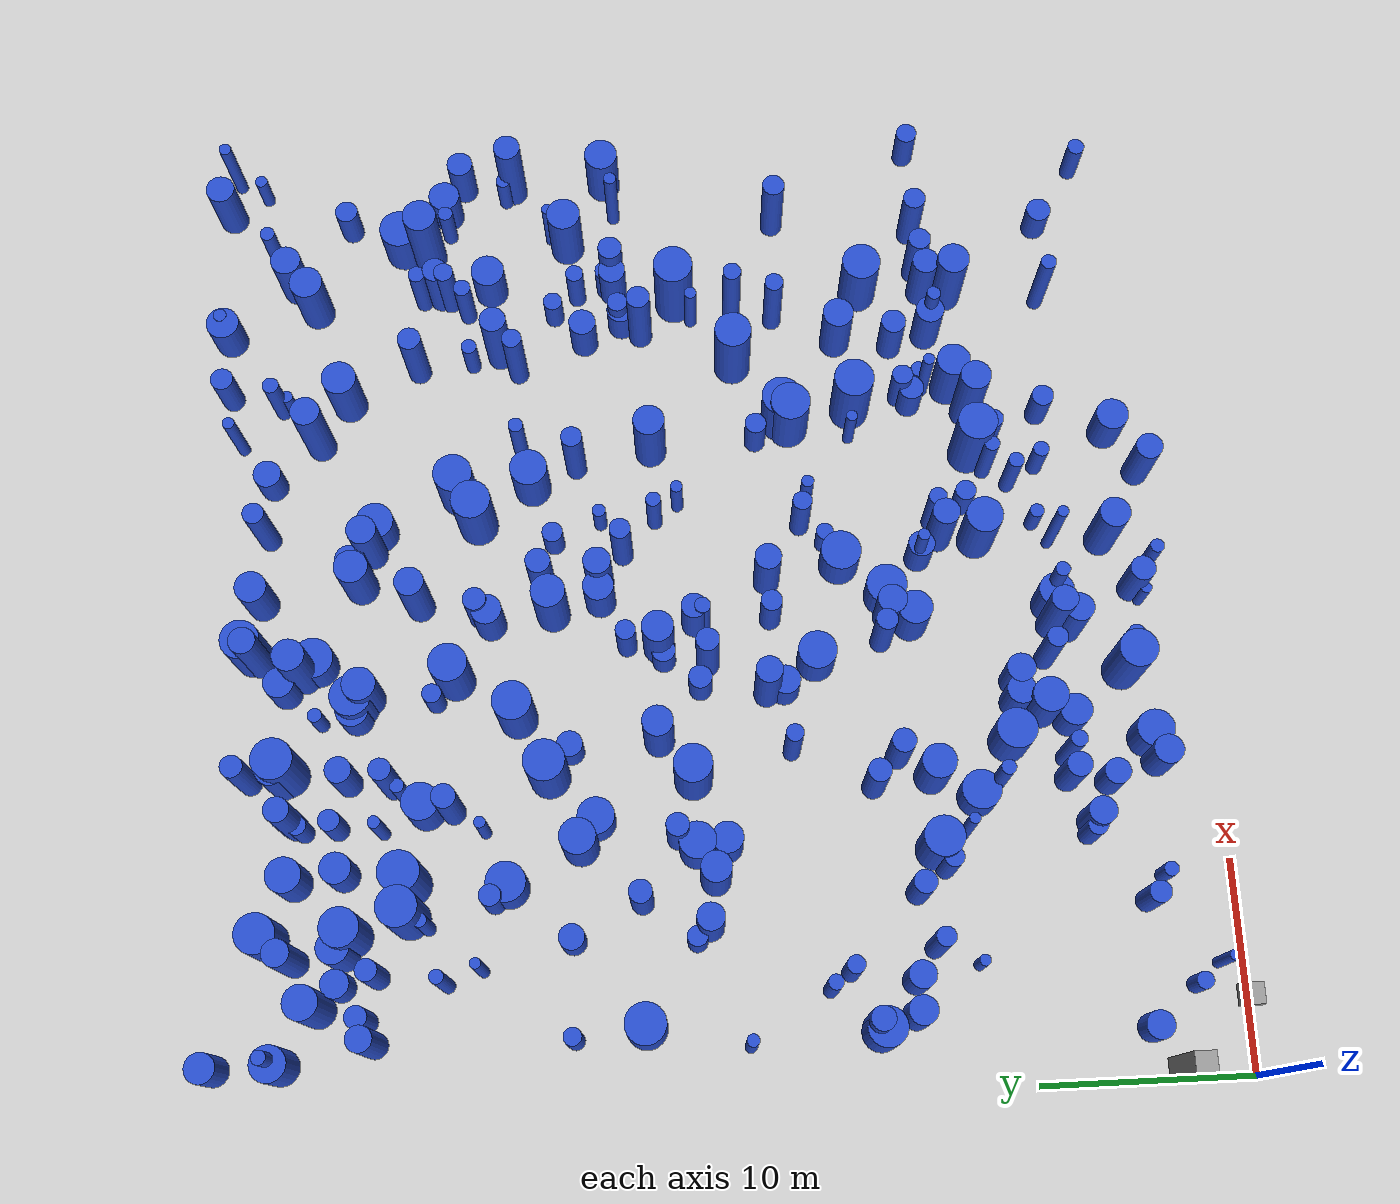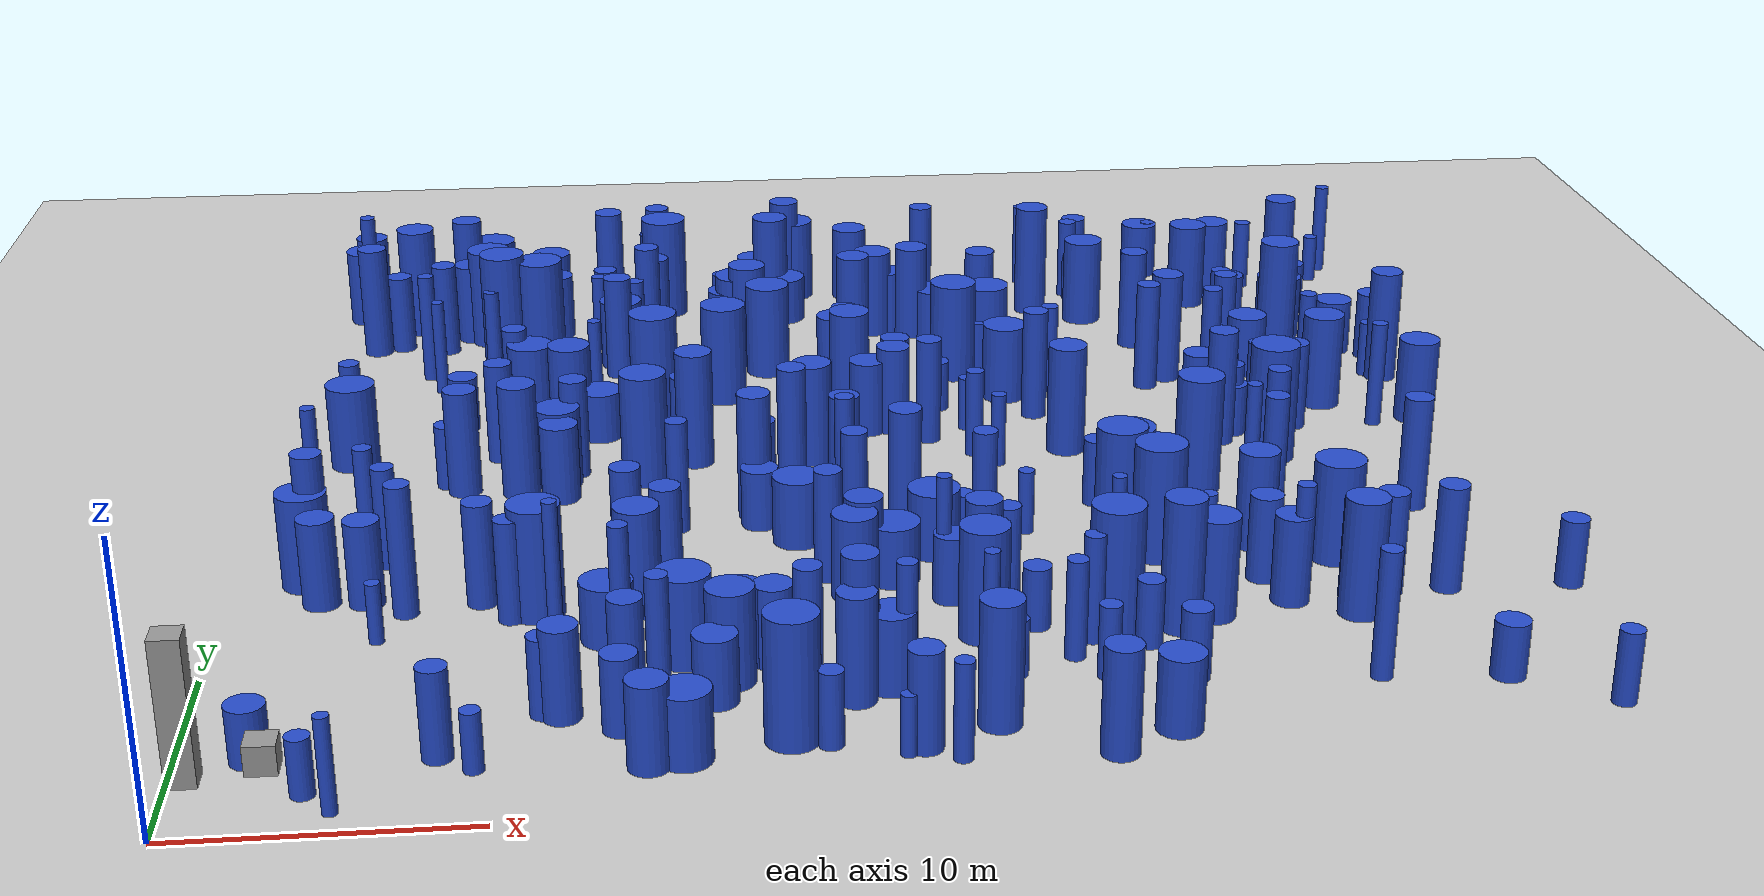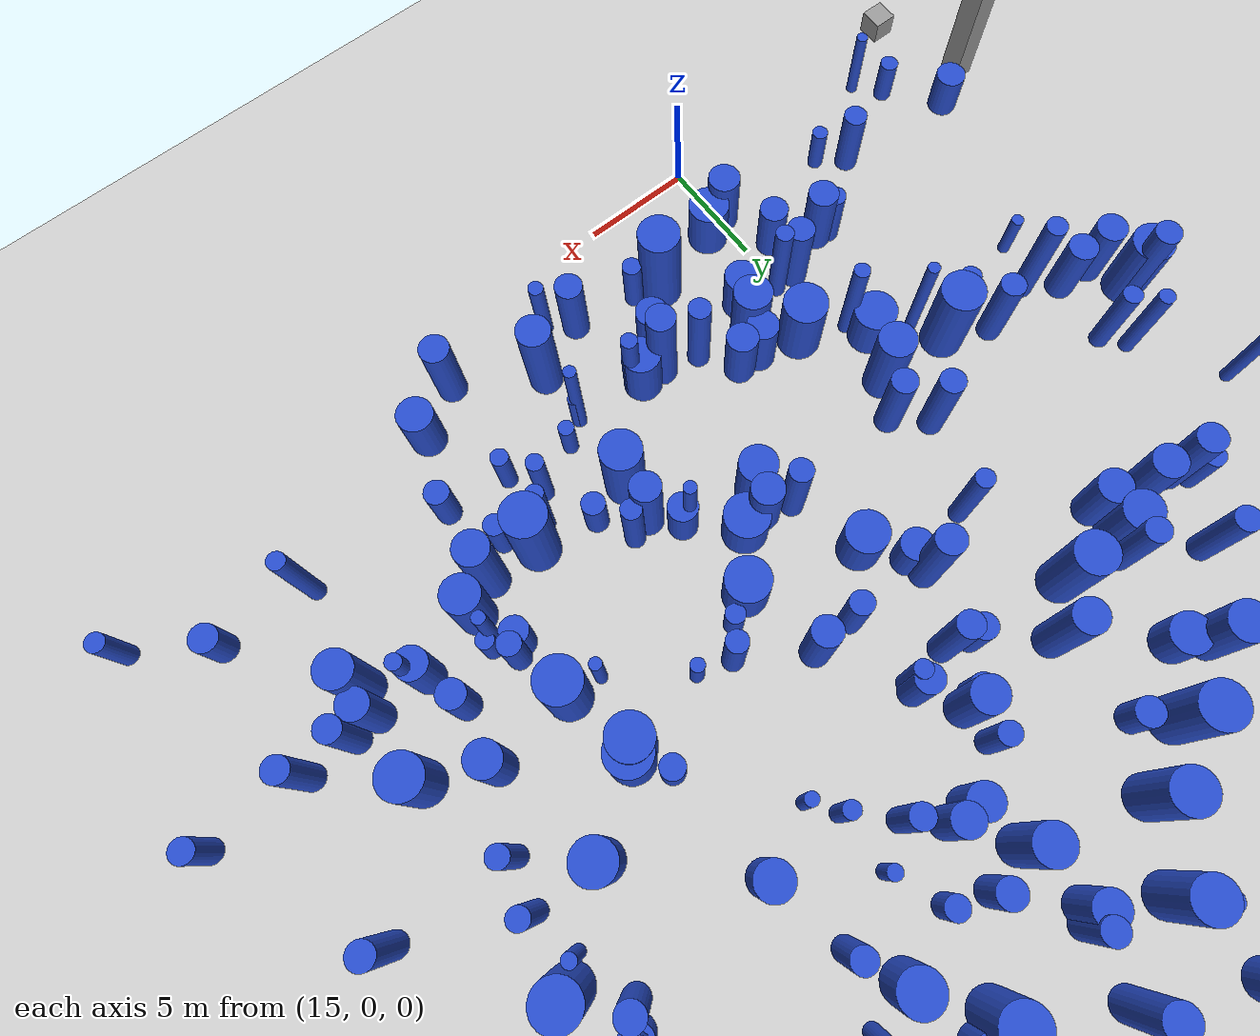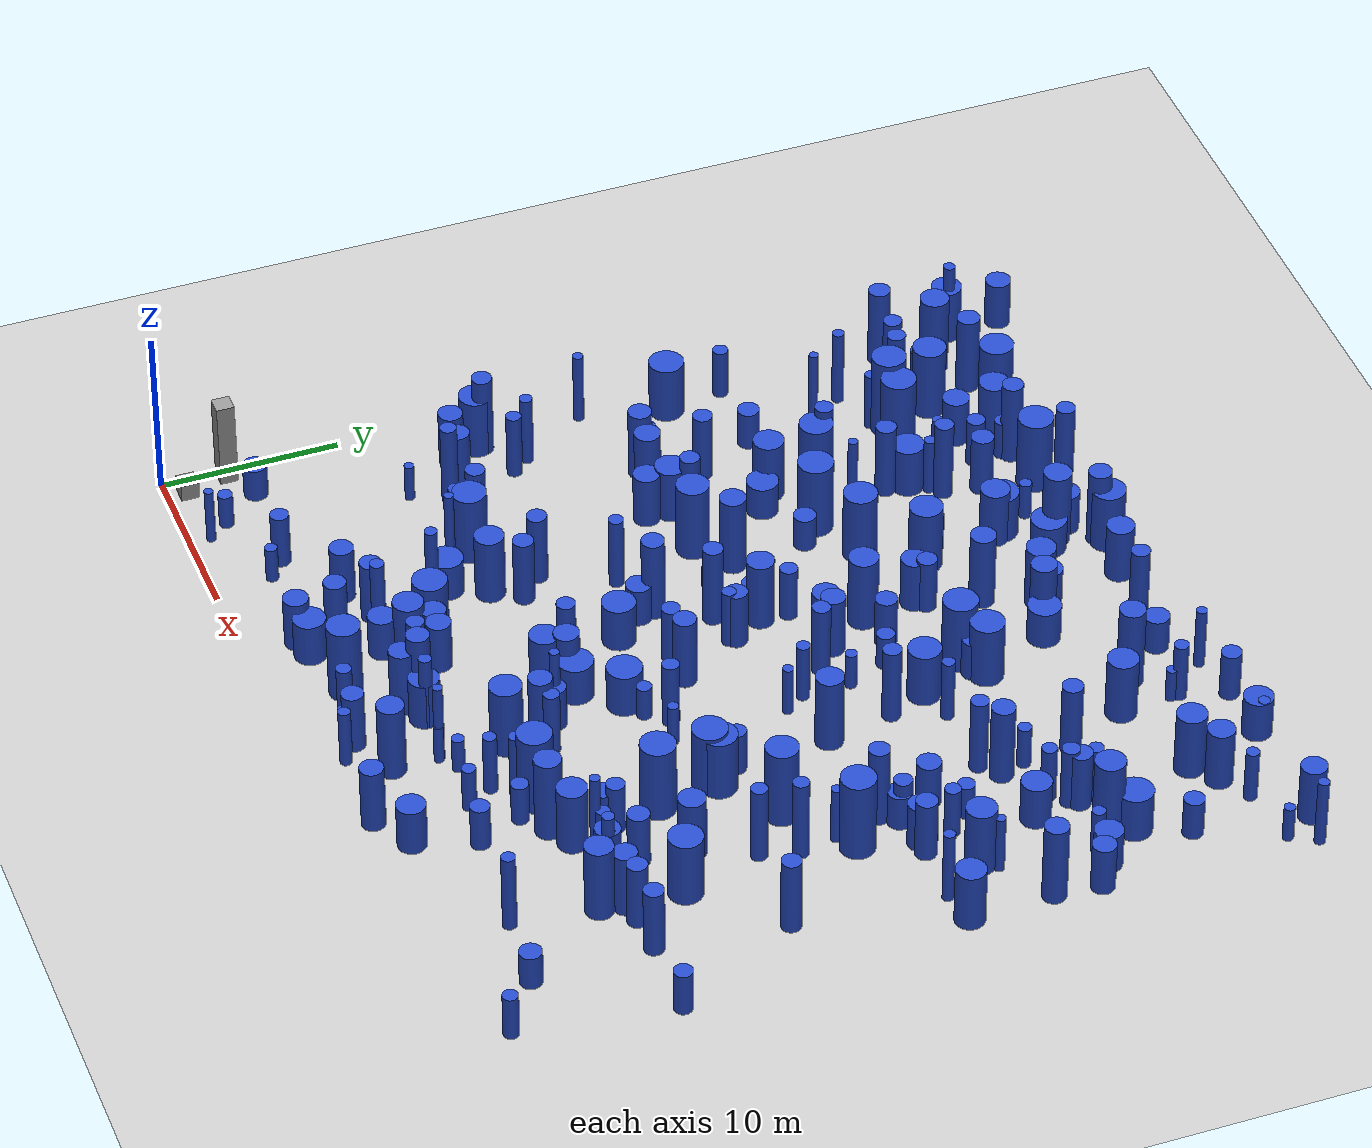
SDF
<sdf version="1.6">
 <world name="default">
  <plugin name="disable_physics" filename="libdisable_physics.so"/>
  <light name="sun" type="directional">
   <pose>0 0 10 0 -0 0</pose>
   <diffuse>0.8 0.8 0.8 1</diffuse>
   <specular>0.1 0.1 0.1 1</specular>
   <attenuation>
    <range>1000</range>
    <constant>0.9</constant>
    <linear>0.01</linear>
    <quadratic>0.001</quadratic>
   </attenuation>
   <direction>-0.5 0.5 -1</direction>
  </light>
  <model name="ground_plane">
   <static>1</static>
   <link name="link">
    <collision name="collision">
     <geometry><plane><normal>0 0 1</normal><size>100 100</size></plane></geometry>
     <surface><friction><ode><mu>100</mu><mu2>50</mu2></ode></friction></surface>
    </collision>
    <visual name="visual">
     <cast_shadows>0</cast_shadows>
     <geometry><plane><normal>0 0 1</normal><size>100 100</size></plane></geometry>
     <material>
      <script><uri>file://media/materials/scripts/gazebo.material</uri><name>Gazebo/Grey</name></script>
     </material>
    </visual>
   </link>
  </model>
  <gravity>0 0 -9.8</gravity>
  <magnetic_field>6e-06 2.3e-05 -4.2e-05</magnetic_field>
  <atmosphere type="adiabatic"/>
  <physics name="default_physics" default="0" type="ode">
   <max_step_size>0.001</max_step_size>
   <real_time_factor>1</real_time_factor>
   <real_time_update_rate>1000</real_time_update_rate>
  </physics>
  <scene><ambient>0.4 0.4 0.4 1</ambient><background>0.7 0.7 0.7 1</background><shadows>1</shadows></scene>
  <spherical_coordinates>
   <surface_model>EARTH_WGS84</surface_model>
   <latitude_deg>0</latitude_deg>
   <longitude_deg>0</longitude_deg>
   <elevation>0</elevation>
   <heading_deg>0</heading_deg>
  </spherical_coordinates>
  <model name="0">
   <static>0</static>
   <link name="link">
    <inertial>
     <mass>2</mass>
     <inertia><ixx>3.82085</ixx><ixy>0</ixy><ixz>0</ixz><iyy>3.82085</iyy><iyz>0</iyz><izz>0.122841</izz></inertia>
    </inertial>
    <collision name="collision">
     <geometry><cylinder><length>4.74937</length><radius>0.350486</radius></cylinder></geometry>
     <surface><contact><collide_without_contact>1</collide_without_contact></contact></surface>
    </collision>
    <visual name="visual">
     <geometry><cylinder><length>4.74937</length><radius>0.350486</radius></cylinder></geometry>
     <material>
      <script><uri>file://media/materials/scripts/gazebo.material</uri><name>Gazebo/Blue</name></script>
     </material>
    </visual>
    <gravity>0</gravity>
   </link>
   <pose>13.9637 10.7957 2.37469 0 -0 0</pose>
  </model>
  <model name="1">
   <static>0</static>
   <link name="link">
    <inertial>
     <mass>2</mass>
     <inertia><ixx>1.29937</ixx><ixy>0</ixy><ixz>0</ixz><iyy>1.29937</iyy><iyz>0</iyz><izz>0.270526</izz></inertia>
    </inertial>
    <collision name="collision">
     <geometry><cylinder><length>2.64284</length><radius>0.520121</radius></cylinder></geometry>
     <surface><contact><collide_without_contact>1</collide_without_contact></contact></surface>
    </collision>
    <visual name="visual">
     <geometry><cylinder><length>2.64284</length><radius>0.520121</radius></cylinder></geometry>
     <material>
      <script><uri>file://media/materials/scripts/gazebo.material</uri><name>Gazebo/Blue</name></script>
     </material>
    </visual>
    <gravity>0</gravity>
   </link>
   <pose>32.0876 21.3109 1.32142 0 -0 0</pose>
  </model>
  <model name="2">
   <static>0</static>
   <link name="link">
    <inertial>
     <mass>2</mass>
     <inertia><ixx>1.22837</ixx><ixy>0</ixy><ixz>0</ixz><iyy>1.22837</iyy><iyz>0</iyz><izz>0.232608</izz></inertia>
    </inertial>
    <collision name="collision">
     <geometry><cylinder><length>2.5831</length><radius>0.482294</radius></cylinder></geometry>
     <surface><contact><collide_without_contact>1</collide_without_contact></contact></surface>
    </collision>
    <visual name="visual">
     <geometry><cylinder><length>2.5831</length><radius>0.482294</radius></cylinder></geometry>
     <material>
      <script><uri>file://media/materials/scripts/gazebo.material</uri><name>Gazebo/Blue</name></script>
     </material>
    </visual>
    <gravity>0</gravity>
   </link>
   <pose>7.27465 25.3161 1.29155 0 -0 0</pose>
  </model>
  <model name="3">
   <static>0</static>
   <link name="link">
    <inertial>
     <mass>2</mass>
     <inertia><ixx>2.57983</ixx><ixy>0</ixy><ixz>0</ixz><iyy>2.57983</iyy><iyz>0</iyz><izz>0.566458</izz></inertia>
    </inertial>
    <collision name="collision">
     <geometry><cylinder><length>3.71209</length><radius>0.752634</radius></cylinder></geometry>
     <surface><contact><collide_without_contact>1</collide_without_contact></contact></surface>
    </collision>
    <visual name="visual">
     <geometry><cylinder><length>3.71209</length><radius>0.752634</radius></cylinder></geometry>
     <material>
      <script><uri>file://media/materials/scripts/gazebo.material</uri><name>Gazebo/Blue</name></script>
     </material>
    </visual>
    <gravity>0</gravity>
   </link>
   <pose>15.6778 44.6487 1.85604 0 -0 0</pose>
  </model>
  <model name="4">
   <static>0</static>
   <link name="link">
    <inertial>
     <mass>2</mass>
     <inertia>
      <ixx>2.76351</ixx>
      <ixy>0</ixy>
      <ixz>0</ixz>
      <iyy>2.76351</iyy>
      <iyz>0</iyz>
      <izz>0.0663908</izz>
     </inertia>
    </inertial>
    <collision name="collision">
     <geometry><cylinder><length>4.04745</length><radius>0.257664</radius></cylinder></geometry>
     <surface><contact><collide_without_contact>1</collide_without_contact></contact></surface>
    </collision>
    <visual name="visual">
     <geometry><cylinder><length>4.04745</length><radius>0.257664</radius></cylinder></geometry>
     <material>
      <script><uri>file://media/materials/scripts/gazebo.material</uri><name>Gazebo/Blue</name></script>
     </material>
    </visual>
    <gravity>0</gravity>
   </link>
   <pose>6.37285 35.2988 2.02373 0 -0 0</pose>
  </model>
  <model name="5">
   <static>0</static>
   <link name="link">
    <inertial>
     <mass>2</mass>
     <inertia><ixx>1.28365</ixx><ixy>0</ixy><ixz>0</ixz><iyy>1.28365</iyy><iyz>0</iyz><izz>0.136114</izz></inertia>
    </inertial>
    <collision name="collision">
     <geometry><cylinder><length>2.70066</length><radius>0.368937</radius></cylinder></geometry>
     <surface><contact><collide_without_contact>1</collide_without_contact></contact></surface>
    </collision>
    <visual name="visual">
     <geometry><cylinder><length>2.70066</length><radius>0.368937</radius></cylinder></geometry>
     <material>
      <script><uri>file://media/materials/scripts/gazebo.material</uri><name>Gazebo/Blue</name></script>
     </material>
    </visual>
    <gravity>0</gravity>
   </link>
   <pose>44.2189 36.454 1.35033 0 -0 0</pose>
  </model>
  <model name="6">
   <static>0</static>
   <link name="link">
    <inertial>
     <mass>2</mass>
     <inertia><ixx>1.67554</ixx><ixy>0</ixy><ixz>0</ixz><iyy>1.67554</iyy><iyz>0</iyz><izz>0.257363</izz></inertia>
    </inertial>
    <collision name="collision">
     <geometry><cylinder><length>3.04649</length><radius>0.50731</radius></cylinder></geometry>
     <surface><contact><collide_without_contact>1</collide_without_contact></contact></surface>
    </collision>
    <visual name="visual">
     <geometry><cylinder><length>3.04649</length><radius>0.50731</radius></cylinder></geometry>
     <material>
      <script><uri>file://media/materials/scripts/gazebo.material</uri><name>Gazebo/Blue</name></script>
     </material>
    </visual>
    <gravity>0</gravity>
   </link>
   <pose>34.1541 13.9376 1.52325 0 -0 0</pose>
  </model>
  <model name="7">
   <static>0</static>
   <link name="link">
    <inertial>
     <mass>2</mass>
     <inertia><ixx>1.62705</ixx><ixy>0</ixy><ixz>0</ixz><iyy>1.62705</iyy><iyz>0</iyz><izz>0.555531</izz></inertia>
    </inertial>
    <collision name="collision">
     <geometry><cylinder><length>2.84529</length><radius>0.745339</radius></cylinder></geometry>
     <surface><contact><collide_without_contact>1</collide_without_contact></contact></surface>
    </collision>
    <visual name="visual">
     <geometry><cylinder><length>2.84529</length><radius>0.745339</radius></cylinder></geometry>
     <material>
      <script><uri>file://media/materials/scripts/gazebo.material</uri><name>Gazebo/Blue</name></script>
     </material>
    </visual>
    <gravity>0</gravity>
   </link>
   <pose>11.1182 41.7888 1.42265 0 -0 0</pose>
  </model>
  <model name="8">
   <static>0</static>
   <link name="link">
    <inertial>
     <mass>2</mass>
     <inertia><ixx>3.2449</ixx><ixy>0</ixy><ixz>0</ixz><iyy>3.2449</iyy><iyz>0</iyz><izz>0.0853454</izz></inertia>
    </inertial>
    <collision name="collision">
     <geometry><cylinder><length>4.3833</length><radius>0.292139</radius></cylinder></geometry>
     <surface><contact><collide_without_contact>1</collide_without_contact></contact></surface>
    </collision>
    <visual name="visual">
     <geometry><cylinder><length>4.3833</length><radius>0.292139</radius></cylinder></geometry>
     <material>
      <script><uri>file://media/materials/scripts/gazebo.material</uri><name>Gazebo/Blue</name></script>
     </material>
    </visual>
    <gravity>0</gravity>
   </link>
   <pose>2.40092 23.0819 2.19165 0 -0 0</pose>
  </model>
  <model name="9">
   <static>0</static>
   <link name="link">
    <inertial>
     <mass>2</mass>
     <inertia><ixx>2.17214</ixx><ixy>0</ixy><ixz>0</ixz><iyy>2.17214</iyy><iyz>0</iyz><izz>0.825516</izz></inertia>
    </inertial>
    <collision name="collision">
     <geometry><cylinder><length>3.24904</length><radius>0.908579</radius></cylinder></geometry>
     <surface><contact><collide_without_contact>1</collide_without_contact></contact></surface>
    </collision>
    <visual name="visual">
     <geometry><cylinder><length>3.24904</length><radius>0.908579</radius></cylinder></geometry>
     <material>
      <script><uri>file://media/materials/scripts/gazebo.material</uri><name>Gazebo/Blue</name></script>
     </material>
    </visual>
    <gravity>0</gravity>
   </link>
   <pose>30.0928 32.4885 1.62452 0 -0 0</pose>
  </model>
  <model name="10">
   <static>0</static>
   <link name="link">
    <inertial>
     <mass>2</mass>
     <inertia><ixx>1.16641</ixx><ixy>0</ixy><ixz>0</ixz><iyy>1.16641</iyy><iyz>0</iyz><izz>0.142317</izz></inertia>
    </inertial>
    <collision name="collision">
     <geometry><cylinder><length>2.56349</length><radius>0.37725</radius></cylinder></geometry>
     <surface><contact><collide_without_contact>1</collide_without_contact></contact></surface>
    </collision>
    <visual name="visual">
     <geometry><cylinder><length>2.56349</length><radius>0.37725</radius></cylinder></geometry>
     <material>
      <script><uri>file://media/materials/scripts/gazebo.material</uri><name>Gazebo/Blue</name></script>
     </material>
    </visual>
    <gravity>0</gravity>
   </link>
   <pose>36.8922 35.3674 1.28175 0 -0 0</pose>
  </model>
  <model name="11">
   <static>0</static>
   <link name="link">
    <inertial>
     <mass>2</mass>
     <inertia><ixx>3.67772</ixx><ixy>0</ixy><ixz>0</ixz><iyy>3.67772</iyy><iyz>0</iyz><izz>0.546704</izz></inertia>
    </inertial>
    <collision name="collision">
     <geometry><cylinder><length>4.51954</length><radius>0.739394</radius></cylinder></geometry>
     <surface><contact><collide_without_contact>1</collide_without_contact></contact></surface>
    </collision>
    <visual name="visual">
     <geometry><cylinder><length>4.51954</length><radius>0.739394</radius></cylinder></geometry>
     <material>
      <script><uri>file://media/materials/scripts/gazebo.material</uri><name>Gazebo/Blue</name></script>
     </material>
    </visual>
    <gravity>0</gravity>
   </link>
   <pose>26.0271 4.56998 2.25977 0 -0 0</pose>
  </model>
  <model name="12">
   <static>0</static>
   <link name="link">
    <inertial>
     <mass>2</mass>
     <inertia><ixx>2.99946</ixx><ixy>0</ixy><ixz>0</ixz><iyy>2.99946</iyy><iyz>0</iyz><izz>0.69692</izz></inertia>
    </inertial>
    <collision name="collision">
     <geometry><cylinder><length>3.98823</length><radius>0.834817</radius></cylinder></geometry>
     <surface><contact><collide_without_contact>1</collide_without_contact></contact></surface>
    </collision>
    <visual name="visual">
     <geometry><cylinder><length>3.98823</length><radius>0.834817</radius></cylinder></geometry>
     <material>
      <script><uri>file://media/materials/scripts/gazebo.material</uri><name>Gazebo/Blue</name></script>
     </material>
    </visual>
    <gravity>0</gravity>
   </link>
   <pose>43.2297 30.4 1.99412 0 -0 0</pose>
  </model>
  <model name="13">
   <static>0</static>
   <link name="link">
    <inertial>
     <mass>2</mass>
     <inertia><ixx>4.00177</ixx><ixy>0</ixy><ixz>0</ixz><iyy>4.00177</iyy><iyz>0</iyz><izz>0.275408</izz></inertia>
    </inertial>
    <collision name="collision">
     <geometry><cylinder><length>4.81501</length><radius>0.524793</radius></cylinder></geometry>
     <surface><contact><collide_without_contact>1</collide_without_contact></contact></surface>
    </collision>
    <visual name="visual">
     <geometry><cylinder><length>4.81501</length><radius>0.524793</radius></cylinder></geometry>
     <material>
      <script><uri>file://media/materials/scripts/gazebo.material</uri><name>Gazebo/Blue</name></script>
     </material>
    </visual>
    <gravity>0</gravity>
   </link>
   <pose>15.2098 39.4486 2.40751 0 -0 0</pose>
  </model>
  <model name="14">
   <static>0</static>
   <link name="link">
    <inertial>
     <mass>2</mass>
     <inertia>
      <ixx>2.88721</ixx>
      <ixy>0</ixy>
      <ixz>0</ixz>
      <iyy>2.88721</iyy>
      <iyz>0</iyz>
      <izz>0.0931527</izz>
     </inertia>
    </inertial>
    <collision name="collision">
     <geometry><cylinder><length>4.12841</length><radius>0.305209</radius></cylinder></geometry>
     <surface><contact><collide_without_contact>1</collide_without_contact></contact></surface>
    </collision>
    <visual name="visual">
     <geometry><cylinder><length>4.12841</length><radius>0.305209</radius></cylinder></geometry>
     <material>
      <script><uri>file://media/materials/scripts/gazebo.material</uri><name>Gazebo/Blue</name></script>
     </material>
    </visual>
    <gravity>0</gravity>
   </link>
   <pose>47.5968 47.3639 2.06421 0 -0 0</pose>
  </model>
  <model name="15">
   <static>0</static>
   <link name="link">
    <inertial>
     <mass>2</mass>
     <inertia><ixx>3.33766</ixx><ixy>0</ixy><ixz>0</ixz><iyy>3.33766</iyy><iyz>0</iyz><izz>0.789182</izz></inertia>
    </inertial>
    <collision name="collision">
     <geometry><cylinder><length>4.20219</length><radius>0.888359</radius></cylinder></geometry>
     <surface><contact><collide_without_contact>1</collide_without_contact></contact></surface>
    </collision>
    <visual name="visual">
     <geometry><cylinder><length>4.20219</length><radius>0.888359</radius></cylinder></geometry>
     <material>
      <script><uri>file://media/materials/scripts/gazebo.material</uri><name>Gazebo/Blue</name></script>
     </material>
    </visual>
    <gravity>0</gravity>
   </link>
   <pose>26.311 10.715 2.1011 0 -0 0</pose>
  </model>
  <model name="16">
   <static>0</static>
   <link name="link">
    <inertial>
     <mass>2</mass>
     <inertia><ixx>3.98692</ixx><ixy>0</ixy><ixz>0</ixz><iyy>3.98692</iyy><iyz>0</iyz><izz>0.541429</izz></inertia>
    </inertial>
    <collision name="collision">
     <geometry><cylinder><length>4.72199</length><radius>0.735818</radius></cylinder></geometry>
     <surface><contact><collide_without_contact>1</collide_without_contact></contact></surface>
    </collision>
    <visual name="visual">
     <geometry><cylinder><length>4.72199</length><radius>0.735818</radius></cylinder></geometry>
     <material>
      <script><uri>file://media/materials/scripts/gazebo.material</uri><name>Gazebo/Blue</name></script>
     </material>
    </visual>
    <gravity>0</gravity>
   </link>
   <pose>16.8892 26.7119 2.361 0 -0 0</pose>
  </model>
  <model name="17">
   <static>0</static>
   <link name="link">
    <inertial>
     <mass>2</mass>
     <inertia><ixx>2.21319</ixx><ixy>0</ixy><ixz>0</ixz><iyy>2.21319</iyy><iyz>0</iyz><izz>0.160005</izz></inertia>
    </inertial>
    <collision name="collision">
     <geometry><cylinder><length>3.57759</length><radius>0.400007</radius></cylinder></geometry>
     <surface><contact><collide_without_contact>1</collide_without_contact></contact></surface>
    </collision>
    <visual name="visual">
     <geometry><cylinder><length>3.57759</length><radius>0.400007</radius></cylinder></geometry>
     <material>
      <script><uri>file://media/materials/scripts/gazebo.material</uri><name>Gazebo/Blue</name></script>
     </material>
    </visual>
    <gravity>0</gravity>
   </link>
   <pose>34.8299 44.982 1.78879 0 -0 0</pose>
  </model>
  <model name="18">
   <static>0</static>
   <link name="link">
    <inertial>
     <mass>2</mass>
     <inertia><ixx>1.88839</ixx><ixy>0</ixy><ixz>0</ixz><iyy>1.88839</iyy><iyz>0</iyz><izz>0.554769</izz></inertia>
    </inertial>
    <collision name="collision">
     <geometry><cylinder><length>3.10903</length><radius>0.744828</radius></cylinder></geometry>
     <surface><contact><collide_without_contact>1</collide_without_contact></contact></surface>
    </collision>
    <visual name="visual">
     <geometry><cylinder><length>3.10903</length><radius>0.744828</radius></cylinder></geometry>
     <material>
      <script><uri>file://media/materials/scripts/gazebo.material</uri><name>Gazebo/Blue</name></script>
     </material>
    </visual>
    <gravity>0</gravity>
   </link>
   <pose>11.6379 23.7222 1.55451 0 -0 0</pose>
  </model>
  <model name="19">
   <static>0</static>
   <link name="link">
    <inertial>
     <mass>2</mass>
     <inertia><ixx>1.64625</ixx><ixy>0</ixy><ixz>0</ixz><iyy>1.64625</iyy><iyz>0</iyz><izz>0.417403</izz></inertia>
    </inertial>
    <collision name="collision">
     <geometry><cylinder><length>2.93689</length><radius>0.646067</radius></cylinder></geometry>
     <surface><contact><collide_without_contact>1</collide_without_contact></contact></surface>
    </collision>
    <visual name="visual">
     <geometry><cylinder><length>2.93689</length><radius>0.646067</radius></cylinder></geometry>
     <material>
      <script><uri>file://media/materials/scripts/gazebo.material</uri><name>Gazebo/Blue</name></script>
     </material>
    </visual>
    <gravity>0</gravity>
   </link>
   <pose>46.8519 35.6651 1.46844 0 -0 0</pose>
  </model>
  <model name="20">
   <static>0</static>
   <link name="link">
    <inertial>
     <mass>2</mass>
     <inertia><ixx>1.55555</ixx><ixy>0</ixy><ixz>0</ixz><iyy>1.55555</iyy><iyz>0</iyz><izz>0.262073</izz></inertia>
    </inertial>
    <collision name="collision">
     <geometry><cylinder><length>2.92354</length><radius>0.51193</radius></cylinder></geometry>
     <surface><contact><collide_without_contact>1</collide_without_contact></contact></surface>
    </collision>
    <visual name="visual">
     <geometry><cylinder><length>2.92354</length><radius>0.51193</radius></cylinder></geometry>
     <material>
      <script><uri>file://media/materials/scripts/gazebo.material</uri><name>Gazebo/Blue</name></script>
     </material>
    </visual>
    <gravity>0</gravity>
   </link>
   <pose>13.3245 42.0815 1.46177 0 -0 0</pose>
  </model>
  <model name="21">
   <static>0</static>
   <link name="link">
    <inertial>
     <mass>2</mass>
     <inertia><ixx>3.15803</ixx><ixy>0</ixy><ixz>0</ixz><iyy>3.15803</iyy><iyz>0</iyz><izz>0.583815</izz></inertia>
    </inertial>
    <collision name="collision">
     <geometry><cylinder><length>4.14689</length><radius>0.764078</radius></cylinder></geometry>
     <surface><contact><collide_without_contact>1</collide_without_contact></contact></surface>
    </collision>
    <visual name="visual">
     <geometry><cylinder><length>4.14689</length><radius>0.764078</radius></cylinder></geometry>
     <material>
      <script><uri>file://media/materials/scripts/gazebo.material</uri><name>Gazebo/Blue</name></script>
     </material>
    </visual>
    <gravity>0</gravity>
   </link>
   <pose>21.5547 26.5343 2.07345 0 -0 0</pose>
  </model>
  <model name="22">
   <static>0</static>
   <link name="link">
    <inertial>
     <mass>2</mass>
     <inertia><ixx>3.25357</ixx><ixy>0</ixy><ixz>0</ixz><iyy>3.25357</iyy><iyz>0</iyz><izz>0.409144</izz></inertia>
    </inertial>
    <collision name="collision">
     <geometry><cylinder><length>4.27715</length><radius>0.639643</radius></cylinder></geometry>
     <surface><contact><collide_without_contact>1</collide_without_contact></contact></surface>
    </collision>
    <visual name="visual">
     <geometry><cylinder><length>4.27715</length><radius>0.639643</radius></cylinder></geometry>
     <material>
      <script><uri>file://media/materials/scripts/gazebo.material</uri><name>Gazebo/Blue</name></script>
     </material>
    </visual>
    <gravity>0</gravity>
   </link>
   <pose>24.6833 21.1514 2.13857 0 -0 0</pose>
  </model>
  <model name="23">
   <static>0</static>
   <link name="link">
    <inertial>
     <mass>2</mass>
     <inertia><ixx>1.86215</ixx><ixy>0</ixy><ixz>0</ixz><iyy>1.86215</iyy><iyz>0</iyz><izz>0.4961</izz></inertia>
    </inertial>
    <collision name="collision">
     <geometry><cylinder><length>3.11201</length><radius>0.704343</radius></cylinder></geometry>
     <surface><contact><collide_without_contact>1</collide_without_contact></contact></surface>
    </collision>
    <visual name="visual">
     <geometry><cylinder><length>3.11201</length><radius>0.704343</radius></cylinder></geometry>
     <material>
      <script><uri>file://media/materials/scripts/gazebo.material</uri><name>Gazebo/Blue</name></script>
     </material>
    </visual>
    <gravity>0</gravity>
   </link>
   <pose>14.7881 2.99423 1.55601 0 -0 0</pose>
  </model>
  <model name="24">
   <static>0</static>
   <link name="link">
    <inertial>
     <mass>2</mass>
     <inertia><ixx>1.49406</ixx><ixy>0</ixy><ixz>0</ixz><iyy>1.49406</iyy><iyz>0</iyz><izz>0.447724</izz></inertia>
    </inertial>
    <collision name="collision">
     <geometry><cylinder><length>2.76065</length><radius>0.669122</radius></cylinder></geometry>
     <surface><contact><collide_without_contact>1</collide_without_contact></contact></surface>
    </collision>
    <visual name="visual">
     <geometry><cylinder><length>2.76065</length><radius>0.669122</radius></cylinder></geometry>
     <material>
      <script><uri>file://media/materials/scripts/gazebo.material</uri><name>Gazebo/Blue</name></script>
     </material>
    </visual>
    <gravity>0</gravity>
   </link>
   <pose>37.853 29.6773 1.38032 0 -0 0</pose>
  </model>
  <model name="25">
   <static>0</static>
   <link name="link">
    <inertial>
     <mass>2</mass>
     <inertia><ixx>3.26068</ixx><ixy>0</ixy><ixz>0</ixz><iyy>3.26068</iyy><iyz>0</iyz><izz>0.425175</izz></inertia>
    </inertial>
    <collision name="collision">
     <geometry><cylinder><length>4.27651</length><radius>0.652054</radius></cylinder></geometry>
     <surface><contact><collide_without_contact>1</collide_without_contact></contact></surface>
    </collision>
    <visual name="visual">
     <geometry><cylinder><length>4.27651</length><radius>0.652054</radius></cylinder></geometry>
     <material>
      <script><uri>file://media/materials/scripts/gazebo.material</uri><name>Gazebo/Blue</name></script>
     </material>
    </visual>
    <gravity>0</gravity>
   </link>
   <pose>7.91158 24.6829 2.13826 0 -0 0</pose>
  </model>
  <model name="26">
   <static>0</static>
   <link name="link">
    <inertial>
     <mass>2</mass>
     <inertia><ixx>1.59022</ixx><ixy>0</ixy><ixz>0</ixz><iyy>1.59022</iyy><iyz>0</iyz><izz>0.948667</izz></inertia>
    </inertial>
    <collision name="collision">
     <geometry><cylinder><length>2.58753</length><radius>0.973996</radius></cylinder></geometry>
     <surface><contact><collide_without_contact>1</collide_without_contact></contact></surface>
    </collision>
    <visual name="visual">
     <geometry><cylinder><length>2.58753</length><radius>0.973996</radius></cylinder></geometry>
     <material>
      <script><uri>file://media/materials/scripts/gazebo.material</uri><name>Gazebo/Blue</name></script>
     </material>
    </visual>
    <gravity>0</gravity>
   </link>
   <pose>25.3744 17.5495 1.29377 0 -0 0</pose>
  </model>
  <model name="27">
   <static>0</static>
   <link name="link">
    <inertial>
     <mass>2</mass>
     <inertia>
      <ixx>2.06442</ixx>
      <ixy>0</ixy>
      <ixz>0</ixz>
      <iyy>2.06442</iyy>
      <iyz>0</iyz>
      <izz>0.0914529</izz>
     </inertia>
    </inertial>
    <collision name="collision">
     <geometry><cylinder><length>3.48025</length><radius>0.302412</radius></cylinder></geometry>
     <surface><contact><collide_without_contact>1</collide_without_contact></contact></surface>
    </collision>
    <visual name="visual">
     <geometry><cylinder><length>3.48025</length><radius>0.302412</radius></cylinder></geometry>
     <material>
      <script><uri>file://media/materials/scripts/gazebo.material</uri><name>Gazebo/Blue</name></script>
     </material>
    </visual>
    <gravity>0</gravity>
   </link>
   <pose>38.8581 24.2263 1.74013 0 -0 0</pose>
  </model>
  <model name="28">
   <static>0</static>
   <link name="link">
    <inertial>
     <mass>2</mass>
     <inertia><ixx>1.90148</ixx><ixy>0</ixy><ixz>0</ixz><iyy>1.90148</iyy><iyz>0</iyz><izz>0.266141</izz></inertia>
    </inertial>
    <collision name="collision">
     <geometry><cylinder><length>3.25737</length><radius>0.515889</radius></cylinder></geometry>
     <surface><contact><collide_without_contact>1</collide_without_contact></contact></surface>
    </collision>
    <visual name="visual">
     <geometry><cylinder><length>3.25737</length><radius>0.515889</radius></cylinder></geometry>
     <material>
      <script><uri>file://media/materials/scripts/gazebo.material</uri><name>Gazebo/Blue</name></script>
     </material>
    </visual>
    <gravity>0</gravity>
   </link>
   <pose>8.19868 4.18258 1.62868 0 -0 0</pose>
  </model>
  <model name="29">
   <static>0</static>
   <link name="link">
    <inertial>
     <mass>2</mass>
     <inertia>
      <ixx>0.983996</ixx>
      <ixy>0</ixy>
      <ixz>0</ixz>
      <iyy>0.983996</iyy>
      <iyz>0</iyz>
      <izz>0.470048</izz>
     </inertia>
    </inertial>
    <collision name="collision">
     <geometry><cylinder><length>2.11987</length><radius>0.685601</radius></cylinder></geometry>
     <surface><contact><collide_without_contact>1</collide_without_contact></contact></surface>
    </collision>
    <visual name="visual">
     <geometry><cylinder><length>2.11987</length><radius>0.685601</radius></cylinder></geometry>
     <material>
      <script><uri>file://media/materials/scripts/gazebo.material</uri><name>Gazebo/Blue</name></script>
     </material>
    </visual>
    <gravity>0</gravity>
   </link>
   <pose>38.7542 27.7533 1.05993 0 -0 0</pose>
  </model>
  <model name="30">
   <static>0</static>
   <link name="link">
    <inertial>
     <mass>2</mass>
     <inertia><ixx>1.36472</ixx><ixy>0</ixy><ixz>0</ixz><iyy>1.36472</iyy><iyz>0</iyz><izz>0.964605</izz></inertia>
    </inertial>
    <collision name="collision">
     <geometry><cylinder><length>2.30098</length><radius>0.982143</radius></cylinder></geometry>
     <surface><contact><collide_without_contact>1</collide_without_contact></contact></surface>
    </collision>
    <visual name="visual">
     <geometry><cylinder><length>2.30098</length><radius>0.982143</radius></cylinder></geometry>
     <material>
      <script><uri>file://media/materials/scripts/gazebo.material</uri><name>Gazebo/Blue</name></script>
     </material>
    </visual>
    <gravity>0</gravity>
   </link>
   <pose>23.6658 15.4375 1.15049 0 -0 0</pose>
  </model>
  <model name="31">
   <static>0</static>
   <link name="link">
    <inertial>
     <mass>2</mass>
     <inertia><ixx>2.45644</ixx><ixy>0</ixy><ixz>0</ixz><iyy>2.45644</iyy><iyz>0</iyz><izz>0.235516</izz></inertia>
    </inertial>
    <collision name="collision">
     <geometry><cylinder><length>3.74595</length><radius>0.4853</radius></cylinder></geometry>
     <surface><contact><collide_without_contact>1</collide_without_contact></contact></surface>
    </collision>
    <visual name="visual">
     <geometry><cylinder><length>3.74595</length><radius>0.4853</radius></cylinder></geometry>
     <material>
      <script><uri>file://media/materials/scripts/gazebo.material</uri><name>Gazebo/Blue</name></script>
     </material>
    </visual>
    <gravity>0</gravity>
   </link>
   <pose>40.4344 36.4539 1.87297 0 -0 0</pose>
  </model>
  <model name="32">
   <static>0</static>
   <link name="link">
    <inertial>
     <mass>2</mass>
     <inertia><ixx>3.68543</ixx><ixy>0</ixy><ixz>0</ixz><iyy>3.68543</iyy><iyz>0</iyz><izz>0.263178</izz></inertia>
    </inertial>
    <collision name="collision">
     <geometry><cylinder><length>4.61769</length><radius>0.513009</radius></cylinder></geometry>
     <surface><contact><collide_without_contact>1</collide_without_contact></contact></surface>
    </collision>
    <visual name="visual">
     <geometry><cylinder><length>4.61769</length><radius>0.513009</radius></cylinder></geometry>
     <material>
      <script><uri>file://media/materials/scripts/gazebo.material</uri><name>Gazebo/Blue</name></script>
     </material>
    </visual>
    <gravity>0</gravity>
   </link>
   <pose>31.0444 30.2874 2.30884 0 -0 0</pose>
  </model>
  <model name="33">
   <static>0</static>
   <link name="link">
    <inertial>
     <mass>2</mass>
     <inertia><ixx>3.67446</ixx><ixy>0</ixy><ixz>0</ixz><iyy>3.67446</iyy><iyz>0</iyz><izz>0.109586</izz></inertia>
    </inertial>
    <collision name="collision">
     <geometry><cylinder><length>4.66025</length><radius>0.331037</radius></cylinder></geometry>
     <surface><contact><collide_without_contact>1</collide_without_contact></contact></surface>
    </collision>
    <visual name="visual">
     <geometry><cylinder><length>4.66025</length><radius>0.331037</radius></cylinder></geometry>
     <material>
      <script><uri>file://media/materials/scripts/gazebo.material</uri><name>Gazebo/Blue</name></script>
     </material>
    </visual>
    <gravity>0</gravity>
   </link>
   <pose>5.79937 36.9559 2.33013 0 -0 0</pose>
  </model>
  <model name="34">
   <static>0</static>
   <link name="link">
    <inertial>
     <mass>2</mass>
     <inertia><ixx>0.87381</ixx><ixy>0</ixy><ixz>0</ixz><iyy>0.87381</iyy><iyz>0</iyz><izz>0.104626</izz></inertia>
    </inertial>
    <collision name="collision">
     <geometry><cylinder><length>2.22013</length><radius>0.323459</radius></cylinder></geometry>
     <surface><contact><collide_without_contact>1</collide_without_contact></contact></surface>
    </collision>
    <visual name="visual">
     <geometry><cylinder><length>2.22013</length><radius>0.323459</radius></cylinder></geometry>
     <material>
      <script><uri>file://media/materials/scripts/gazebo.material</uri><name>Gazebo/Blue</name></script>
     </material>
    </visual>
    <gravity>0</gravity>
   </link>
   <pose>28.0725 29.1738 1.11007 0 -0 0</pose>
  </model>
  <model name="35">
   <static>0</static>
   <link name="link">
    <inertial>
     <mass>2</mass>
     <inertia>
      <ixx>1.09122</ixx>
      <ixy>0</ixy>
      <ixz>0</ixz>
      <iyy>1.09122</iyy>
      <iyz>0</iyz>
      <izz>0.0932913</izz>
     </inertia>
    </inertial>
    <collision name="collision">
     <geometry><cylinder><length>2.50348</length><radius>0.305436</radius></cylinder></geometry>
     <surface><contact><collide_without_contact>1</collide_without_contact></contact></surface>
    </collision>
    <visual name="visual">
     <geometry><cylinder><length>2.50348</length><radius>0.305436</radius></cylinder></geometry>
     <material>
      <script><uri>file://media/materials/scripts/gazebo.material</uri><name>Gazebo/Blue</name></script>
     </material>
    </visual>
    <gravity>0</gravity>
   </link>
   <pose>28.9997 18.9307 1.25174 0 -0 0</pose>
  </model>
  <model name="36">
   <static>0</static>
   <link name="link">
    <inertial>
     <mass>2</mass>
     <inertia><ixx>1.95658</ixx><ixy>0</ixy><ixz>0</ixz><iyy>1.95658</iyy><iyz>0</iyz><izz>0.315427</izz></inertia>
    </inertial>
    <collision name="collision">
     <geometry><cylinder><length>3.2853</length><radius>0.561629</radius></cylinder></geometry>
     <surface><contact><collide_without_contact>1</collide_without_contact></contact></surface>
    </collision>
    <visual name="visual">
     <geometry><cylinder><length>3.2853</length><radius>0.561629</radius></cylinder></geometry>
     <material>
      <script><uri>file://media/materials/scripts/gazebo.material</uri><name>Gazebo/Blue</name></script>
     </material>
    </visual>
    <gravity>0</gravity>
   </link>
   <pose>23.5459 35.1984 1.64265 0 -0 0</pose>
  </model>
  <model name="37">
   <static>0</static>
   <link name="link">
    <inertial>
     <mass>2</mass>
     <inertia><ixx>4.25456</ixx><ixy>0</ixy><ixz>0</ixz><iyy>4.25456</iyy><iyz>0</iyz><izz>0.212678</izz></inertia>
    </inertial>
    <collision name="collision">
     <geometry><cylinder><length>4.98892</length><radius>0.46117</radius></cylinder></geometry>
     <surface><contact><collide_without_contact>1</collide_without_contact></contact></surface>
    </collision>
    <visual name="visual">
     <geometry><cylinder><length>4.98892</length><radius>0.46117</radius></cylinder></geometry>
     <material>
      <script><uri>file://media/materials/scripts/gazebo.material</uri><name>Gazebo/Blue</name></script>
     </material>
    </visual>
    <gravity>0</gravity>
   </link>
   <pose>6.44506 14.3001 2.49446 0 -0 0</pose>
  </model>
  <model name="38">
   <static>0</static>
   <link name="link">
    <inertial>
     <mass>2</mass>
     <inertia><ixx>1.50603</ixx><ixy>0</ixy><ixz>0</ixz><iyy>1.50603</iyy><iyz>0</iyz><izz>0.44841</izz></inertia>
    </inertial>
    <collision name="collision">
     <geometry><cylinder><length>2.77325</length><radius>0.669635</radius></cylinder></geometry>
     <surface><contact><collide_without_contact>1</collide_without_contact></contact></surface>
    </collision>
    <visual name="visual">
     <geometry><cylinder><length>2.77325</length><radius>0.669635</radius></cylinder></geometry>
     <material>
      <script><uri>file://media/materials/scripts/gazebo.material</uri><name>Gazebo/Blue</name></script>
     </material>
    </visual>
    <gravity>0</gravity>
   </link>
   <pose>40.6277 28.1109 1.38663 0 -0 0</pose>
  </model>
  <model name="39">
   <static>0</static>
   <link name="link">
    <inertial>
     <mass>2</mass>
     <inertia><ixx>3.67581</ixx><ixy>0</ixy><ixz>0</ixz><iyy>3.67581</iyy><iyz>0</iyz><izz>0.237626</izz></inertia>
    </inertial>
    <collision name="collision">
     <geometry><cylinder><length>4.61974</length><radius>0.487469</radius></cylinder></geometry>
     <surface><contact><collide_without_contact>1</collide_without_contact></contact></surface>
    </collision>
    <visual name="visual">
     <geometry><cylinder><length>4.61974</length><radius>0.487469</radius></cylinder></geometry>
     <material>
      <script><uri>file://media/materials/scripts/gazebo.material</uri><name>Gazebo/Blue</name></script>
     </material>
    </visual>
    <gravity>0</gravity>
   </link>
   <pose>36.3072 33.0621 2.30987 0 -0 0</pose>
  </model>
  <model name="40">
   <static>0</static>
   <link name="link">
    <inertial>
     <mass>2</mass>
     <inertia><ixx>2.77857</ixx><ixy>0</ixy><ixz>0</ixz><iyy>2.77857</iyy><iyz>0</iyz><izz>0.218702</izz></inertia>
    </inertial>
    <collision name="collision">
     <geometry><cylinder><length>4.00191</length><radius>0.467656</radius></cylinder></geometry>
     <surface><contact><collide_without_contact>1</collide_without_contact></contact></surface>
    </collision>
    <visual name="visual">
     <geometry><cylinder><length>4.00191</length><radius>0.467656</radius></cylinder></geometry>
     <material>
      <script><uri>file://media/materials/scripts/gazebo.material</uri><name>Gazebo/Blue</name></script>
     </material>
    </visual>
    <gravity>0</gravity>
   </link>
   <pose>27.4866 19.3515 2.00096 0 -0 0</pose>
  </model>
  <model name="41">
   <static>0</static>
   <link name="link">
    <inertial>
     <mass>2</mass>
     <inertia><ixx>1.76334</ixx><ixy>0</ixy><ixz>0</ixz><iyy>1.76334</iyy><iyz>0</iyz><izz>0.124496</izz></inertia>
    </inertial>
    <collision name="collision">
     <geometry><cylinder><length>3.19477</length><radius>0.352839</radius></cylinder></geometry>
     <surface><contact><collide_without_contact>1</collide_without_contact></contact></surface>
    </collision>
    <visual name="visual">
     <geometry><cylinder><length>3.19477</length><radius>0.352839</radius></cylinder></geometry>
     <material>
      <script><uri>file://media/materials/scripts/gazebo.material</uri><name>Gazebo/Blue</name></script>
     </material>
    </visual>
    <gravity>0</gravity>
   </link>
   <pose>23.6952 31.2859 1.59739 0 -0 0</pose>
  </model>
  <model name="42">
   <static>0</static>
   <link name="link">
    <inertial>
     <mass>2</mass>
     <inertia><ixx>1.3081</ixx><ixy>0</ixy><ixz>0</ixz><iyy>1.3081</iyy><iyz>0</iyz><izz>0.176853</izz></inertia>
    </inertial>
    <collision name="collision">
     <geometry><cylinder><length>2.70519</length><radius>0.420539</radius></cylinder></geometry>
     <surface><contact><collide_without_contact>1</collide_without_contact></contact></surface>
    </collision>
    <visual name="visual">
     <geometry><cylinder><length>2.70519</length><radius>0.420539</radius></cylinder></geometry>
     <material>
      <script><uri>file://media/materials/scripts/gazebo.material</uri><name>Gazebo/Blue</name></script>
     </material>
    </visual>
    <gravity>0</gravity>
   </link>
   <pose>20.533 3.76774 1.3526 0 -0 0</pose>
  </model>
  <model name="43">
   <static>0</static>
   <link name="link">
    <inertial>
     <mass>2</mass>
     <inertia><ixx>1.55938</ixx><ixy>0</ixy><ixz>0</ixz><iyy>1.55938</iyy><iyz>0</iyz><izz>0.307875</izz></inertia>
    </inertial>
    <collision name="collision">
     <geometry><cylinder><length>2.9039</length><radius>0.554865</radius></cylinder></geometry>
     <surface><contact><collide_without_contact>1</collide_without_contact></contact></surface>
    </collision>
    <visual name="visual">
     <geometry><cylinder><length>2.9039</length><radius>0.554865</radius></cylinder></geometry>
     <material>
      <script><uri>file://media/materials/scripts/gazebo.material</uri><name>Gazebo/Blue</name></script>
     </material>
    </visual>
    <gravity>0</gravity>
   </link>
   <pose>35.5678 47.5327 1.45195 0 -0 0</pose>
  </model>
  <model name="44">
   <static>0</static>
   <link name="link">
    <inertial>
     <mass>2</mass>
     <inertia><ixx>3.63122</ixx><ixy>0</ixy><ixz>0</ixz><iyy>3.63122</iyy><iyz>0</iyz><izz>0.614122</izz></inertia>
    </inertial>
    <collision name="collision">
     <geometry><cylinder><length>4.46598</length><radius>0.783659</radius></cylinder></geometry>
     <surface><contact><collide_without_contact>1</collide_without_contact></contact></surface>
    </collision>
    <visual name="visual">
     <geometry><cylinder><length>4.46598</length><radius>0.783659</radius></cylinder></geometry>
     <material>
      <script><uri>file://media/materials/scripts/gazebo.material</uri><name>Gazebo/Blue</name></script>
     </material>
    </visual>
    <gravity>0</gravity>
   </link>
   <pose>39.6417 11.1136 2.23299 0 -0 0</pose>
  </model>
  <model name="45">
   <static>0</static>
   <link name="link">
    <inertial>
     <mass>2</mass>
     <inertia><ixx>4.31175</ixx><ixy>0</ixy><ixz>0</ixz><iyy>4.31175</iyy><iyz>0</iyz><izz>0.358965</izz></inertia>
    </inertial>
    <collision name="collision">
     <geometry><cylinder><length>4.97932</length><radius>0.599137</radius></cylinder></geometry>
     <surface><contact><collide_without_contact>1</collide_without_contact></contact></surface>
    </collision>
    <visual name="visual">
     <geometry><cylinder><length>4.97932</length><radius>0.599137</radius></cylinder></geometry>
     <material>
      <script><uri>file://media/materials/scripts/gazebo.material</uri><name>Gazebo/Blue</name></script>
     </material>
    </visual>
    <gravity>0</gravity>
   </link>
   <pose>13.5394 44.0868 2.48966 0 -0 0</pose>
  </model>
  <model name="46">
   <static>0</static>
   <link name="link">
    <inertial>
     <mass>2</mass>
     <inertia>
      <ixx>0.904884</ixx>
      <ixy>0</ixy>
      <ixz>0</ixz>
      <iyy>0.904884</iyy>
      <iyz>0</iyz>
      <izz>0.374443</izz>
     </inertia>
    </inertial>
    <collision name="collision">
     <geometry><cylinder><length>2.07508</length><radius>0.611918</radius></cylinder></geometry>
     <surface><contact><collide_without_contact>1</collide_without_contact></contact></surface>
    </collision>
    <visual name="visual">
     <geometry><cylinder><length>2.07508</length><radius>0.611918</radius></cylinder></geometry>
     <material>
      <script><uri>file://media/materials/scripts/gazebo.material</uri><name>Gazebo/Blue</name></script>
     </material>
    </visual>
    <gravity>0</gravity>
   </link>
   <pose>43.3206 6.1671 1.03754 0 -0 0</pose>
  </model>
  <model name="47">
   <static>0</static>
   <link name="link">
    <inertial>
     <mass>2</mass>
     <inertia><ixx>3.56288</ixx><ixy>0</ixy><ixz>0</ixz><iyy>3.56288</iyy><iyz>0</iyz><izz>0.679619</izz></inertia>
    </inertial>
    <collision name="collision">
     <geometry><cylinder><length>4.39755</length><radius>0.82439</radius></cylinder></geometry>
     <surface><contact><collide_without_contact>1</collide_without_contact></contact></surface>
    </collision>
    <visual name="visual">
     <geometry><cylinder><length>4.39755</length><radius>0.82439</radius></cylinder></geometry>
     <material>
      <script><uri>file://media/materials/scripts/gazebo.material</uri><name>Gazebo/Blue</name></script>
     </material>
    </visual>
    <gravity>0</gravity>
   </link>
   <pose>23.4584 31.6278 2.19877 0 -0 0</pose>
  </model>
  <model name="48">
   <static>0</static>
   <link name="link">
    <inertial>
     <mass>2</mass>
     <inertia>
      <ixx>0.818871</ixx>
      <ixy>0</ixy>
      <ixz>0</ixz>
      <iyy>0.818871</iyy>
      <iyz>0</iyz>
      <izz>0.0707383</izz>
     </inertia>
    </inertial>
    <collision name="collision">
     <geometry><cylinder><length>2.16818</length><radius>0.265967</radius></cylinder></geometry>
     <surface><contact><collide_without_contact>1</collide_without_contact></contact></surface>
    </collision>
    <visual name="visual">
     <geometry><cylinder><length>2.16818</length><radius>0.265967</radius></cylinder></geometry>
     <material>
      <script><uri>file://media/materials/scripts/gazebo.material</uri><name>Gazebo/Blue</name></script>
     </material>
    </visual>
    <gravity>0</gravity>
   </link>
   <pose>22.8986 2.94497 1.08409 0 -0 0</pose>
  </model>
  <model name="49">
   <static>0</static>
   <link name="link">
    <inertial>
     <mass>2</mass>
     <inertia><ixx>1.29707</ixx><ixy>0</ixy><ixz>0</ixz><iyy>1.29707</iyy><iyz>0</iyz><izz>0.551894</izz></inertia>
    </inertial>
    <collision name="collision">
     <geometry><cylinder><length>2.47522</length><radius>0.742895</radius></cylinder></geometry>
     <surface><contact><collide_without_contact>1</collide_without_contact></contact></surface>
    </collision>
    <visual name="visual">
     <geometry><cylinder><length>2.47522</length><radius>0.742895</radius></cylinder></geometry>
     <material>
      <script><uri>file://media/materials/scripts/gazebo.material</uri><name>Gazebo/Blue</name></script>
     </material>
    </visual>
    <gravity>0</gravity>
   </link>
   <pose>20.0997 44.5938 1.23761 0 -0 0</pose>
  </model>
  <model name="50">
   <static>0</static>
   <link name="link">
    <inertial>
     <mass>2</mass>
     <inertia><ixx>4.08319</ixx><ixy>0</ixy><ixz>0</ixz><iyy>4.08319</iyy><iyz>0</iyz><izz>0.947286</izz></inertia>
    </inertial>
    <collision name="collision">
     <geometry><cylinder><length>4.65374</length><radius>0.973286</radius></cylinder></geometry>
     <surface><contact><collide_without_contact>1</collide_without_contact></contact></surface>
    </collision>
    <visual name="visual">
     <geometry><cylinder><length>4.65374</length><radius>0.973286</radius></cylinder></geometry>
     <material>
      <script><uri>file://media/materials/scripts/gazebo.material</uri><name>Gazebo/Blue</name></script>
     </material>
    </visual>
    <gravity>0</gravity>
   </link>
   <pose>10.5505 38.6327 2.32687 0 -0 0</pose>
  </model>
  <model name="51">
   <static>0</static>
   <link name="link">
    <inertial>
     <mass>2</mass>
     <inertia><ixx>1.96723</ixx><ixy>0</ixy><ixz>0</ixz><iyy>1.96723</iyy><iyz>0</iyz><izz>0.705018</izz></inertia>
    </inertial>
    <collision name="collision">
     <geometry><cylinder><length>3.11261</length><radius>0.839654</radius></cylinder></geometry>
     <surface><contact><collide_without_contact>1</collide_without_contact></contact></surface>
    </collision>
    <visual name="visual">
     <geometry><cylinder><length>3.11261</length><radius>0.839654</radius></cylinder></geometry>
     <material>
      <script><uri>file://media/materials/scripts/gazebo.material</uri><name>Gazebo/Blue</name></script>
     </material>
    </visual>
    <gravity>0</gravity>
   </link>
   <pose>10.8716 44.1182 1.5563 0 -0 0</pose>
  </model>
  <model name="52">
   <static>0</static>
   <link name="link">
    <inertial>
     <mass>2</mass>
     <inertia><ixx>2.09002</ixx><ixy>0</ixy><ixz>0</ixz><iyy>2.09002</iyy><iyz>0</iyz><izz>0.112428</izz></inertia>
    </inertial>
    <collision name="collision">
     <geometry><cylinder><length>3.49325</length><radius>0.335302</radius></cylinder></geometry>
     <surface><contact><collide_without_contact>1</collide_without_contact></contact></surface>
    </collision>
    <visual name="visual">
     <geometry><cylinder><length>3.49325</length><radius>0.335302</radius></cylinder></geometry>
     <material>
      <script><uri>file://media/materials/scripts/gazebo.material</uri><name>Gazebo/Blue</name></script>
     </material>
    </visual>
    <gravity>0</gravity>
   </link>
   <pose>24.5794 2.51328 1.74663 0 -0 0</pose>
  </model>
  <model name="53">
   <static>0</static>
   <link name="link">
    <inertial>
     <mass>2</mass>
     <inertia><ixx>2.77457</ixx><ixy>0</ixy><ixz>0</ixz><iyy>2.77457</iyy><iyz>0</iyz><izz>0.892205</izz></inertia>
    </inertial>
    <collision name="collision">
     <geometry><cylinder><length>3.73775</length><radius>0.944566</radius></cylinder></geometry>
     <surface><contact><collide_without_contact>1</collide_without_contact></contact></surface>
    </collision>
    <visual name="visual">
     <geometry><cylinder><length>3.73775</length><radius>0.944566</radius></cylinder></geometry>
     <material>
      <script><uri>file://media/materials/scripts/gazebo.material</uri><name>Gazebo/Blue</name></script>
     </material>
    </visual>
    <gravity>0</gravity>
   </link>
   <pose>29.7969 36.1188 1.86888 0 -0 0</pose>
  </model>
  <model name="54">
   <static>0</static>
   <link name="link">
    <inertial>
     <mass>2</mass>
     <inertia><ixx>2.11658</ixx><ixy>0</ixy><ixz>0</ixz><iyy>2.11658</iyy><iyz>0</iyz><izz>0.764272</izz></inertia>
    </inertial>
    <collision name="collision">
     <geometry><cylinder><length>3.22594</length><radius>0.874226</radius></cylinder></geometry>
     <surface><contact><collide_without_contact>1</collide_without_contact></contact></surface>
    </collision>
    <visual name="visual">
     <geometry><cylinder><length>3.22594</length><radius>0.874226</radius></cylinder></geometry>
     <material>
      <script><uri>file://media/materials/scripts/gazebo.material</uri><name>Gazebo/Blue</name></script>
     </material>
    </visual>
    <gravity>0</gravity>
   </link>
   <pose>11.5601 25.1175 1.61297 0 -0 0</pose>
  </model>
  <model name="55">
   <static>0</static>
   <link name="link">
    <inertial>
     <mass>2</mass>
     <inertia><ixx>2.46445</ixx><ixy>0</ixy><ixz>0</ixz><iyy>2.46445</iyy><iyz>0</iyz><izz>0.129583</izz></inertia>
    </inertial>
    <collision name="collision">
     <geometry><cylinder><length>3.79446</length><radius>0.359977</radius></cylinder></geometry>
     <surface><contact><collide_without_contact>1</collide_without_contact></contact></surface>
    </collision>
    <visual name="visual">
     <geometry><cylinder><length>3.79446</length><radius>0.359977</radius></cylinder></geometry>
     <material>
      <script><uri>file://media/materials/scripts/gazebo.material</uri><name>Gazebo/Blue</name></script>
     </material>
    </visual>
    <gravity>0</gravity>
   </link>
   <pose>32.0939 33.0185 1.89723 0 -0 0</pose>
  </model>
  <model name="56">
   <static>0</static>
   <link name="link">
    <inertial>
     <mass>2</mass>
     <inertia><ixx>1.34214</ixx><ixy>0</ixy><ixz>0</ixz><iyy>1.34214</iyy><iyz>0</iyz><izz>0.594662</izz></inertia>
    </inertial>
    <collision name="collision">
     <geometry><cylinder><length>2.50377</length><radius>0.771143</radius></cylinder></geometry>
     <surface><contact><collide_without_contact>1</collide_without_contact></contact></surface>
    </collision>
    <visual name="visual">
     <geometry><cylinder><length>2.50377</length><radius>0.771143</radius></cylinder></geometry>
     <material>
      <script><uri>file://media/materials/scripts/gazebo.material</uri><name>Gazebo/Blue</name></script>
     </material>
    </visual>
    <gravity>0</gravity>
   </link>
   <pose>17.0113 6.99255 1.25189 0 -0 0</pose>
  </model>
  <model name="57">
   <static>0</static>
   <link name="link">
    <inertial>
     <mass>2</mass>
     <inertia>
      <ixx>1.59473</ixx>
      <ixy>0</ixy>
      <ixz>0</ixz>
      <iyy>1.59473</iyy>
      <iyz>0</iyz>
      <izz>0.0761013</izz>
     </inertia>
    </inertial>
    <collision name="collision">
     <geometry><cylinder><length>3.05615</length><radius>0.275865</radius></cylinder></geometry>
     <surface><contact><collide_without_contact>1</collide_without_contact></contact></surface>
    </collision>
    <visual name="visual">
     <geometry><cylinder><length>3.05615</length><radius>0.275865</radius></cylinder></geometry>
     <material>
      <script><uri>file://media/materials/scripts/gazebo.material</uri><name>Gazebo/Blue</name></script>
     </material>
    </visual>
    <gravity>0</gravity>
   </link>
   <pose>12.885 35.111 1.52808 0 -0 0</pose>
  </model>
  <model name="58">
   <static>0</static>
   <link name="link">
    <inertial>
     <mass>2</mass>
     <inertia><ixx>4.36397</ixx><ixy>0</ixy><ixz>0</ixz><iyy>4.36397</iyy><iyz>0</iyz><izz>0.40593</izz></inertia>
    </inertial>
    <collision name="collision">
     <geometry><cylinder><length>4.9966</length><radius>0.637126</radius></cylinder></geometry>
     <surface><contact><collide_without_contact>1</collide_without_contact></contact></surface>
    </collision>
    <visual name="visual">
     <geometry><cylinder><length>4.9966</length><radius>0.637126</radius></cylinder></geometry>
     <material>
      <script><uri>file://media/materials/scripts/gazebo.material</uri><name>Gazebo/Blue</name></script>
     </material>
    </visual>
    <gravity>0</gravity>
   </link>
   <pose>19.0079 21.4355 2.4983 0 -0 0</pose>
  </model>
  <model name="59">
   <static>0</static>
   <link name="link">
    <inertial>
     <mass>2</mass>
     <inertia><ixx>1.53536</ixx><ixy>0</ixy><ixz>0</ixz><iyy>1.53536</iyy><iyz>0</iyz><izz>0.253607</izz></inertia>
    </inertial>
    <collision name="collision">
     <geometry><cylinder><length>2.90712</length><radius>0.503594</radius></cylinder></geometry>
     <surface><contact><collide_without_contact>1</collide_without_contact></contact></surface>
    </collision>
    <visual name="visual">
     <geometry><cylinder><length>2.90712</length><radius>0.503594</radius></cylinder></geometry>
     <material>
      <script><uri>file://media/materials/scripts/gazebo.material</uri><name>Gazebo/Blue</name></script>
     </material>
    </visual>
    <gravity>0</gravity>
   </link>
   <pose>38.8057 27.8795 1.45356 0 -0 0</pose>
  </model>
  <model name="60">
   <static>0</static>
   <link name="link">
    <inertial>
     <mass>2</mass>
     <inertia><ixx>2.10807</ixx><ixy>0</ixy><ixz>0</ixz><iyy>2.10807</iyy><iyz>0</iyz><izz>0.46283</izz></inertia>
    </inertial>
    <collision name="collision">
     <geometry><cylinder><length>3.35558</length><radius>0.680316</radius></cylinder></geometry>
     <surface><contact><collide_without_contact>1</collide_without_contact></contact></surface>
    </collision>
    <visual name="visual">
     <geometry><cylinder><length>3.35558</length><radius>0.680316</radius></cylinder></geometry>
     <material>
      <script><uri>file://media/materials/scripts/gazebo.material</uri><name>Gazebo/Blue</name></script>
     </material>
    </visual>
    <gravity>0</gravity>
   </link>
   <pose>3.4312 15.3851 1.67779 0 -0 0</pose>
  </model>
  <model name="61">
   <static>0</static>
   <link name="link">
    <inertial>
     <mass>2</mass>
     <inertia><ixx>2.0788</ixx><ixy>0</ixy><ixz>0</ixz><iyy>2.0788</iyy><iyz>0</iyz><izz>0.0753611</izz></inertia>
    </inertial>
    <collision name="collision">
     <geometry><cylinder><length>3.49953</length><radius>0.27452</radius></cylinder></geometry>
     <surface><contact><collide_without_contact>1</collide_without_contact></contact></surface>
    </collision>
    <visual name="visual">
     <geometry><cylinder><length>3.49953</length><radius>0.27452</radius></cylinder></geometry>
     <material>
      <script><uri>file://media/materials/scripts/gazebo.material</uri><name>Gazebo/Blue</name></script>
     </material>
    </visual>
    <gravity>0</gravity>
   </link>
   <pose>43.7905 31.2281 1.74976 0 -0 0</pose>
  </model>
  <model name="62">
   <static>0</static>
   <link name="link">
    <inertial>
     <mass>2</mass>
     <inertia><ixx>3.58145</ixx><ixy>0</ixy><ixz>0</ixz><iyy>3.58145</iyy><iyz>0</iyz><izz>0.124934</izz></inertia>
    </inertial>
    <collision name="collision">
     <geometry><cylinder><length>4.59498</length><radius>0.35346</radius></cylinder></geometry>
     <surface><contact><collide_without_contact>1</collide_without_contact></contact></surface>
    </collision>
    <visual name="visual">
     <geometry><cylinder><length>4.59498</length><radius>0.35346</radius></cylinder></geometry>
     <material>
      <script><uri>file://media/materials/scripts/gazebo.material</uri><name>Gazebo/Blue</name></script>
     </material>
    </visual>
    <gravity>0</gravity>
   </link>
   <pose>23.3049 7.35052 2.29749 0 -0 0</pose>
  </model>
  <model name="63">
   <static>0</static>
   <link name="link">
    <inertial>
     <mass>2</mass>
     <inertia><ixx>1.71261</ixx><ixy>0</ixy><ixz>0</ixz><iyy>1.71261</iyy><iyz>0</iyz><izz>0.710603</izz></inertia>
    </inertial>
    <collision name="collision">
     <geometry><cylinder><length>2.85375</length><radius>0.842973</radius></cylinder></geometry>
     <surface><contact><collide_without_contact>1</collide_without_contact></contact></surface>
    </collision>
    <visual name="visual">
     <geometry><cylinder><length>2.85375</length><radius>0.842973</radius></cylinder></geometry>
     <material>
      <script><uri>file://media/materials/scripts/gazebo.material</uri><name>Gazebo/Blue</name></script>
     </material>
    </visual>
    <gravity>0</gravity>
   </link>
   <pose>22.8153 7.3988 1.42687 0 -0 0</pose>
  </model>
  <model name="64">
   <static>0</static>
   <link name="link">
    <inertial>
     <mass>2</mass>
     <inertia><ixx>2.07915</ixx><ixy>0</ixy><ixz>0</ixz><iyy>2.07915</iyy><iyz>0</iyz><izz>0.175917</izz></inertia>
    </inertial>
    <collision name="collision">
     <geometry><cylinder><length>3.45646</length><radius>0.419424</radius></cylinder></geometry>
     <surface><contact><collide_without_contact>1</collide_without_contact></contact></surface>
    </collision>
    <visual name="visual">
     <geometry><cylinder><length>3.45646</length><radius>0.419424</radius></cylinder></geometry>
     <material>
      <script><uri>file://media/materials/scripts/gazebo.material</uri><name>Gazebo/Blue</name></script>
     </material>
    </visual>
    <gravity>0</gravity>
   </link>
   <pose>40.5268 37.8266 1.72823 0 -0 0</pose>
  </model>
  <model name="65">
   <static>0</static>
   <link name="link">
    <inertial>
     <mass>2</mass>
     <inertia><ixx>1.48381</ixx><ixy>0</ixy><ixz>0</ixz><iyy>1.48381</iyy><iyz>0</iyz><izz>0.389355</izz></inertia>
    </inertial>
    <collision name="collision">
     <geometry><cylinder><length>2.78116</length><radius>0.623983</radius></cylinder></geometry>
     <surface><contact><collide_without_contact>1</collide_without_contact></contact></surface>
    </collision>
    <visual name="visual">
     <geometry><cylinder><length>2.78116</length><radius>0.623983</radius></cylinder></geometry>
     <material>
      <script><uri>file://media/materials/scripts/gazebo.material</uri><name>Gazebo/Blue</name></script>
     </material>
    </visual>
    <gravity>0</gravity>
   </link>
   <pose>13.9256 5.41182 1.39058 0 -0 0</pose>
  </model>
  <model name="66">
   <static>0</static>
   <link name="link">
    <inertial>
     <mass>2</mass>
     <inertia>
      <ixx>0.890381</ixx>
      <ixy>0</ixy>
      <ixz>0</ixz>
      <iyy>0.890381</iyy>
      <iyz>0</iyz>
      <izz>0.38752</izz>
     </inertia>
    </inertial>
    <collision name="collision">
     <geometry><cylinder><length>2.04444</length><radius>0.622511</radius></cylinder></geometry>
     <surface><contact><collide_without_contact>1</collide_without_contact></contact></surface>
    </collision>
    <visual name="visual">
     <geometry><cylinder><length>2.04444</length><radius>0.622511</radius></cylinder></geometry>
     <material>
      <script><uri>file://media/materials/scripts/gazebo.material</uri><name>Gazebo/Blue</name></script>
     </material>
    </visual>
    <gravity>0</gravity>
   </link>
   <pose>16.5905 30.9335 1.02222 0 -0 0</pose>
  </model>
  <model name="67">
   <static>0</static>
   <link name="link">
    <inertial>
     <mass>2</mass>
     <inertia><ixx>3.45913</ixx><ixy>0</ixy><ixz>0</ixz><iyy>3.45913</iyy><iyz>0</iyz><izz>0.154991</izz></inertia>
    </inertial>
    <collision name="collision">
     <geometry><cylinder><length>4.50442</length><radius>0.39369</radius></cylinder></geometry>
     <surface><contact><collide_without_contact>1</collide_without_contact></contact></surface>
    </collision>
    <visual name="visual">
     <geometry><cylinder><length>4.50442</length><radius>0.39369</radius></cylinder></geometry>
     <material>
      <script><uri>file://media/materials/scripts/gazebo.material</uri><name>Gazebo/Blue</name></script>
     </material>
    </visual>
    <gravity>0</gravity>
   </link>
   <pose>15.1867 7.39624 2.25221 0 -0 0</pose>
  </model>
  <model name="68">
   <static>0</static>
   <link name="link">
    <inertial>
     <mass>2</mass>
     <inertia><ixx>3.23066</ixx><ixy>0</ixy><ixz>0</ixz><iyy>3.23066</iyy><iyz>0</iyz><izz>0.309378</izz></inertia>
    </inertial>
    <collision name="collision">
     <geometry><cylinder><length>4.29602</length><radius>0.556217</radius></cylinder></geometry>
     <surface><contact><collide_without_contact>1</collide_without_contact></contact></surface>
    </collision>
    <visual name="visual">
     <geometry><cylinder><length>4.29602</length><radius>0.556217</radius></cylinder></geometry>
     <material>
      <script><uri>file://media/materials/scripts/gazebo.material</uri><name>Gazebo/Blue</name></script>
     </material>
    </visual>
    <gravity>0</gravity>
   </link>
   <pose>14.1985 16.6179 2.14801 0 -0 0</pose>
  </model>
  <model name="69">
   <static>0</static>
   <link name="link">
    <inertial>
     <mass>2</mass>
     <inertia><ixx>2.30583</ixx><ixy>0</ixy><ixz>0</ixz><iyy>2.30583</iyy><iyz>0</iyz><izz>0.930994</izz></inertia>
    </inertial>
    <collision name="collision">
     <geometry><cylinder><length>3.32295</length><radius>0.96488</radius></cylinder></geometry>
     <surface><contact><collide_without_contact>1</collide_without_contact></contact></surface>
    </collision>
    <visual name="visual">
     <geometry><cylinder><length>3.32295</length><radius>0.96488</radius></cylinder></geometry>
     <material>
      <script><uri>file://media/materials/scripts/gazebo.material</uri><name>Gazebo/Blue</name></script>
     </material>
    </visual>
    <gravity>0</gravity>
   </link>
   <pose>16.075 9.98892 1.66147 0 -0 0</pose>
  </model>
  <model name="70">
   <static>0</static>
   <link name="link">
    <inertial>
     <mass>2</mass>
     <inertia>
      <ixx>0.970635</ixx>
      <ixy>0</ixy>
      <ixz>0</ixz>
      <iyy>0.970635</iyy>
      <iyz>0</iyz>
      <izz>0.218548</izz>
     </inertia>
    </inertial>
    <collision name="collision">
     <geometry><cylinder><length>2.27336</length><radius>0.467491</radius></cylinder></geometry>
     <surface><contact><collide_without_contact>1</collide_without_contact></contact></surface>
    </collision>
    <visual name="visual">
     <geometry><cylinder><length>2.27336</length><radius>0.467491</radius></cylinder></geometry>
     <material>
      <script><uri>file://media/materials/scripts/gazebo.material</uri><name>Gazebo/Blue</name></script>
     </material>
    </visual>
    <gravity>0</gravity>
   </link>
   <pose>19.2823 37.3799 1.13668 0 -0 0</pose>
  </model>
  <model name="71">
   <static>0</static>
   <link name="link">
    <inertial>
     <mass>2</mass>
     <inertia><ixx>1.25615</ixx><ixy>0</ixy><ixz>0</ixz><iyy>1.25615</iyy><iyz>0</iyz><izz>0.836986</izz></inertia>
    </inertial>
    <collision name="collision">
     <geometry><cylinder><length>2.24185</length><radius>0.914869</radius></cylinder></geometry>
     <surface><contact><collide_without_contact>1</collide_without_contact></contact></surface>
    </collision>
    <visual name="visual">
     <geometry><cylinder><length>2.24185</length><radius>0.914869</radius></cylinder></geometry>
     <material>
      <script><uri>file://media/materials/scripts/gazebo.material</uri><name>Gazebo/Blue</name></script>
     </material>
    </visual>
    <gravity>0</gravity>
   </link>
   <pose>28.0409 40.0976 1.12093 0 -0 0</pose>
  </model>
  <model name="72">
   <static>0</static>
   <link name="link">
    <inertial>
     <mass>2</mass>
     <inertia><ixx>1.15911</ixx><ixy>0</ixy><ixz>0</ixz><iyy>1.15911</iyy><iyz>0</iyz><izz>0.497429</izz></inertia>
    </inertial>
    <collision name="collision">
     <geometry><cylinder><length>2.33717</length><radius>0.705286</radius></cylinder></geometry>
     <surface><contact><collide_without_contact>1</collide_without_contact></contact></surface>
    </collision>
    <visual name="visual">
     <geometry><cylinder><length>2.33717</length><radius>0.705286</radius></cylinder></geometry>
     <material>
      <script><uri>file://media/materials/scripts/gazebo.material</uri><name>Gazebo/Blue</name></script>
     </material>
    </visual>
    <gravity>0</gravity>
   </link>
   <pose>19.1477 20.5677 1.16859 0 -0 0</pose>
  </model>
  <model name="73">
   <static>0</static>
   <link name="link">
    <inertial>
     <mass>2</mass>
     <inertia><ixx>1.07986</ixx><ixy>0</ixy><ixz>0</ixz><iyy>1.07986</iyy><iyz>0</iyz><izz>0.370104</izz></inertia>
    </inertial>
    <collision name="collision">
     <geometry><cylinder><length>2.31708</length><radius>0.608361</radius></cylinder></geometry>
     <surface><contact><collide_without_contact>1</collide_without_contact></contact></surface>
    </collision>
    <visual name="visual">
     <geometry><cylinder><length>2.31708</length><radius>0.608361</radius></cylinder></geometry>
     <material>
      <script><uri>file://media/materials/scripts/gazebo.material</uri><name>Gazebo/Blue</name></script>
     </material>
    </visual>
    <gravity>0</gravity>
   </link>
   <pose>7.54323 31.0733 1.15854 0 -0 0</pose>
  </model>
  <model name="74">
   <static>0</static>
   <link name="link">
    <inertial>
     <mass>2</mass>
     <inertia><ixx>4.13948</ixx><ixy>0</ixy><ixz>0</ixz><iyy>4.13948</iyy><iyz>0</iyz><izz>0.198706</izz></inertia>
    </inertial>
    <collision name="collision">
     <geometry><cylinder><length>4.92349</length><radius>0.445764</radius></cylinder></geometry>
     <surface><contact><collide_without_contact>1</collide_without_contact></contact></surface>
    </collision>
    <visual name="visual">
     <geometry><cylinder><length>4.92349</length><radius>0.445764</radius></cylinder></geometry>
     <material>
      <script><uri>file://media/materials/scripts/gazebo.material</uri><name>Gazebo/Blue</name></script>
     </material>
    </visual>
    <gravity>0</gravity>
   </link>
   <pose>39.2279 22.1338 2.46174 0 -0 0</pose>
  </model>
  <model name="75">
   <static>0</static>
   <link name="link">
    <inertial>
     <mass>2</mass>
     <inertia><ixx>2.1011</ixx><ixy>0</ixy><ixz>0</ixz><iyy>2.1011</iyy><iyz>0</iyz><izz>0.443889</izz></inertia>
    </inertial>
    <collision name="collision">
     <geometry><cylinder><length>3.35781</length><radius>0.66625</radius></cylinder></geometry>
     <surface><contact><collide_without_contact>1</collide_without_contact></contact></surface>
    </collision>
    <visual name="visual">
     <geometry><cylinder><length>3.35781</length><radius>0.66625</radius></cylinder></geometry>
     <material>
      <script><uri>file://media/materials/scripts/gazebo.material</uri><name>Gazebo/Blue</name></script>
     </material>
    </visual>
    <gravity>0</gravity>
   </link>
   <pose>12.0255 6.41465 1.67891 0 -0 0</pose>
  </model>
  <model name="76">
   <static>0</static>
   <link name="link">
    <inertial>
     <mass>2</mass>
     <inertia><ixx>4.14211</ixx><ixy>0</ixy><ixz>0</ixz><iyy>4.14211</iyy><iyz>0</iyz><izz>0.313951</izz></inertia>
    </inertial>
    <collision name="collision">
     <geometry><cylinder><length>4.88987</length><radius>0.560314</radius></cylinder></geometry>
     <surface><contact><collide_without_contact>1</collide_without_contact></contact></surface>
    </collision>
    <visual name="visual">
     <geometry><cylinder><length>4.88987</length><radius>0.560314</radius></cylinder></geometry>
     <material>
      <script><uri>file://media/materials/scripts/gazebo.material</uri><name>Gazebo/Blue</name></script>
     </material>
    </visual>
    <gravity>0</gravity>
   </link>
   <pose>20.5966 24.224 2.44494 0 -0 0</pose>
  </model>
  <model name="77">
   <static>0</static>
   <link name="link">
    <inertial>
     <mass>2</mass>
     <inertia><ixx>1.8782</ixx><ixy>0</ixy><ixz>0</ixz><iyy>1.8782</iyy><iyz>0</iyz><izz>0.551457</izz></inertia>
    </inertial>
    <collision name="collision">
     <geometry><cylinder><length>3.10077</length><radius>0.742602</radius></cylinder></geometry>
     <surface><contact><collide_without_contact>1</collide_without_contact></contact></surface>
    </collision>
    <visual name="visual">
     <geometry><cylinder><length>3.10077</length><radius>0.742602</radius></cylinder></geometry>
     <material>
      <script><uri>file://media/materials/scripts/gazebo.material</uri><name>Gazebo/Blue</name></script>
     </material>
    </visual>
    <gravity>0</gravity>
   </link>
   <pose>23.0701 34.6715 1.55039 0 -0 0</pose>
  </model>
  <model name="78">
   <static>0</static>
   <link name="link">
    <inertial>
     <mass>2</mass>
     <inertia><ixx>4.09063</ixx><ixy>0</ixy><ixz>0</ixz><iyy>4.09063</iyy><iyz>0</iyz><izz>0.371531</izz></inertia>
    </inertial>
    <collision name="collision">
     <geometry><cylinder><length>4.84037</length><radius>0.609533</radius></cylinder></geometry>
     <surface><contact><collide_without_contact>1</collide_without_contact></contact></surface>
    </collision>
    <visual name="visual">
     <geometry><cylinder><length>4.84037</length><radius>0.609533</radius></cylinder></geometry>
     <material>
      <script><uri>file://media/materials/scripts/gazebo.material</uri><name>Gazebo/Blue</name></script>
     </material>
    </visual>
    <gravity>0</gravity>
   </link>
   <pose>3.26079 40.3524 2.42019 0 -0 0</pose>
  </model>
  <model name="79">
   <static>0</static>
   <link name="link">
    <inertial>
     <mass>2</mass>
     <inertia><ixx>1.8778</ixx><ixy>0</ixy><ixz>0</ixz><iyy>1.8778</iyy><iyz>0</iyz><izz>0.557212</izz></inertia>
    </inertial>
    <collision name="collision">
     <geometry><cylinder><length>3.09761</length><radius>0.746467</radius></cylinder></geometry>
     <surface><contact><collide_without_contact>1</collide_without_contact></contact></surface>
    </collision>
    <visual name="visual">
     <geometry><cylinder><length>3.09761</length><radius>0.746467</radius></cylinder></geometry>
     <material>
      <script><uri>file://media/materials/scripts/gazebo.material</uri><name>Gazebo/Blue</name></script>
     </material>
    </visual>
    <gravity>0</gravity>
   </link>
   <pose>24 29.3017 1.54881 0 -0 0</pose>
  </model>
  <model name="80">
   <static>0</static>
   <link name="link">
    <inertial>
     <mass>2</mass>
     <inertia><ixx>1.81109</ixx><ixy>0</ixy><ixz>0</ixz><iyy>1.81109</iyy><iyz>0</iyz><izz>0.995744</izz></inertia>
    </inertial>
    <collision name="collision">
     <geometry><cylinder><length>2.80701</length><radius>0.99787</radius></cylinder></geometry>
     <surface><contact><collide_without_contact>1</collide_without_contact></contact></surface>
    </collision>
    <visual name="visual">
     <geometry><cylinder><length>2.80701</length><radius>0.99787</radius></cylinder></geometry>
     <material>
      <script><uri>file://media/materials/scripts/gazebo.material</uri><name>Gazebo/Blue</name></script>
     </material>
    </visual>
    <gravity>0</gravity>
   </link>
   <pose>19.236 41.1477 1.40351 0 -0 0</pose>
  </model>
  <model name="81">
   <static>0</static>
   <link name="link">
    <inertial>
     <mass>2</mass>
     <inertia><ixx>2.14247</ixx><ixy>0</ixy><ixz>0</ixz><iyy>2.14247</iyy><iyz>0</iyz><izz>0.374912</izz></inertia>
    </inertial>
    <collision name="collision">
     <geometry><cylinder><length>3.42492</length><radius>0.6123</radius></cylinder></geometry>
     <surface><contact><collide_without_contact>1</collide_without_contact></contact></surface>
    </collision>
    <visual name="visual">
     <geometry><cylinder><length>3.42492</length><radius>0.6123</radius></cylinder></geometry>
     <material>
      <script><uri>file://media/materials/scripts/gazebo.material</uri><name>Gazebo/Blue</name></script>
     </material>
    </visual>
    <gravity>0</gravity>
   </link>
   <pose>22.6757 24.7792 1.71246 0 -0 0</pose>
  </model>
  <model name="82">
   <static>0</static>
   <link name="link">
    <inertial>
     <mass>2</mass>
     <inertia><ixx>3.43627</ixx><ixy>0</ixy><ixz>0</ixz><iyy>3.43627</iyy><iyz>0</iyz><izz>0.901871</izz></inertia>
    </inertial>
    <collision name="collision">
     <geometry><cylinder><length>4.23226</length><radius>0.949669</radius></cylinder></geometry>
     <surface><contact><collide_without_contact>1</collide_without_contact></contact></surface>
    </collision>
    <visual name="visual">
     <geometry><cylinder><length>4.23226</length><radius>0.949669</radius></cylinder></geometry>
     <material>
      <script><uri>file://media/materials/scripts/gazebo.material</uri><name>Gazebo/Blue</name></script>
     </material>
    </visual>
    <gravity>0</gravity>
   </link>
   <pose>11.0478 13.9036 2.11613 0 -0 0</pose>
  </model>
  <model name="83">
   <static>0</static>
   <link name="link">
    <inertial>
     <mass>2</mass>
     <inertia><ixx>2.13267</ixx><ixy>0</ixy><ixz>0</ixz><iyy>2.13267</iyy><iyz>0</iyz><izz>0.266317</izz></inertia>
    </inertial>
    <collision name="collision">
     <geometry><cylinder><length>3.46367</length><radius>0.516059</radius></cylinder></geometry>
     <surface><contact><collide_without_contact>1</collide_without_contact></contact></surface>
    </collision>
    <visual name="visual">
     <geometry><cylinder><length>3.46367</length><radius>0.516059</radius></cylinder></geometry>
     <material>
      <script><uri>file://media/materials/scripts/gazebo.material</uri><name>Gazebo/Blue</name></script>
     </material>
    </visual>
    <gravity>0</gravity>
   </link>
   <pose>22.7544 21.0733 1.73184 0 -0 0</pose>
  </model>
  <model name="84">
   <static>0</static>
   <link name="link">
    <inertial>
     <mass>2</mass>
     <inertia><ixx>3.5158</ixx><ixy>0</ixy><ixz>0</ixz><iyy>3.5158</iyy><iyz>0</iyz><izz>0.852529</izz></inertia>
    </inertial>
    <collision name="collision">
     <geometry><cylinder><length>4.30549</length><radius>0.923325</radius></cylinder></geometry>
     <surface><contact><collide_without_contact>1</collide_without_contact></contact></surface>
    </collision>
    <visual name="visual">
     <geometry><cylinder><length>4.30549</length><radius>0.923325</radius></cylinder></geometry>
     <material>
      <script><uri>file://media/materials/scripts/gazebo.material</uri><name>Gazebo/Blue</name></script>
     </material>
    </visual>
    <gravity>0</gravity>
   </link>
   <pose>8.22938 41.3509 2.15274 0 -0 0</pose>
  </model>
  <model name="85">
   <static>0</static>
   <link name="link">
    <inertial>
     <mass>2</mass>
     <inertia><ixx>2.46445</ixx><ixy>0</ixy><ixz>0</ixz><iyy>2.46445</iyy><iyz>0</iyz><izz>0.454652</izz></inertia>
    </inertial>
    <collision name="collision">
     <geometry><cylinder><length>3.66371</length><radius>0.674279</radius></cylinder></geometry>
     <surface><contact><collide_without_contact>1</collide_without_contact></contact></surface>
    </collision>
    <visual name="visual">
     <geometry><cylinder><length>3.66371</length><radius>0.674279</radius></cylinder></geometry>
     <material>
      <script><uri>file://media/materials/scripts/gazebo.material</uri><name>Gazebo/Blue</name></script>
     </material>
    </visual>
    <gravity>0</gravity>
   </link>
   <pose>25.0625 29.2994 1.83185 0 -0 0</pose>
  </model>
  <model name="86">
   <static>0</static>
   <link name="link">
    <inertial>
     <mass>2</mass>
     <inertia>
      <ixx>0.922564</ixx>
      <ixy>0</ixy>
      <ixz>0</ixz>
      <iyy>0.922564</iyy>
      <iyz>0</iyz>
      <izz>0.325367</izz>
     </inertia>
    </inertial>
    <collision name="collision">
     <geometry><cylinder><length>2.13525</length><radius>0.57041</radius></cylinder></geometry>
     <surface><contact><collide_without_contact>1</collide_without_contact></contact></surface>
    </collision>
    <visual name="visual">
     <geometry><cylinder><length>2.13525</length><radius>0.57041</radius></cylinder></geometry>
     <material>
      <script><uri>file://media/materials/scripts/gazebo.material</uri><name>Gazebo/Blue</name></script>
     </material>
    </visual>
    <gravity>0</gravity>
   </link>
   <pose>20.9038 26.3233 1.06762 0 -0 0</pose>
  </model>
  <model name="87">
   <static>0</static>
   <link name="link">
    <inertial>
     <mass>2</mass>
     <inertia>
      <ixx>0.915313</ixx>
      <ixy>0</ixy>
      <ixz>0</ixz>
      <iyy>0.915313</iyy>
      <iyz>0</iyz>
      <izz>0.116767</izz>
     </inertia>
    </inertial>
    <collision name="collision">
     <geometry><cylinder><length>2.26751</length><radius>0.341712</radius></cylinder></geometry>
     <surface><contact><collide_without_contact>1</collide_without_contact></contact></surface>
    </collision>
    <visual name="visual">
     <geometry><cylinder><length>2.26751</length><radius>0.341712</radius></cylinder></geometry>
     <material>
      <script><uri>file://media/materials/scripts/gazebo.material</uri><name>Gazebo/Blue</name></script>
     </material>
    </visual>
    <gravity>0</gravity>
   </link>
   <pose>18.4759 42.9039 1.13375 0 -0 0</pose>
  </model>
  <model name="88">
   <static>0</static>
   <link name="link">
    <inertial>
     <mass>2</mass>
     <inertia><ixx>1.25112</ixx><ixy>0</ixy><ixz>0</ixz><iyy>1.25112</iyy><iyz>0</iyz><izz>0.64833</izz></inertia>
    </inertial>
    <collision name="collision">
     <geometry><cylinder><length>2.35833</length><radius>0.805189</radius></cylinder></geometry>
     <surface><contact><collide_without_contact>1</collide_without_contact></contact></surface>
    </collision>
    <visual name="visual">
     <geometry><cylinder><length>2.35833</length><radius>0.805189</radius></cylinder></geometry>
     <material>
      <script><uri>file://media/materials/scripts/gazebo.material</uri><name>Gazebo/Blue</name></script>
     </material>
    </visual>
    <gravity>0</gravity>
   </link>
   <pose>29.3432 35.7119 1.17916 0 -0 0</pose>
  </model>
  <model name="89">
   <static>0</static>
   <link name="link">
    <inertial>
     <mass>2</mass>
     <inertia><ixx>1.27675</ixx><ixy>0</ixy><ixz>0</ixz><iyy>1.27675</iyy><iyz>0</iyz><izz>0.177285</izz></inertia>
    </inertial>
    <collision name="collision">
     <geometry><cylinder><length>2.66996</length><radius>0.421052</radius></cylinder></geometry>
     <surface><contact><collide_without_contact>1</collide_without_contact></contact></surface>
    </collision>
    <visual name="visual">
     <geometry><cylinder><length>2.66996</length><radius>0.421052</radius></cylinder></geometry>
     <material>
      <script><uri>file://media/materials/scripts/gazebo.material</uri><name>Gazebo/Blue</name></script>
     </material>
    </visual>
    <gravity>0</gravity>
   </link>
   <pose>46.5006 4.01887 1.33498 0 -0 0</pose>
  </model>
  <model name="90">
   <static>0</static>
   <link name="link">
    <inertial>
     <mass>2</mass>
     <inertia><ixx>1.14121</ixx><ixy>0</ixy><ixz>0</ixz><iyy>1.14121</iyy><iyz>0</iyz><izz>0.227526</izz></inertia>
    </inertial>
    <collision name="collision">
     <geometry><cylinder><length>2.48288</length><radius>0.476997</radius></cylinder></geometry>
     <surface><contact><collide_without_contact>1</collide_without_contact></contact></surface>
    </collision>
    <visual name="visual">
     <geometry><cylinder><length>2.48288</length><radius>0.476997</radius></cylinder></geometry>
     <material>
      <script><uri>file://media/materials/scripts/gazebo.material</uri><name>Gazebo/Blue</name></script>
     </material>
    </visual>
    <gravity>0</gravity>
   </link>
   <pose>31.8472 9.54839 1.24144 0 -0 0</pose>
  </model>
  <model name="91">
   <static>0</static>
   <link name="link">
    <inertial>
     <mass>2</mass>
     <inertia><ixx>2.86372</ixx><ixy>0</ixy><ixz>0</ixz><iyy>2.86372</iyy><iyz>0</iyz><izz>0.467923</izz></inertia>
    </inertial>
    <collision name="collision">
     <geometry><cylinder><length>3.97222</length><radius>0.684049</radius></cylinder></geometry>
     <surface><contact><collide_without_contact>1</collide_without_contact></contact></surface>
    </collision>
    <visual name="visual">
     <geometry><cylinder><length>3.97222</length><radius>0.684049</radius></cylinder></geometry>
     <material>
      <script><uri>file://media/materials/scripts/gazebo.material</uri><name>Gazebo/Blue</name></script>
     </material>
    </visual>
    <gravity>0</gravity>
   </link>
   <pose>21.5916 6.60157 1.98611 0 -0 0</pose>
  </model>
  <model name="92">
   <static>0</static>
   <link name="link">
    <inertial>
     <mass>2</mass>
     <inertia><ixx>2.42741</ixx><ixy>0</ixy><ixz>0</ixz><iyy>2.42741</iyy><iyz>0</iyz><izz>0.934347</izz></inertia>
    </inertial>
    <collision name="collision">
     <geometry><cylinder><length>3.4295</length><radius>0.966616</radius></cylinder></geometry>
     <surface><contact><collide_without_contact>1</collide_without_contact></contact></surface>
    </collision>
    <visual name="visual">
     <geometry><cylinder><length>3.4295</length><radius>0.966616</radius></cylinder></geometry>
     <material>
      <script><uri>file://media/materials/scripts/gazebo.material</uri><name>Gazebo/Blue</name></script>
     </material>
    </visual>
    <gravity>0</gravity>
   </link>
   <pose>3.42909 27.821 1.71475 0 -0 0</pose>
  </model>
  <model name="93">
   <static>0</static>
   <link name="link">
    <inertial>
     <mass>2</mass>
     <inertia><ixx>2.18353</ixx><ixy>0</ixy><ixz>0</ixz><iyy>2.18353</iyy><iyz>0</iyz><izz>0.134024</izz></inertia>
    </inertial>
    <collision name="collision">
     <geometry><cylinder><length>3.56358</length><radius>0.366093</radius></cylinder></geometry>
     <surface><contact><collide_without_contact>1</collide_without_contact></contact></surface>
    </collision>
    <visual name="visual">
     <geometry><cylinder><length>3.56358</length><radius>0.366093</radius></cylinder></geometry>
     <material>
      <script><uri>file://media/materials/scripts/gazebo.material</uri><name>Gazebo/Blue</name></script>
     </material>
    </visual>
    <gravity>0</gravity>
   </link>
   <pose>28.0487 26.4916 1.78179 0 -0 0</pose>
  </model>
  <model name="94">
   <static>0</static>
   <link name="link">
    <inertial>
     <mass>2</mass>
     <inertia>
      <ixx>2.38254</ixx>
      <ixy>0</ixy>
      <ixz>0</ixz>
      <iyy>2.38254</iyy>
      <iyz>0</iyz>
      <izz>0.0875542</izz>
     </inertia>
    </inertial>
    <collision name="collision">
     <geometry><cylinder><length>3.74601</length><radius>0.295896</radius></cylinder></geometry>
     <surface><contact><collide_without_contact>1</collide_without_contact></contact></surface>
    </collision>
    <visual name="visual">
     <geometry><cylinder><length>3.74601</length><radius>0.295896</radius></cylinder></geometry>
     <material>
      <script><uri>file://media/materials/scripts/gazebo.material</uri><name>Gazebo/Blue</name></script>
     </material>
    </visual>
    <gravity>0</gravity>
   </link>
   <pose>32.8739 46.9525 1.87301 0 -0 0</pose>
  </model>
  <model name="95">
   <static>0</static>
   <link name="link">
    <inertial>
     <mass>2</mass>
     <inertia><ixx>1.48896</ixx><ixy>0</ixy><ixz>0</ixz><iyy>1.48896</iyy><iyz>0</iyz><izz>0.809699</izz></inertia>
    </inertial>
    <collision name="collision">
     <geometry><cylinder><length>2.55043</length><radius>0.899833</radius></cylinder></geometry>
     <surface><contact><collide_without_contact>1</collide_without_contact></contact></surface>
    </collision>
    <visual name="visual">
     <geometry><cylinder><length>2.55043</length><radius>0.899833</radius></cylinder></geometry>
     <material>
      <script><uri>file://media/materials/scripts/gazebo.material</uri><name>Gazebo/Blue</name></script>
     </material>
    </visual>
    <gravity>0</gravity>
   </link>
   <pose>15.9343 3.34985 1.27521 0 -0 0</pose>
  </model>
  <model name="96">
   <static>0</static>
   <link name="link">
    <inertial>
     <mass>2</mass>
     <inertia><ixx>2.76974</ixx><ixy>0</ixy><ixz>0</ixz><iyy>2.76974</iyy><iyz>0</iyz><izz>0.675124</izz></inertia>
    </inertial>
    <collision name="collision">
     <geometry><cylinder><length>3.82009</length><radius>0.82166</radius></cylinder></geometry>
     <surface><contact><collide_without_contact>1</collide_without_contact></contact></surface>
    </collision>
    <visual name="visual">
     <geometry><cylinder><length>3.82009</length><radius>0.82166</radius></cylinder></geometry>
     <material>
      <script><uri>file://media/materials/scripts/gazebo.material</uri><name>Gazebo/Blue</name></script>
     </material>
    </visual>
    <gravity>0</gravity>
   </link>
   <pose>40.1807 43.2774 1.91004 0 -0 0</pose>
  </model>
  <model name="97">
   <static>0</static>
   <link name="link">
    <inertial>
     <mass>2</mass>
     <inertia><ixx>4.57511</ixx><ixy>0</ixy><ixz>0</ixz><iyy>4.57511</iyy><iyz>0</iyz><izz>0.91378</izz></inertia>
    </inertial>
    <collision name="collision">
     <geometry><cylinder><length>4.97085</length><radius>0.955918</radius></cylinder></geometry>
     <surface><contact><collide_without_contact>1</collide_without_contact></contact></surface>
    </collision>
    <visual name="visual">
     <geometry><cylinder><length>4.97085</length><radius>0.955918</radius></cylinder></geometry>
     <material>
      <script><uri>file://media/materials/scripts/gazebo.material</uri><name>Gazebo/Blue</name></script>
     </material>
    </visual>
    <gravity>0</gravity>
   </link>
   <pose>8.95716 38.6813 2.48542 0 -0 0</pose>
  </model>
  <model name="98">
   <static>0</static>
   <link name="link">
    <inertial>
     <mass>2</mass>
     <inertia><ixx>1.71522</ixx><ixy>0</ixy><ixz>0</ixz><iyy>1.71522</iyy><iyz>0</iyz><izz>0.943107</izz></inertia>
    </inertial>
    <collision name="collision">
     <geometry><cylinder><length>2.73166</length><radius>0.971137</radius></cylinder></geometry>
     <surface><contact><collide_without_contact>1</collide_without_contact></contact></surface>
    </collision>
    <visual name="visual">
     <geometry><cylinder><length>2.73166</length><radius>0.971137</radius></cylinder></geometry>
     <material>
      <script><uri>file://media/materials/scripts/gazebo.material</uri><name>Gazebo/Blue</name></script>
     </material>
    </visual>
    <gravity>0</gravity>
   </link>
   <pose>43.4595 38.8044 1.36583 0 -0 0</pose>
  </model>
  <model name="99">
   <static>0</static>
   <link name="link">
    <inertial>
     <mass>2</mass>
     <inertia><ixx>2.61287</ixx><ixy>0</ixy><ixz>0</ixz><iyy>2.61287</iyy><iyz>0</iyz><izz>0.855804</izz></inertia>
    </inertial>
    <collision name="collision">
     <geometry><cylinder><length>3.62074</length><radius>0.925097</radius></cylinder></geometry>
     <surface><contact><collide_without_contact>1</collide_without_contact></contact></surface>
    </collision>
    <visual name="visual">
     <geometry><cylinder><length>3.62074</length><radius>0.925097</radius></cylinder></geometry>
     <material>
      <script><uri>file://media/materials/scripts/gazebo.material</uri><name>Gazebo/Blue</name></script>
     </material>
    </visual>
    <gravity>0</gravity>
   </link>
   <pose>2.77032 17.0511 1.81037 0 -0 0</pose>
  </model>
  <model name="100">
   <static>0</static>
   <link name="link">
    <inertial>
     <mass>2</mass>
     <inertia><ixx>3.89591</ixx><ixy>0</ixy><ixz>0</ixz><iyy>3.89591</iyy><iyz>0</iyz><izz>0.839775</izz></inertia>
    </inertial>
    <collision name="collision">
     <geometry><cylinder><length>4.56685</length><radius>0.916392</radius></cylinder></geometry>
     <surface><contact><collide_without_contact>1</collide_without_contact></contact></surface>
    </collision>
    <visual name="visual">
     <geometry><cylinder><length>4.56685</length><radius>0.916392</radius></cylinder></geometry>
     <material>
      <script><uri>file://media/materials/scripts/gazebo.material</uri><name>Gazebo/Blue</name></script>
     </material>
    </visual>
    <gravity>0</gravity>
   </link>
   <pose>19.3333 4.19941 2.28343 0 -0 0</pose>
  </model>
  <model name="101">
   <static>0</static>
   <link name="link">
    <inertial>
     <mass>2</mass>
     <inertia>
      <ixx>0.990845</ixx>
      <ixy>0</ixy>
      <ixz>0</ixz>
      <iyy>0.990845</iyy>
      <iyz>0</iyz>
      <izz>0.469471</izz>
     </inertia>
    </inertial>
    <collision name="collision">
     <geometry><cylinder><length>2.12994</length><radius>0.68518</radius></cylinder></geometry>
     <surface><contact><collide_without_contact>1</collide_without_contact></contact></surface>
    </collision>
    <visual name="visual">
     <geometry><cylinder><length>2.12994</length><radius>0.68518</radius></cylinder></geometry>
     <material>
      <script><uri>file://media/materials/scripts/gazebo.material</uri><name>Gazebo/Blue</name></script>
     </material>
    </visual>
    <gravity>0</gravity>
   </link>
   <pose>30.7646 45.382 1.06497 0 -0 0</pose>
  </model>
  <model name="102">
   <static>0</static>
   <link name="link">
    <inertial>
     <mass>2</mass>
     <inertia><ixx>3.00871</ixx><ixy>0</ixy><ixz>0</ixz><iyy>3.00871</iyy><iyz>0</iyz><izz>0.884047</izz></inertia>
    </inertial>
    <collision name="collision">
     <geometry><cylinder><length>3.9243</length><radius>0.940238</radius></cylinder></geometry>
     <surface><contact><collide_without_contact>1</collide_without_contact></contact></surface>
    </collision>
    <visual name="visual">
     <geometry><cylinder><length>3.9243</length><radius>0.940238</radius></cylinder></geometry>
     <material>
      <script><uri>file://media/materials/scripts/gazebo.material</uri><name>Gazebo/Blue</name></script>
     </material>
    </visual>
    <gravity>0</gravity>
   </link>
   <pose>39.9459 15.6386 1.96215 0 -0 0</pose>
  </model>
  <model name="103">
   <static>0</static>
   <link name="link">
    <inertial>
     <mass>2</mass>
     <inertia><ixx>3.29088</ixx><ixy>0</ixy><ixz>0</ixz><iyy>3.29088</iyy><iyz>0</iyz><izz>0.244408</izz></inertia>
    </inertial>
    <collision name="collision">
     <geometry><cylinder><length>4.36028</length><radius>0.494377</radius></cylinder></geometry>
     <surface><contact><collide_without_contact>1</collide_without_contact></contact></surface>
    </collision>
    <visual name="visual">
     <geometry><cylinder><length>4.36028</length><radius>0.494377</radius></cylinder></geometry>
     <material>
      <script><uri>file://media/materials/scripts/gazebo.material</uri><name>Gazebo/Blue</name></script>
     </material>
    </visual>
    <gravity>0</gravity>
   </link>
   <pose>20.099 7.88013 2.18014 0 -0 0</pose>
  </model>
  <model name="104">
   <static>0</static>
   <link name="link">
    <inertial>
     <mass>2</mass>
     <inertia>
      <ixx>0.890538</ixx>
      <ixy>0</ixy>
      <ixz>0</ixz>
      <iyy>0.890538</iyy>
      <iyz>0</iyz>
      <izz>0.072293</izz>
     </inertia>
    </inertial>
    <collision name="collision">
     <geometry><cylinder><length>2.26414</length><radius>0.268874</radius></cylinder></geometry>
     <surface><contact><collide_without_contact>1</collide_without_contact></contact></surface>
    </collision>
    <visual name="visual">
     <geometry><cylinder><length>2.26414</length><radius>0.268874</radius></cylinder></geometry>
     <material>
      <script><uri>file://media/materials/scripts/gazebo.material</uri><name>Gazebo/Blue</name></script>
     </material>
    </visual>
    <gravity>0</gravity>
   </link>
   <pose>5.60318 12.2797 1.13207 0 -0 0</pose>
  </model>
  <model name="105">
   <static>0</static>
   <link name="link">
    <inertial>
     <mass>2</mass>
     <inertia><ixx>4.0356</ixx><ixy>0</ixy><ixz>0</ixz><iyy>4.0356</iyy><iyz>0</iyz><izz>0.07058</izz></inertia>
    </inertial>
    <collision name="collision">
     <geometry><cylinder><length>4.89917</length><radius>0.265669</radius></cylinder></geometry>
     <surface><contact><collide_without_contact>1</collide_without_contact></contact></surface>
    </collision>
    <visual name="visual">
     <geometry><cylinder><length>4.89917</length><radius>0.265669</radius></cylinder></geometry>
     <material>
      <script><uri>file://media/materials/scripts/gazebo.material</uri><name>Gazebo/Blue</name></script>
     </material>
    </visual>
    <gravity>0</gravity>
   </link>
   <pose>11.6727 12.5603 2.44958 0 -0 0</pose>
  </model>
  <model name="106">
   <static>0</static>
   <link name="link">
    <inertial>
     <mass>2</mass>
     <inertia>
      <ixx>4.11623</ixx>
      <ixy>0</ixy>
      <ixz>0</ixz>
      <iyy>4.11623</iyy>
      <iyz>0</iyz>
      <izz>0.0741205</izz>
     </inertia>
    </inertial>
    <collision name="collision">
     <geometry><cylinder><length>4.94722</length><radius>0.272251</radius></cylinder></geometry>
     <surface><contact><collide_without_contact>1</collide_without_contact></contact></surface>
    </collision>
    <visual name="visual">
     <geometry><cylinder><length>4.94722</length><radius>0.272251</radius></cylinder></geometry>
     <material>
      <script><uri>file://media/materials/scripts/gazebo.material</uri><name>Gazebo/Blue</name></script>
     </material>
    </visual>
    <gravity>0</gravity>
   </link>
   <pose>26.0422 7.13223 2.47361 0 -0 0</pose>
  </model>
  <model name="107">
   <static>0</static>
   <link name="link">
    <inertial>
     <mass>2</mass>
     <inertia><ixx>3.99071</ixx><ixy>0</ixy><ixz>0</ixz><iyy>3.99071</iyy><iyz>0</iyz><izz>0.335329</izz></inertia>
    </inertial>
    <collision name="collision">
     <geometry><cylinder><length>4.78939</length><radius>0.579076</radius></cylinder></geometry>
     <surface><contact><collide_without_contact>1</collide_without_contact></contact></surface>
    </collision>
    <visual name="visual">
     <geometry><cylinder><length>4.78939</length><radius>0.579076</radius></cylinder></geometry>
     <material>
      <script><uri>file://media/materials/scripts/gazebo.material</uri><name>Gazebo/Blue</name></script>
     </material>
    </visual>
    <gravity>0</gravity>
   </link>
   <pose>38.1291 26.8125 2.3947 0 -0 0</pose>
  </model>
  <model name="108">
   <static>0</static>
   <link name="link">
    <inertial>
     <mass>2</mass>
     <inertia><ixx>1.72026</ixx><ixy>0</ixy><ixz>0</ixz><iyy>1.72026</iyy><iyz>0</iyz><izz>0.476667</izz></inertia>
    </inertial>
    <collision name="collision">
     <geometry><cylinder><length>2.98187</length><radius>0.690411</radius></cylinder></geometry>
     <surface><contact><collide_without_contact>1</collide_without_contact></contact></surface>
    </collision>
    <visual name="visual">
     <geometry><cylinder><length>2.98187</length><radius>0.690411</radius></cylinder></geometry>
     <material>
      <script><uri>file://media/materials/scripts/gazebo.material</uri><name>Gazebo/Blue</name></script>
     </material>
    </visual>
    <gravity>0</gravity>
   </link>
   <pose>19.0479 9.46239 1.49094 0 -0 0</pose>
  </model>
  <model name="109">
   <static>0</static>
   <link name="link">
    <inertial>
     <mass>2</mass>
     <inertia><ixx>1.09775</ixx><ixy>0</ixy><ixz>0</ixz><iyy>1.09775</iyy><iyz>0</iyz><izz>0.108231</izz></inertia>
    </inertial>
    <collision name="collision">
     <geometry><cylinder><length>2.50236</length><radius>0.328985</radius></cylinder></geometry>
     <surface><contact><collide_without_contact>1</collide_without_contact></contact></surface>
    </collision>
    <visual name="visual">
     <geometry><cylinder><length>2.50236</length><radius>0.328985</radius></cylinder></geometry>
     <material>
      <script><uri>file://media/materials/scripts/gazebo.material</uri><name>Gazebo/Blue</name></script>
     </material>
    </visual>
    <gravity>0</gravity>
   </link>
   <pose>39.2089 47.8125 1.25118 0 -0 0</pose>
  </model>
  <model name="110">
   <static>0</static>
   <link name="link">
    <inertial>
     <mass>2</mass>
     <inertia><ixx>0.82904</ixx><ixy>0</ixy><ixz>0</ixz><iyy>0.82904</iyy><iyz>0</iyz><izz>0.220253</izz></inertia>
    </inertial>
    <collision name="collision">
     <geometry><cylinder><length>2.07689</length><radius>0.469311</radius></cylinder></geometry>
     <surface><contact><collide_without_contact>1</collide_without_contact></contact></surface>
    </collision>
    <visual name="visual">
     <geometry><cylinder><length>2.07689</length><radius>0.469311</radius></cylinder></geometry>
     <material>
      <script><uri>file://media/materials/scripts/gazebo.material</uri><name>Gazebo/Blue</name></script>
     </material>
    </visual>
    <gravity>0</gravity>
   </link>
   <pose>39.37 31.1547 1.03845 0 -0 0</pose>
  </model>
  <model name="111">
   <static>0</static>
   <link name="link">
    <inertial>
     <mass>2</mass>
     <inertia><ixx>2.81372</ixx><ixy>0</ixy><ixz>0</ixz><iyy>2.81372</iyy><iyz>0</iyz><izz>0.674403</izz></inertia>
    </inertial>
    <collision name="collision">
     <geometry><cylinder><length>3.85475</length><radius>0.821221</radius></cylinder></geometry>
     <surface><contact><collide_without_contact>1</collide_without_contact></contact></surface>
    </collision>
    <visual name="visual">
     <geometry><cylinder><length>3.85475</length><radius>0.821221</radius></cylinder></geometry>
     <material>
      <script><uri>file://media/materials/scripts/gazebo.material</uri><name>Gazebo/Blue</name></script>
     </material>
    </visual>
    <gravity>0</gravity>
   </link>
   <pose>34.4897 11.469 1.92738 0 -0 0</pose>
  </model>
  <model name="112">
   <static>0</static>
   <link name="link">
    <inertial>
     <mass>2</mass>
     <inertia><ixx>3.3324</ixx><ixy>0</ixy><ixz>0</ixz><iyy>3.3324</iyy><iyz>0</iyz><izz>0.327172</izz></inertia>
    </inertial>
    <collision name="collision">
     <geometry><cylinder><length>4.36038</length><radius>0.571989</radius></cylinder></geometry>
     <surface><contact><collide_without_contact>1</collide_without_contact></contact></surface>
    </collision>
    <visual name="visual">
     <geometry><cylinder><length>4.36038</length><radius>0.571989</radius></cylinder></geometry>
     <material>
      <script><uri>file://media/materials/scripts/gazebo.material</uri><name>Gazebo/Blue</name></script>
     </material>
    </visual>
    <gravity>0</gravity>
   </link>
   <pose>36.6463 38.0929 2.18019 0 -0 0</pose>
  </model>
  <model name="113">
   <static>0</static>
   <link name="link">
    <inertial>
     <mass>2</mass>
     <inertia>
      <ixx>1.90509</ixx>
      <ixy>0</ixy>
      <ixz>0</ixz>
      <iyy>1.90509</iyy>
      <iyz>0</iyz>
      <izz>0.0679389</izz>
     </inertia>
    </inertial>
    <collision name="collision">
     <geometry><cylinder><length>3.35063</length><radius>0.260651</radius></cylinder></geometry>
     <surface><contact><collide_without_contact>1</collide_without_contact></contact></surface>
    </collision>
    <visual name="visual">
     <geometry><cylinder><length>3.35063</length><radius>0.260651</radius></cylinder></geometry>
     <material>
      <script><uri>file://media/materials/scripts/gazebo.material</uri><name>Gazebo/Blue</name></script>
     </material>
    </visual>
    <gravity>0</gravity>
   </link>
   <pose>21.9005 46.319 1.67532 0 -0 0</pose>
  </model>
  <model name="114">
   <static>0</static>
   <link name="link">
    <inertial>
     <mass>2</mass>
     <inertia>
      <ixx>0.804192</ixx>
      <ixy>0</ixy>
      <ixz>0</ixz>
      <iyy>0.804192</iyy>
      <iyz>0</iyz>
      <izz>0.0938016</izz>
     </inertia>
    </inertial>
    <collision name="collision">
     <geometry><cylinder><length>2.13161</length><radius>0.30627</radius></cylinder></geometry>
     <surface><contact><collide_without_contact>1</collide_without_contact></contact></surface>
    </collision>
    <visual name="visual">
     <geometry><cylinder><length>2.13161</length><radius>0.30627</radius></cylinder></geometry>
     <material>
      <script><uri>file://media/materials/scripts/gazebo.material</uri><name>Gazebo/Blue</name></script>
     </material>
    </visual>
    <gravity>0</gravity>
   </link>
   <pose>46.7886 45.9426 1.0658 0 -0 0</pose>
  </model>
  <model name="115">
   <static>0</static>
   <link name="link">
    <inertial>
     <mass>2</mass>
     <inertia><ixx>2.28306</ixx><ixy>0</ixy><ixz>0</ixz><iyy>2.28306</iyy><iyz>0</iyz><izz>0.38565</izz></inertia>
    </inertial>
    <collision name="collision">
     <geometry><cylinder><length>3.54139</length><radius>0.621007</radius></cylinder></geometry>
     <surface><contact><collide_without_contact>1</collide_without_contact></contact></surface>
    </collision>
    <visual name="visual">
     <geometry><cylinder><length>3.54139</length><radius>0.621007</radius></cylinder></geometry>
     <material>
      <script><uri>file://media/materials/scripts/gazebo.material</uri><name>Gazebo/Blue</name></script>
     </material>
    </visual>
    <gravity>0</gravity>
   </link>
   <pose>40.69 36.9177 1.77069 0 -0 0</pose>
  </model>
  <model name="116">
   <static>0</static>
   <link name="link">
    <inertial>
     <mass>2</mass>
     <inertia><ixx>1.28323</ixx><ixy>0</ixy><ixz>0</ixz><iyy>1.28323</iyy><iyz>0</iyz><izz>0.885443</izz></inertia>
    </inertial>
    <collision name="collision">
     <geometry><cylinder><length>2.24567</length><radius>0.94098</radius></cylinder></geometry>
     <surface><contact><collide_without_contact>1</collide_without_contact></contact></surface>
    </collision>
    <visual name="visual">
     <geometry><cylinder><length>2.24567</length><radius>0.94098</radius></cylinder></geometry>
     <material>
      <script><uri>file://media/materials/scripts/gazebo.material</uri><name>Gazebo/Blue</name></script>
     </material>
    </visual>
    <gravity>0</gravity>
   </link>
   <pose>13.4699 11.7379 1.12284 0 -0 0</pose>
  </model>
  <model name="117">
   <static>0</static>
   <link name="link">
    <inertial>
     <mass>2</mass>
     <inertia><ixx>0.80327</ixx><ixy>0</ixy><ixz>0</ixz><iyy>0.80327</iyy><iyz>0</iyz><izz>0.164603</izz></inertia>
    </inertial>
    <collision name="collision">
     <geometry><cylinder><length>2.07986</length><radius>0.405713</radius></cylinder></geometry>
     <surface><contact><collide_without_contact>1</collide_without_contact></contact></surface>
    </collision>
    <visual name="visual">
     <geometry><cylinder><length>2.07986</length><radius>0.405713</radius></cylinder></geometry>
     <material>
      <script><uri>file://media/materials/scripts/gazebo.material</uri><name>Gazebo/Blue</name></script>
     </material>
    </visual>
    <gravity>0</gravity>
   </link>
   <pose>4.24714 2.34076 1.03993 0 -0 0</pose>
  </model>
  <model name="118">
   <static>0</static>
   <link name="link">
    <inertial>
     <mass>2</mass>
     <inertia><ixx>2.33748</ixx><ixy>0</ixy><ixz>0</ixz><iyy>2.33748</iyy><iyz>0</iyz><izz>0.591398</izz></inertia>
    </inertial>
    <collision name="collision">
     <geometry><cylinder><length>3.5001</length><radius>0.769024</radius></cylinder></geometry>
     <surface><contact><collide_without_contact>1</collide_without_contact></contact></surface>
    </collision>
    <visual name="visual">
     <geometry><cylinder><length>3.5001</length><radius>0.769024</radius></cylinder></geometry>
     <material>
      <script><uri>file://media/materials/scripts/gazebo.material</uri><name>Gazebo/Blue</name></script>
     </material>
    </visual>
    <gravity>0</gravity>
   </link>
   <pose>7.44101 41.7735 1.75005 0 -0 0</pose>
  </model>
  <model name="119">
   <static>0</static>
   <link name="link">
    <inertial>
     <mass>2</mass>
     <inertia>
      <ixx>1.92856</ixx>
      <ixy>0</ixy>
      <ixz>0</ixz>
      <iyy>1.92856</iyy>
      <iyz>0</iyz>
      <izz>0.0917281</izz>
     </inertia>
    </inertial>
    <collision name="collision">
     <geometry><cylinder><length>3.36098</length><radius>0.302867</radius></cylinder></geometry>
     <surface><contact><collide_without_contact>1</collide_without_contact></contact></surface>
    </collision>
    <visual name="visual">
     <geometry><cylinder><length>3.36098</length><radius>0.302867</radius></cylinder></geometry>
     <material>
      <script><uri>file://media/materials/scripts/gazebo.material</uri><name>Gazebo/Blue</name></script>
     </material>
    </visual>
    <gravity>0</gravity>
   </link>
   <pose>13.0608 39.9307 1.68049 0 -0 0</pose>
  </model>
  <model name="120">
   <static>0</static>
   <link name="link">
    <inertial>
     <mass>2</mass>
     <inertia><ixx>2.29085</ixx><ixy>0</ixy><ixz>0</ixz><iyy>2.29085</iyy><iyz>0</iyz><izz>0.499718</izz></inertia>
    </inertial>
    <collision name="collision">
     <geometry><cylinder><length>3.49942</length><radius>0.706907</radius></cylinder></geometry>
     <surface><contact><collide_without_contact>1</collide_without_contact></contact></surface>
    </collision>
    <visual name="visual">
     <geometry><cylinder><length>3.49942</length><radius>0.706907</radius></cylinder></geometry>
     <material>
      <script><uri>file://media/materials/scripts/gazebo.material</uri><name>Gazebo/Blue</name></script>
     </material>
    </visual>
    <gravity>0</gravity>
   </link>
   <pose>45.7009 47.7071 1.74971 0 -0 0</pose>
  </model>
  <model name="121">
   <static>0</static>
   <link name="link">
    <inertial>
     <mass>2</mass>
     <inertia><ixx>2.96479</ixx><ixy>0</ixy><ixz>0</ixz><iyy>2.96479</iyy><iyz>0</iyz><izz>0.93667</izz></inertia>
    </inertial>
    <collision name="collision">
     <geometry><cylinder><length>3.87023</length><radius>0.967817</radius></cylinder></geometry>
     <surface><contact><collide_without_contact>1</collide_without_contact></contact></surface>
    </collision>
    <visual name="visual">
     <geometry><cylinder><length>3.87023</length><radius>0.967817</radius></cylinder></geometry>
     <material>
      <script><uri>file://media/materials/scripts/gazebo.material</uri><name>Gazebo/Blue</name></script>
     </material>
    </visual>
    <gravity>0</gravity>
   </link>
   <pose>32.6949 19.6013 1.93512 0 -0 0</pose>
  </model>
  <model name="122">
   <static>0</static>
   <link name="link">
    <inertial>
     <mass>2</mass>
     <inertia><ixx>0.85917</ixx><ixy>0</ixy><ixz>0</ixz><iyy>0.85917</iyy><iyz>0</iyz><izz>0.253446</izz></inertia>
    </inertial>
    <collision name="collision">
     <geometry><cylinder><length>2.09635</length><radius>0.503434</radius></cylinder></geometry>
     <surface><contact><collide_without_contact>1</collide_without_contact></contact></surface>
    </collision>
    <visual name="visual">
     <geometry><cylinder><length>2.09635</length><radius>0.503434</radius></cylinder></geometry>
     <material>
      <script><uri>file://media/materials/scripts/gazebo.material</uri><name>Gazebo/Blue</name></script>
     </material>
    </visual>
    <gravity>0</gravity>
   </link>
   <pose>27.112 31.4835 1.04817 0 -0 0</pose>
  </model>
  <model name="123">
   <static>0</static>
   <link name="link">
    <inertial>
     <mass>2</mass>
     <inertia><ixx>3.52291</ixx><ixy>0</ixy><ixz>0</ixz><iyy>3.52291</iyy><iyz>0</iyz><izz>0.302522</izz></inertia>
    </inertial>
    <collision name="collision">
     <geometry><cylinder><length>4.49777</length><radius>0.55002</radius></cylinder></geometry>
     <surface><contact><collide_without_contact>1</collide_without_contact></contact></surface>
    </collision>
    <visual name="visual">
     <geometry><cylinder><length>4.49777</length><radius>0.55002</radius></cylinder></geometry>
     <material>
      <script><uri>file://media/materials/scripts/gazebo.material</uri><name>Gazebo/Blue</name></script>
     </material>
    </visual>
    <gravity>0</gravity>
   </link>
   <pose>44.066 19.802 2.24888 0 -0 0</pose>
  </model>
  <model name="124">
   <static>0</static>
   <link name="link">
    <inertial>
     <mass>2</mass>
     <inertia><ixx>1.70853</ixx><ixy>0</ixy><ixz>0</ixz><iyy>1.70853</iyy><iyz>0</iyz><izz>0.488627</izz></inertia>
    </inertial>
    <collision name="collision">
     <geometry><cylinder><length>2.964</length><radius>0.699019</radius></cylinder></geometry>
     <surface><contact><collide_without_contact>1</collide_without_contact></contact></surface>
    </collision>
    <visual name="visual">
     <geometry><cylinder><length>2.964</length><radius>0.699019</radius></cylinder></geometry>
     <material>
      <script><uri>file://media/materials/scripts/gazebo.material</uri><name>Gazebo/Blue</name></script>
     </material>
    </visual>
    <gravity>0</gravity>
   </link>
   <pose>18.0058 9.5359 1.482 0 -0 0</pose>
  </model>
  <model name="125">
   <static>0</static>
   <link name="link">
    <inertial>
     <mass>2</mass>
     <inertia><ixx>3.34124</ixx><ixy>0</ixy><ixz>0</ixz><iyy>3.34124</iyy><iyz>0</iyz><izz>0.173508</izz></inertia>
    </inertial>
    <collision name="collision">
     <geometry><cylinder><length>4.41893</length><radius>0.416543</radius></cylinder></geometry>
     <surface><contact><collide_without_contact>1</collide_without_contact></contact></surface>
    </collision>
    <visual name="visual">
     <geometry><cylinder><length>4.41893</length><radius>0.416543</radius></cylinder></geometry>
     <material>
      <script><uri>file://media/materials/scripts/gazebo.material</uri><name>Gazebo/Blue</name></script>
     </material>
    </visual>
    <gravity>0</gravity>
   </link>
   <pose>16.0917 20.4093 2.20946 0 -0 0</pose>
  </model>
  <model name="126">
   <static>0</static>
   <link name="link">
    <inertial>
     <mass>2</mass>
     <inertia><ixx>3.84882</ixx><ixy>0</ixy><ixz>0</ixz><iyy>3.84882</iyy><iyz>0</iyz><izz>0.201271</izz></inertia>
    </inertial>
    <collision name="collision">
     <geometry><cylinder><length>4.74227</length><radius>0.448632</radius></cylinder></geometry>
     <surface><contact><collide_without_contact>1</collide_without_contact></contact></surface>
    </collision>
    <visual name="visual">
     <geometry><cylinder><length>4.74227</length><radius>0.448632</radius></cylinder></geometry>
     <material>
      <script><uri>file://media/materials/scripts/gazebo.material</uri><name>Gazebo/Blue</name></script>
     </material>
    </visual>
    <gravity>0</gravity>
   </link>
   <pose>18.9164 21.5327 2.37113 0 -0 0</pose>
  </model>
  <model name="127">
   <static>0</static>
   <link name="link">
    <inertial>
     <mass>2</mass>
     <inertia><ixx>1.60144</ixx><ixy>0</ixy><ixz>0</ixz><iyy>1.60144</iyy><iyz>0</iyz><izz>0.190885</izz></inertia>
    </inertial>
    <collision name="collision">
     <geometry><cylinder><length>3.006</length><radius>0.436904</radius></cylinder></geometry>
     <surface><contact><collide_without_contact>1</collide_without_contact></contact></surface>
    </collision>
    <visual name="visual">
     <geometry><cylinder><length>3.006</length><radius>0.436904</radius></cylinder></geometry>
     <material>
      <script><uri>file://media/materials/scripts/gazebo.material</uri><name>Gazebo/Blue</name></script>
     </material>
    </visual>
    <gravity>0</gravity>
   </link>
   <pose>40.4164 29.9772 1.503 0 -0 0</pose>
  </model>
  <model name="128">
   <static>0</static>
   <link name="link">
    <inertial>
     <mass>2</mass>
     <inertia><ixx>3.73478</ixx><ixy>0</ixy><ixz>0</ixz><iyy>3.73478</iyy><iyz>0</iyz><izz>0.491925</izz></inertia>
    </inertial>
    <collision name="collision">
     <geometry><cylinder><length>4.57525</length><radius>0.701374</radius></cylinder></geometry>
     <surface><contact><collide_without_contact>1</collide_without_contact></contact></surface>
    </collision>
    <visual name="visual">
     <geometry><cylinder><length>4.57525</length><radius>0.701374</radius></cylinder></geometry>
     <material>
      <script><uri>file://media/materials/scripts/gazebo.material</uri><name>Gazebo/Blue</name></script>
     </material>
    </visual>
    <gravity>0</gravity>
   </link>
   <pose>24.164 38.1173 2.28762 0 -0 0</pose>
  </model>
  <model name="129">
   <static>0</static>
   <link name="link">
    <inertial>
     <mass>2</mass>
     <inertia><ixx>2.32373</ixx><ixy>0</ixy><ixz>0</ixz><iyy>2.32373</iyy><iyz>0</iyz><izz>0.141262</izz></inertia>
    </inertial>
    <collision name="collision">
     <geometry><cylinder><length>3.67676</length><radius>0.375848</radius></cylinder></geometry>
     <surface><contact><collide_without_contact>1</collide_without_contact></contact></surface>
    </collision>
    <visual name="visual">
     <geometry><cylinder><length>3.67676</length><radius>0.375848</radius></cylinder></geometry>
     <material>
      <script><uri>file://media/materials/scripts/gazebo.material</uri><name>Gazebo/Blue</name></script>
     </material>
    </visual>
    <gravity>0</gravity>
   </link>
   <pose>29.1877 8.8589 1.83838 0 -0 0</pose>
  </model>
  <model name="130">
   <static>0</static>
   <link name="link">
    <inertial>
     <mass>2</mass>
     <inertia><ixx>2.41663</ixx><ixy>0</ixy><ixz>0</ixz><iyy>2.41663</iyy><iyz>0</iyz><izz>0.709872</izz></inertia>
    </inertial>
    <collision name="collision">
     <geometry><cylinder><length>3.51713</length><radius>0.842539</radius></cylinder></geometry>
     <surface><contact><collide_without_contact>1</collide_without_contact></contact></surface>
    </collision>
    <visual name="visual">
     <geometry><cylinder><length>3.51713</length><radius>0.842539</radius></cylinder></geometry>
     <material>
      <script><uri>file://media/materials/scripts/gazebo.material</uri><name>Gazebo/Blue</name></script>
     </material>
    </visual>
    <gravity>0</gravity>
   </link>
   <pose>17.5617 8.2997 1.75856 0 -0 0</pose>
  </model>
  <model name="131">
   <static>0</static>
   <link name="link">
    <inertial>
     <mass>2</mass>
     <inertia><ixx>1.30772</ixx><ixy>0</ixy><ixz>0</ixz><iyy>1.30772</iyy><iyz>0</iyz><izz>0.4134</izz></inertia>
    </inertial>
    <collision name="collision">
     <geometry><cylinder><length>2.57024</length><radius>0.642962</radius></cylinder></geometry>
     <surface><contact><collide_without_contact>1</collide_without_contact></contact></surface>
    </collision>
    <visual name="visual">
     <geometry><cylinder><length>2.57024</length><radius>0.642962</radius></cylinder></geometry>
     <material>
      <script><uri>file://media/materials/scripts/gazebo.material</uri><name>Gazebo/Blue</name></script>
     </material>
    </visual>
    <gravity>0</gravity>
   </link>
   <pose>25.5249 13.6277 1.28512 0 -0 0</pose>
  </model>
  <model name="132">
   <static>0</static>
   <link name="link">
    <inertial>
     <mass>2</mass>
     <inertia><ixx>1.09269</ixx><ixy>0</ixy><ixz>0</ixz><iyy>1.09269</iyy><iyz>0</iyz><izz>0.31635</izz></inertia>
    </inertial>
    <collision name="collision">
     <geometry><cylinder><length>2.36792</length><radius>0.56245</radius></cylinder></geometry>
     <surface><contact><collide_without_contact>1</collide_without_contact></contact></surface>
    </collision>
    <visual name="visual">
     <geometry><cylinder><length>2.36792</length><radius>0.56245</radius></cylinder></geometry>
     <material>
      <script><uri>file://media/materials/scripts/gazebo.material</uri><name>Gazebo/Blue</name></script>
     </material>
    </visual>
    <gravity>0</gravity>
   </link>
   <pose>44.7317 41.5307 1.18396 0 -0 0</pose>
  </model>
  <model name="133">
   <static>0</static>
   <link name="link">
    <inertial>
     <mass>2</mass>
     <inertia><ixx>2.65468</ixx><ixy>0</ixy><ixz>0</ixz><iyy>2.65468</iyy><iyz>0</iyz><izz>0.197735</izz></inertia>
    </inertial>
    <collision name="collision">
     <geometry><cylinder><length>3.91597</length><radius>0.444674</radius></cylinder></geometry>
     <surface><contact><collide_without_contact>1</collide_without_contact></contact></surface>
    </collision>
    <visual name="visual">
     <geometry><cylinder><length>3.91597</length><radius>0.444674</radius></cylinder></geometry>
     <material>
      <script><uri>file://media/materials/scripts/gazebo.material</uri><name>Gazebo/Blue</name></script>
     </material>
    </visual>
    <gravity>0</gravity>
   </link>
   <pose>27.4263 12.8234 1.95799 0 -0 0</pose>
  </model>
  <model name="134">
   <static>0</static>
   <link name="link">
    <inertial>
     <mass>2</mass>
     <inertia><ixx>2.40545</ixx><ixy>0</ixy><ixz>0</ixz><iyy>2.40545</iyy><iyz>0</iyz><izz>0.554931</izz></inertia>
    </inertial>
    <collision name="collision">
     <geometry><cylinder><length>3.57322</length><radius>0.744937</radius></cylinder></geometry>
     <surface><contact><collide_without_contact>1</collide_without_contact></contact></surface>
    </collision>
    <visual name="visual">
     <geometry><cylinder><length>3.57322</length><radius>0.744937</radius></cylinder></geometry>
     <material>
      <script><uri>file://media/materials/scripts/gazebo.material</uri><name>Gazebo/Blue</name></script>
     </material>
    </visual>
    <gravity>0</gravity>
   </link>
   <pose>41.548 44.3428 1.78661 0 -0 0</pose>
  </model>
  <model name="135">
   <static>0</static>
   <link name="link">
    <inertial>
     <mass>2</mass>
     <inertia><ixx>3.93366</ixx><ixy>0</ixy><ixz>0</ixz><iyy>3.93366</iyy><iyz>0</iyz><izz>0.417989</izz></inertia>
    </inertial>
    <collision name="collision">
     <geometry><cylinder><length>4.72736</length><radius>0.646521</radius></cylinder></geometry>
     <surface><contact><collide_without_contact>1</collide_without_contact></contact></surface>
    </collision>
    <visual name="visual">
     <geometry><cylinder><length>4.72736</length><radius>0.646521</radius></cylinder></geometry>
     <material>
      <script><uri>file://media/materials/scripts/gazebo.material</uri><name>Gazebo/Blue</name></script>
     </material>
    </visual>
    <gravity>0</gravity>
   </link>
   <pose>37.3067 33.9645 2.36368 0 -0 0</pose>
  </model>
  <model name="136">
   <static>0</static>
   <link name="link">
    <inertial>
     <mass>2</mass>
     <inertia><ixx>1.13934</ixx><ixy>0</ixy><ixz>0</ixz><iyy>1.13934</iyy><iyz>0</iyz><izz>0.372136</izz></inertia>
    </inertial>
    <collision name="collision">
     <geometry><cylinder><length>2.39158</length><radius>0.610029</radius></cylinder></geometry>
     <surface><contact><collide_without_contact>1</collide_without_contact></contact></surface>
    </collision>
    <visual name="visual">
     <geometry><cylinder><length>2.39158</length><radius>0.610029</radius></cylinder></geometry>
     <material>
      <script><uri>file://media/materials/scripts/gazebo.material</uri><name>Gazebo/Blue</name></script>
     </material>
    </visual>
    <gravity>0</gravity>
   </link>
   <pose>33.7146 13.4707 1.19579 0 -0 0</pose>
  </model>
  <model name="137">
   <static>0</static>
   <link name="link">
    <inertial>
     <mass>2</mass>
     <inertia><ixx>2.74249</ixx><ixy>0</ixy><ixz>0</ixz><iyy>2.74249</iyy><iyz>0</iyz><izz>0.301239</izz></inertia>
    </inertial>
    <collision name="collision">
     <geometry><cylinder><length>3.94351</length><radius>0.548853</radius></cylinder></geometry>
     <surface><contact><collide_without_contact>1</collide_without_contact></contact></surface>
    </collision>
    <visual name="visual">
     <geometry><cylinder><length>3.94351</length><radius>0.548853</radius></cylinder></geometry>
     <material>
      <script><uri>file://media/materials/scripts/gazebo.material</uri><name>Gazebo/Blue</name></script>
     </material>
    </visual>
    <gravity>0</gravity>
   </link>
   <pose>9.06308 14.9023 1.97175 0 -0 0</pose>
  </model>
  <model name="138">
   <static>0</static>
   <link name="link">
    <inertial>
     <mass>2</mass>
     <inertia><ixx>1.25555</ixx><ixy>0</ixy><ixz>0</ixz><iyy>1.25555</iyy><iyz>0</iyz><izz>0.317055</izz></inertia>
    </inertial>
    <collision name="collision">
     <geometry><cylinder><length>2.56557</length><radius>0.563077</radius></cylinder></geometry>
     <surface><contact><collide_without_contact>1</collide_without_contact></contact></surface>
    </collision>
    <visual name="visual">
     <geometry><cylinder><length>2.56557</length><radius>0.563077</radius></cylinder></geometry>
     <material>
      <script><uri>file://media/materials/scripts/gazebo.material</uri><name>Gazebo/Blue</name></script>
     </material>
    </visual>
    <gravity>0</gravity>
   </link>
   <pose>19.4157 24.6248 1.28278 0 -0 0</pose>
  </model>
  <model name="139">
   <static>0</static>
   <link name="link">
    <inertial>
     <mass>2</mass>
     <inertia><ixx>4.20555</ixx><ixy>0</ixy><ixz>0</ixz><iyy>4.20555</iyy><iyz>0</iyz><izz>0.653615</izz></inertia>
    </inertial>
    <collision name="collision">
     <geometry><cylinder><length>4.82415</length><radius>0.808465</radius></cylinder></geometry>
     <surface><contact><collide_without_contact>1</collide_without_contact></contact></surface>
    </collision>
    <visual name="visual">
     <geometry><cylinder><length>4.82415</length><radius>0.808465</radius></cylinder></geometry>
     <material>
      <script><uri>file://media/materials/scripts/gazebo.material</uri><name>Gazebo/Blue</name></script>
     </material>
    </visual>
    <gravity>0</gravity>
   </link>
   <pose>4.9452 42.9406 2.41208 0 -0 0</pose>
  </model>
  <model name="140">
   <static>0</static>
   <link name="link">
    <inertial>
     <mass>2</mass>
     <inertia><ixx>1.35779</ixx><ixy>0</ixy><ixz>0</ixz><iyy>1.35779</iyy><iyz>0</iyz><izz>0.659394</izz></inertia>
    </inertial>
    <collision name="collision">
     <geometry><cylinder><length>2.48366</length><radius>0.812031</radius></cylinder></geometry>
     <surface><contact><collide_without_contact>1</collide_without_contact></contact></surface>
    </collision>
    <visual name="visual">
     <geometry><cylinder><length>2.48366</length><radius>0.812031</radius></cylinder></geometry>
     <material>
      <script><uri>file://media/materials/scripts/gazebo.material</uri><name>Gazebo/Blue</name></script>
     </material>
    </visual>
    <gravity>0</gravity>
   </link>
   <pose>38.7944 47.6769 1.24183 0 -0 0</pose>
  </model>
  <model name="141">
   <static>0</static>
   <link name="link">
    <inertial>
     <mass>2</mass>
     <inertia>
      <ixx>0.773371</ixx>
      <ixy>0</ixy>
      <ixz>0</ixz>
      <iyy>0.773371</iyy>
      <iyz>0</iyz>
      <izz>0.17741</izz>
     </inertia>
    </inertial>
    <collision name="collision">
     <geometry><cylinder><length>2.02682</length><radius>0.421201</radius></cylinder></geometry>
     <surface><contact><collide_without_contact>1</collide_without_contact></contact></surface>
    </collision>
    <visual name="visual">
     <geometry><cylinder><length>2.02682</length><radius>0.421201</radius></cylinder></geometry>
     <material>
      <script><uri>file://media/materials/scripts/gazebo.material</uri><name>Gazebo/Blue</name></script>
     </material>
    </visual>
    <gravity>0</gravity>
   </link>
   <pose>26.534 18.2207 1.01341 0 -0 0</pose>
  </model>
  <model name="142">
   <static>0</static>
   <link name="link">
    <inertial>
     <mass>2</mass>
     <inertia><ixx>3.72978</ixx><ixy>0</ixy><ixz>0</ixz><iyy>3.72978</iyy><iyz>0</iyz><izz>0.206879</izz></inertia>
    </inertial>
    <collision name="collision">
     <geometry><cylinder><length>4.66455</length><radius>0.454839</radius></cylinder></geometry>
     <surface><contact><collide_without_contact>1</collide_without_contact></contact></surface>
    </collision>
    <visual name="visual">
     <geometry><cylinder><length>4.66455</length><radius>0.454839</radius></cylinder></geometry>
     <material>
      <script><uri>file://media/materials/scripts/gazebo.material</uri><name>Gazebo/Blue</name></script>
     </material>
    </visual>
    <gravity>0</gravity>
   </link>
   <pose>38.6761 20.082 2.33228 0 -0 0</pose>
  </model>
  <model name="143">
   <static>0</static>
   <link name="link">
    <inertial>
     <mass>2</mass>
     <inertia>
      <ixx>3.28457</ixx>
      <ixy>0</ixy>
      <ixz>0</ixz>
      <iyy>3.28457</iyy>
      <iyz>0</iyz>
      <izz>0.0998408</izz>
     </inertia>
    </inertial>
    <collision name="collision">
     <geometry><cylinder><length>4.40544</length><radius>0.315976</radius></cylinder></geometry>
     <surface><contact><collide_without_contact>1</collide_without_contact></contact></surface>
    </collision>
    <visual name="visual">
     <geometry><cylinder><length>4.40544</length><radius>0.315976</radius></cylinder></geometry>
     <material>
      <script><uri>file://media/materials/scripts/gazebo.material</uri><name>Gazebo/Blue</name></script>
     </material>
    </visual>
    <gravity>0</gravity>
   </link>
   <pose>44.8876 27.9828 2.20272 0 -0 0</pose>
  </model>
  <model name="144">
   <static>0</static>
   <link name="link">
    <inertial>
     <mass>2</mass>
     <inertia><ixx>2.65699</ixx><ixy>0</ixy><ixz>0</ixz><iyy>2.65699</iyy><iyz>0</iyz><izz>0.740727</izz></inertia>
    </inertial>
    <collision name="collision">
     <geometry><cylinder><length>3.70402</length><radius>0.860655</radius></cylinder></geometry>
     <surface><contact><collide_without_contact>1</collide_without_contact></contact></surface>
    </collision>
    <visual name="visual">
     <geometry><cylinder><length>3.70402</length><radius>0.860655</radius></cylinder></geometry>
     <material>
      <script><uri>file://media/materials/scripts/gazebo.material</uri><name>Gazebo/Blue</name></script>
     </material>
    </visual>
    <gravity>0</gravity>
   </link>
   <pose>11.9288 30.6022 1.85201 0 -0 0</pose>
  </model>
  <model name="145">
   <static>0</static>
   <link name="link">
    <inertial>
     <mass>2</mass>
     <inertia><ixx>1.58926</ixx><ixy>0</ixy><ixz>0</ixz><iyy>1.58926</iyy><iyz>0</iyz><izz>0.858782</izz></inertia>
    </inertial>
    <collision name="collision">
     <geometry><cylinder><length>2.63803</length><radius>0.926705</radius></cylinder></geometry>
     <surface><contact><collide_without_contact>1</collide_without_contact></contact></surface>
    </collision>
    <visual name="visual">
     <geometry><cylinder><length>2.63803</length><radius>0.926705</radius></cylinder></geometry>
     <material>
      <script><uri>file://media/materials/scripts/gazebo.material</uri><name>Gazebo/Blue</name></script>
     </material>
    </visual>
    <gravity>0</gravity>
   </link>
   <pose>20.4552 18.9918 1.31901 0 -0 0</pose>
  </model>
  <model name="146">
   <static>0</static>
   <link name="link">
    <inertial>
     <mass>2</mass>
     <inertia><ixx>1.86074</ixx><ixy>0</ixy><ixz>0</ixz><iyy>1.86074</iyy><iyz>0</iyz><izz>0.802678</izz></inertia>
    </inertial>
    <collision name="collision">
     <geometry><cylinder><length>2.95913</length><radius>0.895923</radius></cylinder></geometry>
     <surface><contact><collide_without_contact>1</collide_without_contact></contact></surface>
    </collision>
    <visual name="visual">
     <geometry><cylinder><length>2.95913</length><radius>0.895923</radius></cylinder></geometry>
     <material>
      <script><uri>file://media/materials/scripts/gazebo.material</uri><name>Gazebo/Blue</name></script>
     </material>
    </visual>
    <gravity>0</gravity>
   </link>
   <pose>14.0103 37.8708 1.47956 0 -0 0</pose>
  </model>
  <model name="147">
   <static>0</static>
   <link name="link">
    <inertial>
     <mass>2</mass>
     <inertia><ixx>2.71197</ixx><ixy>0</ixy><ixz>0</ixz><iyy>2.71197</iyy><iyz>0</iyz><izz>0.566044</izz></inertia>
    </inertial>
    <collision name="collision">
     <geometry><cylinder><length>3.81755</length><radius>0.752359</radius></cylinder></geometry>
     <surface><contact><collide_without_contact>1</collide_without_contact></contact></surface>
    </collision>
    <visual name="visual">
     <geometry><cylinder><length>3.81755</length><radius>0.752359</radius></cylinder></geometry>
     <material>
      <script><uri>file://media/materials/scripts/gazebo.material</uri><name>Gazebo/Blue</name></script>
     </material>
    </visual>
    <gravity>0</gravity>
   </link>
   <pose>37.2852 16.9555 1.90878 0 -0 0</pose>
  </model>
  <model name="148">
   <static>0</static>
   <link name="link">
    <inertial>
     <mass>2</mass>
     <inertia><ixx>1.88797</ixx><ixy>0</ixy><ixz>0</ixz><iyy>1.88797</iyy><iyz>0</iyz><izz>0.238703</izz></inertia>
    </inertial>
    <collision name="collision">
     <geometry><cylinder><length>3.25756</length><radius>0.488572</radius></cylinder></geometry>
     <surface><contact><collide_without_contact>1</collide_without_contact></contact></surface>
    </collision>
    <visual name="visual">
     <geometry><cylinder><length>3.25756</length><radius>0.488572</radius></cylinder></geometry>
     <material>
      <script><uri>file://media/materials/scripts/gazebo.material</uri><name>Gazebo/Blue</name></script>
     </material>
    </visual>
    <gravity>0</gravity>
   </link>
   <pose>21.6938 28.0796 1.62878 0 -0 0</pose>
  </model>
  <model name="149">
   <static>0</static>
   <link name="link">
    <inertial>
     <mass>2</mass>
     <inertia><ixx>2.64866</ixx><ixy>0</ixy><ixz>0</ixz><iyy>2.64866</iyy><iyz>0</iyz><izz>0.882997</izz></inertia>
    </inertial>
    <collision name="collision">
     <geometry><cylinder><length>3.63909</length><radius>0.939679</radius></cylinder></geometry>
     <surface><contact><collide_without_contact>1</collide_without_contact></contact></surface>
    </collision>
    <visual name="visual">
     <geometry><cylinder><length>3.63909</length><radius>0.939679</radius></cylinder></geometry>
     <material>
      <script><uri>file://media/materials/scripts/gazebo.material</uri><name>Gazebo/Blue</name></script>
     </material>
    </visual>
    <gravity>0</gravity>
   </link>
   <pose>21.9892 46.2278 1.81955 0 -0 0</pose>
  </model>
  <model name="150">
   <static>0</static>
   <link name="link">
    <inertial>
     <mass>2</mass>
     <inertia><ixx>1.24083</ixx><ixy>0</ixy><ixz>0</ixz><iyy>1.24083</iyy><iyz>0</iyz><izz>0.266175</izz></inertia>
    </inertial>
    <collision name="collision">
     <geometry><cylinder><length>2.57807</length><radius>0.515922</radius></cylinder></geometry>
     <surface><contact><collide_without_contact>1</collide_without_contact></contact></surface>
    </collision>
    <visual name="visual">
     <geometry><cylinder><length>2.57807</length><radius>0.515922</radius></cylinder></geometry>
     <material>
      <script><uri>file://media/materials/scripts/gazebo.material</uri><name>Gazebo/Blue</name></script>
     </material>
    </visual>
    <gravity>0</gravity>
   </link>
   <pose>47.7472 12.6653 1.28904 0 -0 0</pose>
  </model>
  <model name="151">
   <static>0</static>
   <link name="link">
    <inertial>
     <mass>2</mass>
     <inertia><ixx>2.20462</ixx><ixy>0</ixy><ixz>0</ixz><iyy>2.20462</iyy><iyz>0</iyz><izz>0.718294</izz></inertia>
    </inertial>
    <collision name="collision">
     <geometry><cylinder><length>3.32759</length><radius>0.847522</radius></cylinder></geometry>
     <surface><contact><collide_without_contact>1</collide_without_contact></contact></surface>
    </collision>
    <visual name="visual">
     <geometry><cylinder><length>3.32759</length><radius>0.847522</radius></cylinder></geometry>
     <material>
      <script><uri>file://media/materials/scripts/gazebo.material</uri><name>Gazebo/Blue</name></script>
     </material>
    </visual>
    <gravity>0</gravity>
   </link>
   <pose>2.48471 44.6349 1.6638 0 -0 0</pose>
  </model>
  <model name="152">
   <static>0</static>
   <link name="link">
    <inertial>
     <mass>2</mass>
     <inertia><ixx>2.66705</ixx><ixy>0</ixy><ixz>0</ixz><iyy>2.66705</iyy><iyz>0</iyz><izz>0.437548</izz></inertia>
    </inertial>
    <collision name="collision">
     <geometry><cylinder><length>3.83271</length><radius>0.661474</radius></cylinder></geometry>
     <surface><contact><collide_without_contact>1</collide_without_contact></contact></surface>
    </collision>
    <visual name="visual">
     <geometry><cylinder><length>3.83271</length><radius>0.661474</radius></cylinder></geometry>
     <material>
      <script><uri>file://media/materials/scripts/gazebo.material</uri><name>Gazebo/Blue</name></script>
     </material>
    </visual>
    <gravity>0</gravity>
   </link>
   <pose>39.8846 12.4135 1.91635 0 -0 0</pose>
  </model>
  <model name="153">
   <static>0</static>
   <link name="link">
    <inertial>
     <mass>2</mass>
     <inertia><ixx>2.11623</ixx><ixy>0</ixy><ixz>0</ixz><iyy>2.11623</iyy><iyz>0</iyz><izz>0.485566</izz></inertia>
    </inertial>
    <collision name="collision">
     <geometry><cylinder><length>3.35272</length><radius>0.696826</radius></cylinder></geometry>
     <surface><contact><collide_without_contact>1</collide_without_contact></contact></surface>
    </collision>
    <visual name="visual">
     <geometry><cylinder><length>3.35272</length><radius>0.696826</radius></cylinder></geometry>
     <material>
      <script><uri>file://media/materials/scripts/gazebo.material</uri><name>Gazebo/Blue</name></script>
     </material>
    </visual>
    <gravity>0</gravity>
   </link>
   <pose>37.4483 12.3398 1.67636 0 -0 0</pose>
  </model>
  <model name="154">
   <static>0</static>
   <link name="link">
    <inertial>
     <mass>2</mass>
     <inertia>
      <ixx>1.92605</ixx>
      <ixy>0</ixy>
      <ixz>0</ixz>
      <iyy>1.92605</iyy>
      <iyz>0</iyz>
      <izz>0.0642289</izz>
     </inertia>
    </inertial>
    <collision name="collision">
     <geometry><cylinder><length>3.37099</length><radius>0.253434</radius></cylinder></geometry>
     <surface><contact><collide_without_contact>1</collide_without_contact></contact></surface>
    </collision>
    <visual name="visual">
     <geometry><cylinder><length>3.37099</length><radius>0.253434</radius></cylinder></geometry>
     <material>
      <script><uri>file://media/materials/scripts/gazebo.material</uri><name>Gazebo/Blue</name></script>
     </material>
    </visual>
    <gravity>0</gravity>
   </link>
   <pose>5.18921 1.18787 1.6855 0 -0 0</pose>
  </model>
  <model name="155">
   <static>0</static>
   <link name="link">
    <inertial>
     <mass>2</mass>
     <inertia><ixx>2.83162</ixx><ixy>0</ixy><ixz>0</ixz><iyy>2.83162</iyy><iyz>0</iyz><izz>0.267931</izz></inertia>
    </inertial>
    <collision name="collision">
     <geometry><cylinder><length>4.02317</length><radius>0.517621</radius></cylinder></geometry>
     <surface><contact><collide_without_contact>1</collide_without_contact></contact></surface>
    </collision>
    <visual name="visual">
     <geometry><cylinder><length>4.02317</length><radius>0.517621</radius></cylinder></geometry>
     <material>
      <script><uri>file://media/materials/scripts/gazebo.material</uri><name>Gazebo/Blue</name></script>
     </material>
    </visual>
    <gravity>0</gravity>
   </link>
   <pose>6.3046 40.1762 2.01159 0 -0 0</pose>
  </model>
  <model name="156">
   <static>0</static>
   <link name="link">
    <inertial>
     <mass>2</mass>
     <inertia><ixx>2.84976</ixx><ixy>0</ixy><ixz>0</ixz><iyy>2.84976</iyy><iyz>0</iyz><izz>0.29992</izz></inertia>
    </inertial>
    <collision name="collision">
     <geometry><cylinder><length>4.02477</length><radius>0.54765</radius></cylinder></geometry>
     <surface><contact><collide_without_contact>1</collide_without_contact></contact></surface>
    </collision>
    <visual name="visual">
     <geometry><cylinder><length>4.02477</length><radius>0.54765</radius></cylinder></geometry>
     <material>
      <script><uri>file://media/materials/scripts/gazebo.material</uri><name>Gazebo/Blue</name></script>
     </material>
    </visual>
    <gravity>0</gravity>
   </link>
   <pose>12.1792 25.9984 2.01239 0 -0 0</pose>
  </model>
  <model name="157">
   <static>0</static>
   <link name="link">
    <inertial>
     <mass>2</mass>
     <inertia><ixx>1.63725</ixx><ixy>0</ixy><ixz>0</ixz><iyy>1.63725</iyy><iyz>0</iyz><izz>0.375015</izz></inertia>
    </inertial>
    <collision name="collision">
     <geometry><cylinder><length>2.94932</length><radius>0.612385</radius></cylinder></geometry>
     <surface><contact><collide_without_contact>1</collide_without_contact></contact></surface>
    </collision>
    <visual name="visual">
     <geometry><cylinder><length>2.94932</length><radius>0.612385</radius></cylinder></geometry>
     <material>
      <script><uri>file://media/materials/scripts/gazebo.material</uri><name>Gazebo/Blue</name></script>
     </material>
    </visual>
    <gravity>0</gravity>
   </link>
   <pose>25.42 32.1685 1.47466 0 -0 0</pose>
  </model>
  <model name="158">
   <static>0</static>
   <link name="link">
    <inertial>
     <mass>2</mass>
     <inertia><ixx>3.81418</ixx><ixy>0</ixy><ixz>0</ixz><iyy>3.81418</iyy><iyz>0</iyz><izz>0.83863</izz></inertia>
    </inertial>
    <collision name="collision">
     <geometry><cylinder><length>4.51323</length><radius>0.915767</radius></cylinder></geometry>
     <surface><contact><collide_without_contact>1</collide_without_contact></contact></surface>
    </collision>
    <visual name="visual">
     <geometry><cylinder><length>4.51323</length><radius>0.915767</radius></cylinder></geometry>
     <material>
      <script><uri>file://media/materials/scripts/gazebo.material</uri><name>Gazebo/Blue</name></script>
     </material>
    </visual>
    <gravity>0</gravity>
   </link>
   <pose>14.8925 25.1672 2.25661 0 -0 0</pose>
  </model>
  <model name="159">
   <static>0</static>
   <link name="link">
    <inertial>
     <mass>2</mass>
     <inertia><ixx>2.9021</ixx><ixy>0</ixy><ixz>0</ixz><iyy>2.9021</iyy><iyz>0</iyz><izz>0.328169</izz></inertia>
    </inertial>
    <collision name="collision">
     <geometry><cylinder><length>4.05316</length><radius>0.57286</radius></cylinder></geometry>
     <surface><contact><collide_without_contact>1</collide_without_contact></contact></surface>
    </collision>
    <visual name="visual">
     <geometry><cylinder><length>4.05316</length><radius>0.57286</radius></cylinder></geometry>
     <material>
      <script><uri>file://media/materials/scripts/gazebo.material</uri><name>Gazebo/Blue</name></script>
     </material>
    </visual>
    <gravity>0</gravity>
   </link>
   <pose>15.5833 15.3772 2.02658 0 -0 0</pose>
  </model>
  <model name="160">
   <static>0</static>
   <link name="link">
    <inertial>
     <mass>2</mass>
     <inertia><ixx>4.26634</ixx><ixy>0</ixy><ixz>0</ixz><iyy>4.26634</iyy><iyz>0</iyz><izz>0.406906</izz></inertia>
    </inertial>
    <collision name="collision">
     <geometry><cylinder><length>4.93734</length><radius>0.637892</radius></cylinder></geometry>
     <surface><contact><collide_without_contact>1</collide_without_contact></contact></surface>
    </collision>
    <visual name="visual">
     <geometry><cylinder><length>4.93734</length><radius>0.637892</radius></cylinder></geometry>
     <material>
      <script><uri>file://media/materials/scripts/gazebo.material</uri><name>Gazebo/Blue</name></script>
     </material>
    </visual>
    <gravity>0</gravity>
   </link>
   <pose>21.7808 7.46793 2.46867 0 -0 0</pose>
  </model>
  <model name="161">
   <static>0</static>
   <link name="link">
    <inertial>
     <mass>2</mass>
     <inertia><ixx>1.04062</ixx><ixy>0</ixy><ixz>0</ixz><iyy>1.04062</iyy><iyz>0</iyz><izz>0.257795</izz></inertia>
    </inertial>
    <collision name="collision">
     <geometry><cylinder><length>2.33887</length><radius>0.507735</radius></cylinder></geometry>
     <surface><contact><collide_without_contact>1</collide_without_contact></contact></surface>
    </collision>
    <visual name="visual">
     <geometry><cylinder><length>2.33887</length><radius>0.507735</radius></cylinder></geometry>
     <material>
      <script><uri>file://media/materials/scripts/gazebo.material</uri><name>Gazebo/Blue</name></script>
     </material>
    </visual>
    <gravity>0</gravity>
   </link>
   <pose>28.2179 11.2291 1.16943 0 -0 0</pose>
  </model>
  <model name="162">
   <static>0</static>
   <link name="link">
    <inertial>
     <mass>2</mass>
     <inertia><ixx>1.635</ixx><ixy>0</ixy><ixz>0</ixz><iyy>1.635</iyy><iyz>0</iyz><izz>0.179993</izz></inertia>
    </inertial>
    <collision name="collision">
     <geometry><cylinder><length>3.04468</length><radius>0.424255</radius></cylinder></geometry>
     <surface><contact><collide_without_contact>1</collide_without_contact></contact></surface>
    </collision>
    <visual name="visual">
     <geometry><cylinder><length>3.04468</length><radius>0.424255</radius></cylinder></geometry>
     <material>
      <script><uri>file://media/materials/scripts/gazebo.material</uri><name>Gazebo/Blue</name></script>
     </material>
    </visual>
    <gravity>0</gravity>
   </link>
   <pose>3.04036 31.1089 1.52234 0 -0 0</pose>
  </model>
  <model name="163">
   <static>0</static>
   <link name="link">
    <inertial>
     <mass>2</mass>
     <inertia><ixx>2.54391</ixx><ixy>0</ixy><ixz>0</ixz><iyy>2.54391</iyy><iyz>0</iyz><izz>0.356458</izz></inertia>
    </inertial>
    <collision name="collision">
     <geometry><cylinder><length>3.7675</length><radius>0.597041</radius></cylinder></geometry>
     <surface><contact><collide_without_contact>1</collide_without_contact></contact></surface>
    </collision>
    <visual name="visual">
     <geometry><cylinder><length>3.7675</length><radius>0.597041</radius></cylinder></geometry>
     <material>
      <script><uri>file://media/materials/scripts/gazebo.material</uri><name>Gazebo/Blue</name></script>
     </material>
    </visual>
    <gravity>0</gravity>
   </link>
   <pose>14.1482 7.34496 1.88375 0 -0 0</pose>
  </model>
  <model name="164">
   <static>0</static>
   <link name="link">
    <inertial>
     <mass>2</mass>
     <inertia><ixx>3.75948</ixx><ixy>0</ixy><ixz>0</ixz><iyy>3.75948</iyy><iyz>0</iyz><izz>0.530603</izz></inertia>
    </inertial>
    <collision name="collision">
     <geometry><cylinder><length>4.57876</length><radius>0.728425</radius></cylinder></geometry>
     <surface><contact><collide_without_contact>1</collide_without_contact></contact></surface>
    </collision>
    <visual name="visual">
     <geometry><cylinder><length>4.57876</length><radius>0.728425</radius></cylinder></geometry>
     <material>
      <script><uri>file://media/materials/scripts/gazebo.material</uri><name>Gazebo/Blue</name></script>
     </material>
    </visual>
    <gravity>0</gravity>
   </link>
   <pose>10.0972 24.3275 2.28938 0 -0 0</pose>
  </model>
  <model name="165">
   <static>0</static>
   <link name="link">
    <inertial>
     <mass>2</mass>
     <inertia>
      <ixx>0.994153</ixx>
      <ixy>0</ixy>
      <ixz>0</ixz>
      <iyy>0.994153</iyy>
      <iyz>0</iyz>
      <izz>0.126673</izz>
     </inertia>
    </inertial>
    <collision name="collision">
     <geometry><cylinder><length>2.36324</length><radius>0.355912</radius></cylinder></geometry>
     <surface><contact><collide_without_contact>1</collide_without_contact></contact></surface>
    </collision>
    <visual name="visual">
     <geometry><cylinder><length>2.36324</length><radius>0.355912</radius></cylinder></geometry>
     <material>
      <script><uri>file://media/materials/scripts/gazebo.material</uri><name>Gazebo/Blue</name></script>
     </material>
    </visual>
    <gravity>0</gravity>
   </link>
   <pose>46.1058 33.5172 1.18162 0 -0 0</pose>
  </model>
  <model name="166">
   <static>0</static>
   <link name="link">
    <inertial>
     <mass>2</mass>
     <inertia>
      <ixx>0.802403</ixx>
      <ixy>0</ixy>
      <ixz>0</ixz>
      <iyy>0.802403</iyy>
      <iyz>0</iyz>
      <izz>0.153345</izz>
     </inertia>
    </inertial>
    <collision name="collision">
     <geometry><cylinder><length>2.08672</length><radius>0.391593</radius></cylinder></geometry>
     <surface><contact><collide_without_contact>1</collide_without_contact></contact></surface>
    </collision>
    <visual name="visual">
     <geometry><cylinder><length>2.08672</length><radius>0.391593</radius></cylinder></geometry>
     <material>
      <script><uri>file://media/materials/scripts/gazebo.material</uri><name>Gazebo/Blue</name></script>
     </material>
    </visual>
    <gravity>0</gravity>
   </link>
   <pose>34.8114 12.9983 1.04336 0 -0 0</pose>
  </model>
  <model name="167">
   <static>0</static>
   <link name="link">
    <inertial>
     <mass>2</mass>
     <inertia><ixx>2.69004</ixx><ixy>0</ixy><ixz>0</ixz><iyy>2.69004</iyy><iyz>0</iyz><izz>0.419163</izz></inertia>
    </inertial>
    <collision name="collision">
     <geometry><cylinder><length>3.85781</length><radius>0.647428</radius></cylinder></geometry>
     <surface><contact><collide_without_contact>1</collide_without_contact></contact></surface>
    </collision>
    <visual name="visual">
     <geometry><cylinder><length>3.85781</length><radius>0.647428</radius></cylinder></geometry>
     <material>
      <script><uri>file://media/materials/scripts/gazebo.material</uri><name>Gazebo/Blue</name></script>
     </material>
    </visual>
    <gravity>0</gravity>
   </link>
   <pose>29.5257 2.39468 1.92891 0 -0 0</pose>
  </model>
  <model name="168">
   <static>0</static>
   <link name="link">
    <inertial>
     <mass>2</mass>
     <inertia>
      <ixx>0.823893</ixx>
      <ixy>0</ixy>
      <ixz>0</ixz>
      <iyy>0.823893</iyy>
      <iyz>0</iyz>
      <izz>0.11943</izz>
     </inertia>
    </inertial>
    <collision name="collision">
     <geometry><cylinder><length>2.14128</length><radius>0.345586</radius></cylinder></geometry>
     <surface><contact><collide_without_contact>1</collide_without_contact></contact></surface>
    </collision>
    <visual name="visual">
     <geometry><cylinder><length>2.14128</length><radius>0.345586</radius></cylinder></geometry>
     <material>
      <script><uri>file://media/materials/scripts/gazebo.material</uri><name>Gazebo/Blue</name></script>
     </material>
    </visual>
    <gravity>0</gravity>
   </link>
   <pose>9.36227 3.30652 1.07064 0 -0 0</pose>
  </model>
  <model name="169">
   <static>0</static>
   <link name="link">
    <inertial>
     <mass>2</mass>
     <inertia><ixx>2.0307</ixx><ixy>0</ixy><ixz>0</ixz><iyy>2.0307</iyy><iyz>0</iyz><izz>0.177895</izz></inertia>
    </inertial>
    <collision name="collision">
     <geometry><cylinder><length>3.41328</length><radius>0.421776</radius></cylinder></geometry>
     <surface><contact><collide_without_contact>1</collide_without_contact></contact></surface>
    </collision>
    <visual name="visual">
     <geometry><cylinder><length>3.41328</length><radius>0.421776</radius></cylinder></geometry>
     <material>
      <script><uri>file://media/materials/scripts/gazebo.material</uri><name>Gazebo/Blue</name></script>
     </material>
    </visual>
    <gravity>0</gravity>
   </link>
   <pose>39.6887 35.5802 1.70664 0 -0 0</pose>
  </model>
  <model name="170">
   <static>0</static>
   <link name="link">
    <inertial>
     <mass>2</mass>
     <inertia><ixx>2.04502</ixx><ixy>0</ixy><ixz>0</ixz><iyy>2.04502</iyy><iyz>0</iyz><izz>0.272594</izz></inertia>
    </inertial>
    <collision name="collision">
     <geometry><cylinder><length>3.38413</length><radius>0.522105</radius></cylinder></geometry>
     <surface><contact><collide_without_contact>1</collide_without_contact></contact></surface>
    </collision>
    <visual name="visual">
     <geometry><cylinder><length>3.38413</length><radius>0.522105</radius></cylinder></geometry>
     <material>
      <script><uri>file://media/materials/scripts/gazebo.material</uri><name>Gazebo/Blue</name></script>
     </material>
    </visual>
    <gravity>0</gravity>
   </link>
   <pose>4.32502 40.7291 1.69206 0 -0 0</pose>
  </model>
  <model name="171">
   <static>0</static>
   <link name="link">
    <inertial>
     <mass>2</mass>
     <inertia><ixx>3.80906</ixx><ixy>0</ixy><ixz>0</ixz><iyy>3.80906</iyy><iyz>0</iyz><izz>0.938182</izz></inertia>
    </inertial>
    <collision name="collision">
     <geometry><cylinder><length>4.47658</length><radius>0.968598</radius></cylinder></geometry>
     <surface><contact><collide_without_contact>1</collide_without_contact></contact></surface>
    </collision>
    <visual name="visual">
     <geometry><cylinder><length>4.47658</length><radius>0.968598</radius></cylinder></geometry>
     <material>
      <script><uri>file://media/materials/scripts/gazebo.material</uri><name>Gazebo/Blue</name></script>
     </material>
    </visual>
    <gravity>0</gravity>
   </link>
   <pose>33.5153 16.4732 2.23829 0 -0 0</pose>
  </model>
  <model name="172">
   <static>0</static>
   <link name="link">
    <inertial>
     <mass>2</mass>
     <inertia><ixx>2.75287</ixx><ixy>0</ixy><ixz>0</ixz><iyy>2.75287</iyy><iyz>0</iyz><izz>0.722519</izz></inertia>
    </inertial>
    <collision name="collision">
     <geometry><cylinder><length>3.78809</length><radius>0.850011</radius></cylinder></geometry>
     <surface><contact><collide_without_contact>1</collide_without_contact></contact></surface>
    </collision>
    <visual name="visual">
     <geometry><cylinder><length>3.78809</length><radius>0.850011</radius></cylinder></geometry>
     <material>
      <script><uri>file://media/materials/scripts/gazebo.material</uri><name>Gazebo/Blue</name></script>
     </material>
    </visual>
    <gravity>0</gravity>
   </link>
   <pose>34.9871 41.6125 1.89405 0 -0 0</pose>
  </model>
  <model name="173">
   <static>0</static>
   <link name="link">
    <inertial>
     <mass>2</mass>
     <inertia><ixx>4.09562</ixx><ixy>0</ixy><ixz>0</ixz><iyy>4.09562</iyy><iyz>0</iyz><izz>0.435234</izz></inertia>
    </inertial>
    <collision name="collision">
     <geometry><cylinder><length>4.82369</length><radius>0.659723</radius></cylinder></geometry>
     <surface><contact><collide_without_contact>1</collide_without_contact></contact></surface>
    </collision>
    <visual name="visual">
     <geometry><cylinder><length>4.82369</length><radius>0.659723</radius></cylinder></geometry>
     <material>
      <script><uri>file://media/materials/scripts/gazebo.material</uri><name>Gazebo/Blue</name></script>
     </material>
    </visual>
    <gravity>0</gravity>
   </link>
   <pose>46.6262 33.0929 2.41185 0 -0 0</pose>
  </model>
  <model name="174">
   <static>0</static>
   <link name="link">
    <inertial>
     <mass>2</mass>
     <inertia><ixx>3.38568</ixx><ixy>0</ixy><ixz>0</ixz><iyy>3.38568</iyy><iyz>0</iyz><izz>0.876601</izz></inertia>
    </inertial>
    <collision name="collision">
     <geometry><cylinder><length>4.20526</length><radius>0.93627</radius></cylinder></geometry>
     <surface><contact><collide_without_contact>1</collide_without_contact></contact></surface>
    </collision>
    <visual name="visual">
     <geometry><cylinder><length>4.20526</length><radius>0.93627</radius></cylinder></geometry>
     <material>
      <script><uri>file://media/materials/scripts/gazebo.material</uri><name>Gazebo/Blue</name></script>
     </material>
    </visual>
    <gravity>0</gravity>
   </link>
   <pose>18.3005 33.4376 2.10263 0 -0 0</pose>
  </model>
  <model name="175">
   <static>0</static>
   <link name="link">
    <inertial>
     <mass>2</mass>
     <inertia><ixx>2.14915</ixx><ixy>0</ixy><ixz>0</ixz><iyy>2.14915</iyy><iyz>0</iyz><izz>0.591369</izz></inertia>
    </inertial>
    <collision name="collision">
     <geometry><cylinder><length>3.33479</length><radius>0.769005</radius></cylinder></geometry>
     <surface><contact><collide_without_contact>1</collide_without_contact></contact></surface>
    </collision>
    <visual name="visual">
     <geometry><cylinder><length>3.33479</length><radius>0.769005</radius></cylinder></geometry>
     <material>
      <script><uri>file://media/materials/scripts/gazebo.material</uri><name>Gazebo/Blue</name></script>
     </material>
    </visual>
    <gravity>0</gravity>
   </link>
   <pose>24.633 45.8262 1.66739 0 -0 0</pose>
  </model>
  <model name="176">
   <static>0</static>
   <link name="link">
    <inertial>
     <mass>2</mass>
     <inertia><ixx>3.79879</ixx><ixy>0</ixy><ixz>0</ixz><iyy>3.79879</iyy><iyz>0</iyz><izz>0.971919</izz></inertia>
    </inertial>
    <collision name="collision">
     <geometry><cylinder><length>4.45836</length><radius>0.98586</radius></cylinder></geometry>
     <surface><contact><collide_without_contact>1</collide_without_contact></contact></surface>
    </collision>
    <visual name="visual">
     <geometry><cylinder><length>4.45836</length><radius>0.98586</radius></cylinder></geometry>
     <material>
      <script><uri>file://media/materials/scripts/gazebo.material</uri><name>Gazebo/Blue</name></script>
     </material>
    </visual>
    <gravity>0</gravity>
   </link>
   <pose>15.3652 31.9953 2.22918 0 -0 0</pose>
  </model>
  <model name="177">
   <static>0</static>
   <link name="link">
    <inertial>
     <mass>2</mass>
     <inertia><ixx>1.29724</ixx><ixy>0</ixy><ixz>0</ixz><iyy>1.29724</iyy><iyz>0</iyz><izz>0.287893</izz></inertia>
    </inertial>
    <collision name="collision">
     <geometry><cylinder><length>2.63054</length><radius>0.536557</radius></cylinder></geometry>
     <surface><contact><collide_without_contact>1</collide_without_contact></contact></surface>
    </collision>
    <visual name="visual">
     <geometry><cylinder><length>2.63054</length><radius>0.536557</radius></cylinder></geometry>
     <material>
      <script><uri>file://media/materials/scripts/gazebo.material</uri><name>Gazebo/Blue</name></script>
     </material>
    </visual>
    <gravity>0</gravity>
   </link>
   <pose>32.8916 7.05394 1.31527 0 -0 0</pose>
  </model>
  <model name="178">
   <static>0</static>
   <link name="link">
    <inertial>
     <mass>2</mass>
     <inertia><ixx>3.45321</ixx><ixy>0</ixy><ixz>0</ixz><iyy>3.45321</iyy><iyz>0</iyz><izz>0.929013</izz></inertia>
    </inertial>
    <collision name="collision">
     <geometry><cylinder><length>4.23465</length><radius>0.963853</radius></cylinder></geometry>
     <surface><contact><collide_without_contact>1</collide_without_contact></contact></surface>
    </collision>
    <visual name="visual">
     <geometry><cylinder><length>4.23465</length><radius>0.963853</radius></cylinder></geometry>
     <material>
      <script><uri>file://media/materials/scripts/gazebo.material</uri><name>Gazebo/Blue</name></script>
     </material>
    </visual>
    <gravity>0</gravity>
   </link>
   <pose>28.2389 35.2166 2.11732 0 -0 0</pose>
  </model>
  <model name="179">
   <static>0</static>
   <link name="link">
    <inertial>
     <mass>2</mass>
     <inertia>
      <ixx>3.76703</ixx>
      <ixy>0</ixy>
      <ixz>0</ixz>
      <iyy>3.76703</iyy>
      <iyz>0</iyz>
      <izz>0.0770353</izz>
     </inertia>
    </inertial>
    <collision name="collision">
     <geometry><cylinder><length>4.72981</length><radius>0.277552</radius></cylinder></geometry>
     <surface><contact><collide_without_contact>1</collide_without_contact></contact></surface>
    </collision>
    <visual name="visual">
     <geometry><cylinder><length>4.72981</length><radius>0.277552</radius></cylinder></geometry>
     <material>
      <script><uri>file://media/materials/scripts/gazebo.material</uri><name>Gazebo/Blue</name></script>
     </material>
    </visual>
    <gravity>0</gravity>
   </link>
   <pose>25.2744 13.7542 2.3649 0 -0 0</pose>
  </model>
  <model name="180">
   <static>0</static>
   <link name="link">
    <inertial>
     <mass>2</mass>
     <inertia><ixx>3.44735</ixx><ixy>0</ixy><ixz>0</ixz><iyy>3.44735</iyy><iyz>0</iyz><izz>0.113907</izz></inertia>
    </inertial>
    <collision name="collision">
     <geometry><cylinder><length>4.51025</length><radius>0.337501</radius></cylinder></geometry>
     <surface><contact><collide_without_contact>1</collide_without_contact></contact></surface>
    </collision>
    <visual name="visual">
     <geometry><cylinder><length>4.51025</length><radius>0.337501</radius></cylinder></geometry>
     <material>
      <script><uri>file://media/materials/scripts/gazebo.material</uri><name>Gazebo/Blue</name></script>
     </material>
    </visual>
    <gravity>0</gravity>
   </link>
   <pose>37.7872 12.2615 2.25513 0 -0 0</pose>
  </model>
  <model name="181">
   <static>0</static>
   <link name="link">
    <inertial>
     <mass>2</mass>
     <inertia><ixx>3.07901</ixx><ixy>0</ixy><ixz>0</ixz><iyy>3.07901</iyy><iyz>0</iyz><izz>0.85425</izz></inertia>
    </inertial>
    <collision name="collision">
     <geometry><cylinder><length>3.9889</length><radius>0.924257</radius></cylinder></geometry>
     <surface><contact><collide_without_contact>1</collide_without_contact></contact></surface>
    </collision>
    <visual name="visual">
     <geometry><cylinder><length>3.9889</length><radius>0.924257</radius></cylinder></geometry>
     <material>
      <script><uri>file://media/materials/scripts/gazebo.material</uri><name>Gazebo/Blue</name></script>
     </material>
    </visual>
    <gravity>0</gravity>
   </link>
   <pose>20.3105 36.4134 1.99445 0 -0 0</pose>
  </model>
  <model name="182">
   <static>0</static>
   <link name="link">
    <inertial>
     <mass>2</mass>
     <inertia><ixx>3.45326</ixx><ixy>0</ixy><ixz>0</ixz><iyy>3.45326</iyy><iyz>0</iyz><izz>0.329083</izz></inertia>
    </inertial>
    <collision name="collision">
     <geometry><cylinder><length>4.44211</length><radius>0.573658</radius></cylinder></geometry>
     <surface><contact><collide_without_contact>1</collide_without_contact></contact></surface>
    </collision>
    <visual name="visual">
     <geometry><cylinder><length>4.44211</length><radius>0.573658</radius></cylinder></geometry>
     <material>
      <script><uri>file://media/materials/scripts/gazebo.material</uri><name>Gazebo/Blue</name></script>
     </material>
    </visual>
    <gravity>0</gravity>
   </link>
   <pose>13.9124 36.611 2.22105 0 -0 0</pose>
  </model>
  <model name="183">
   <static>0</static>
   <link name="link">
    <inertial>
     <mass>2</mass>
     <inertia><ixx>1.23998</ixx><ixy>0</ixy><ixz>0</ixz><iyy>1.23998</iyy><iyz>0</iyz><izz>0.606635</izz></inertia>
    </inertial>
    <collision name="collision">
     <geometry><cylinder><length>2.37065</length><radius>0.778868</radius></cylinder></geometry>
     <surface><contact><collide_without_contact>1</collide_without_contact></contact></surface>
    </collision>
    <visual name="visual">
     <geometry><cylinder><length>2.37065</length><radius>0.778868</radius></cylinder></geometry>
     <material>
      <script><uri>file://media/materials/scripts/gazebo.material</uri><name>Gazebo/Blue</name></script>
     </material>
    </visual>
    <gravity>0</gravity>
   </link>
   <pose>45.3782 36.5454 1.18533 0 -0 0</pose>
  </model>
  <model name="184">
   <static>0</static>
   <link name="link">
    <inertial>
     <mass>2</mass>
     <inertia><ixx>2.8983</ixx><ixy>0</ixy><ixz>0</ixz><iyy>2.8983</iyy><iyz>0</iyz><izz>0.305029</izz></inertia>
    </inertial>
    <collision name="collision">
     <geometry><cylinder><length>4.05891</length><radius>0.552294</radius></cylinder></geometry>
     <surface><contact><collide_without_contact>1</collide_without_contact></contact></surface>
    </collision>
    <visual name="visual">
     <geometry><cylinder><length>4.05891</length><radius>0.552294</radius></cylinder></geometry>
     <material>
      <script><uri>file://media/materials/scripts/gazebo.material</uri><name>Gazebo/Blue</name></script>
     </material>
    </visual>
    <gravity>0</gravity>
   </link>
   <pose>43.2383 12.7435 2.02945 0 -0 0</pose>
  </model>
  <model name="185">
   <static>0</static>
   <link name="link">
    <inertial>
     <mass>2</mass>
     <inertia><ixx>3.2904</ixx><ixy>0</ixy><ixz>0</ixz><iyy>3.2904</iyy><iyz>0</iyz><izz>0.257624</izz></inertia>
    </inertial>
    <collision name="collision">
     <geometry><cylinder><length>4.3554</length><radius>0.507566</radius></cylinder></geometry>
     <surface><contact><collide_without_contact>1</collide_without_contact></contact></surface>
    </collision>
    <visual name="visual">
     <geometry><cylinder><length>4.3554</length><radius>0.507566</radius></cylinder></geometry>
     <material>
      <script><uri>file://media/materials/scripts/gazebo.material</uri><name>Gazebo/Blue</name></script>
     </material>
    </visual>
    <gravity>0</gravity>
   </link>
   <pose>26.3808 28.1299 2.1777 0 -0 0</pose>
  </model>
  <model name="186">
   <static>0</static>
   <link name="link">
    <inertial>
     <mass>2</mass>
     <inertia><ixx>1.49718</ixx><ixy>0</ixy><ixz>0</ixz><iyy>1.49718</iyy><iyz>0</iyz><izz>0.218656</izz></inertia>
    </inertial>
    <collision name="collision">
     <geometry><cylinder><length>2.88568</length><radius>0.467607</radius></cylinder></geometry>
     <surface><contact><collide_without_contact>1</collide_without_contact></contact></surface>
    </collision>
    <visual name="visual">
     <geometry><cylinder><length>2.88568</length><radius>0.467607</radius></cylinder></geometry>
     <material>
      <script><uri>file://media/materials/scripts/gazebo.material</uri><name>Gazebo/Blue</name></script>
     </material>
    </visual>
    <gravity>0</gravity>
   </link>
   <pose>11.4374 6.61972 1.44284 0 -0 0</pose>
  </model>
  <model name="187">
   <static>0</static>
   <link name="link">
    <inertial>
     <mass>2</mass>
     <inertia><ixx>1.61433</ixx><ixy>0</ixy><ixz>0</ixz><iyy>1.61433</iyy><iyz>0</iyz><izz>0.267255</izz></inertia>
    </inertial>
    <collision name="collision">
     <geometry><cylinder><length>2.98064</length><radius>0.516967</radius></cylinder></geometry>
     <surface><contact><collide_without_contact>1</collide_without_contact></contact></surface>
    </collision>
    <visual name="visual">
     <geometry><cylinder><length>2.98064</length><radius>0.516967</radius></cylinder></geometry>
     <material>
      <script><uri>file://media/materials/scripts/gazebo.material</uri><name>Gazebo/Blue</name></script>
     </material>
    </visual>
    <gravity>0</gravity>
   </link>
   <pose>9.52698 34.7119 1.49032 0 -0 0</pose>
  </model>
  <model name="188">
   <static>0</static>
   <link name="link">
    <inertial>
     <mass>2</mass>
     <inertia><ixx>2.39885</ixx><ixy>0</ixy><ixz>0</ixz><iyy>2.39885</iyy><iyz>0</iyz><izz>0.903742</izz></inertia>
    </inertial>
    <collision name="collision">
     <geometry><cylinder><length>3.41787</length><radius>0.950653</radius></cylinder></geometry>
     <surface><contact><collide_without_contact>1</collide_without_contact></contact></surface>
    </collision>
    <visual name="visual">
     <geometry><cylinder><length>3.41787</length><radius>0.950653</radius></cylinder></geometry>
     <material>
      <script><uri>file://media/materials/scripts/gazebo.material</uri><name>Gazebo/Blue</name></script>
     </material>
    </visual>
    <gravity>0</gravity>
   </link>
   <pose>8.23711 45.3141 1.70894 0 -0 0</pose>
  </model>
  <model name="189">
   <static>0</static>
   <link name="link">
    <inertial>
     <mass>2</mass>
     <inertia><ixx>3.66883</ixx><ixy>0</ixy><ixz>0</ixz><iyy>3.66883</iyy><iyz>0</iyz><izz>0.588744</izz></inertia>
    </inertial>
    <collision name="collision">
     <geometry><cylinder><length>4.49964</length><radius>0.767297</radius></cylinder></geometry>
     <surface><contact><collide_without_contact>1</collide_without_contact></contact></surface>
    </collision>
    <visual name="visual">
     <geometry><cylinder><length>4.49964</length><radius>0.767297</radius></cylinder></geometry>
     <material>
      <script><uri>file://media/materials/scripts/gazebo.material</uri><name>Gazebo/Blue</name></script>
     </material>
    </visual>
    <gravity>0</gravity>
   </link>
   <pose>31.7734 26.5476 2.24982 0 -0 0</pose>
  </model>
  <model name="190">
   <static>0</static>
   <link name="link">
    <inertial>
     <mass>2</mass>
     <inertia><ixx>1.03917</ixx><ixy>0</ixy><ixz>0</ixz><iyy>1.03917</iyy><iyz>0</iyz><izz>0.215799</izz></inertia>
    </inertial>
    <collision name="collision">
     <geometry><cylinder><length>2.36382</length><radius>0.464542</radius></cylinder></geometry>
     <surface><contact><collide_without_contact>1</collide_without_contact></contact></surface>
    </collision>
    <visual name="visual">
     <geometry><cylinder><length>2.36382</length><radius>0.464542</radius></cylinder></geometry>
     <material>
      <script><uri>file://media/materials/scripts/gazebo.material</uri><name>Gazebo/Blue</name></script>
     </material>
    </visual>
    <gravity>0</gravity>
   </link>
   <pose>13.2619 43.6858 1.18191 0 -0 0</pose>
  </model>
  <model name="191">
   <static>0</static>
   <link name="link">
    <inertial>
     <mass>2</mass>
     <inertia><ixx>4.3988</ixx><ixy>0</ixy><ixz>0</ixz><iyy>4.3988</iyy><iyz>0</iyz><izz>0.551901</izz></inertia>
    </inertial>
    <collision name="collision">
     <geometry><cylinder><length>4.97364</length><radius>0.7429</radius></cylinder></geometry>
     <surface><contact><collide_without_contact>1</collide_without_contact></contact></surface>
    </collision>
    <visual name="visual">
     <geometry><cylinder><length>4.97364</length><radius>0.7429</radius></cylinder></geometry>
     <material>
      <script><uri>file://media/materials/scripts/gazebo.material</uri><name>Gazebo/Blue</name></script>
     </material>
    </visual>
    <gravity>0</gravity>
   </link>
   <pose>33.1657 10.6401 2.48682 0 -0 0</pose>
  </model>
  <model name="192">
   <static>0</static>
   <link name="link">
    <inertial>
     <mass>2</mass>
     <inertia>
      <ixx>0.952831</ixx>
      <ixy>0</ixy>
      <ixz>0</ixz>
      <iyy>0.952831</iyy>
      <iyz>0</iyz>
      <izz>0.320397</izz>
     </inertia>
    </inertial>
    <collision name="collision">
     <geometry><cylinder><length>2.18078</length><radius>0.566036</radius></cylinder></geometry>
     <surface><contact><collide_without_contact>1</collide_without_contact></contact></surface>
    </collision>
    <visual name="visual">
     <geometry><cylinder><length>2.18078</length><radius>0.566036</radius></cylinder></geometry>
     <material>
      <script><uri>file://media/materials/scripts/gazebo.material</uri><name>Gazebo/Blue</name></script>
     </material>
    </visual>
    <gravity>0</gravity>
   </link>
   <pose>40.8881 28.404 1.09039 0 -0 0</pose>
  </model>
  <model name="193">
   <static>0</static>
   <link name="link">
    <inertial>
     <mass>2</mass>
     <inertia><ixx>3.13722</ixx><ixy>0</ixy><ixz>0</ixz><iyy>3.13722</iyy><iyz>0</iyz><izz>0.127114</izz></inertia>
    </inertial>
    <collision name="collision">
     <geometry><cylinder><length>4.29441</length><radius>0.356531</radius></cylinder></geometry>
     <surface><contact><collide_without_contact>1</collide_without_contact></contact></surface>
    </collision>
    <visual name="visual">
     <geometry><cylinder><length>4.29441</length><radius>0.356531</radius></cylinder></geometry>
     <material>
      <script><uri>file://media/materials/scripts/gazebo.material</uri><name>Gazebo/Blue</name></script>
     </material>
    </visual>
    <gravity>0</gravity>
   </link>
   <pose>4.76137 19.2689 2.14721 0 -0 0</pose>
  </model>
  <model name="194">
   <static>0</static>
   <link name="link">
    <inertial>
     <mass>2</mass>
     <inertia><ixx>1.99536</ixx><ixy>0</ixy><ixz>0</ixz><iyy>1.99536</iyy><iyz>0</iyz><izz>0.368304</izz></inertia>
    </inertial>
    <collision name="collision">
     <geometry><cylinder><length>3.29655</length><radius>0.60688</radius></cylinder></geometry>
     <surface><contact><collide_without_contact>1</collide_without_contact></contact></surface>
    </collision>
    <visual name="visual">
     <geometry><cylinder><length>3.29655</length><radius>0.60688</radius></cylinder></geometry>
     <material>
      <script><uri>file://media/materials/scripts/gazebo.material</uri><name>Gazebo/Blue</name></script>
     </material>
    </visual>
    <gravity>0</gravity>
   </link>
   <pose>36.9169 14.1988 1.64828 0 -0 0</pose>
  </model>
  <model name="195">
   <static>0</static>
   <link name="link">
    <inertial>
     <mass>2</mass>
     <inertia><ixx>3.85048</ixx><ixy>0</ixy><ixz>0</ixz><iyy>3.85048</iyy><iyz>0</iyz><izz>0.964794</izz></inertia>
    </inertial>
    <collision name="collision">
     <geometry><cylinder><length>4.49539</length><radius>0.982239</radius></cylinder></geometry>
     <surface><contact><collide_without_contact>1</collide_without_contact></contact></surface>
    </collision>
    <visual name="visual">
     <geometry><cylinder><length>4.49539</length><radius>0.982239</radius></cylinder></geometry>
     <material>
      <script><uri>file://media/materials/scripts/gazebo.material</uri><name>Gazebo/Blue</name></script>
     </material>
    </visual>
    <gravity>0</gravity>
   </link>
   <pose>16.0033 44.4438 2.24769 0 -0 0</pose>
  </model>
  <model name="196">
   <static>0</static>
   <link name="link">
    <inertial>
     <mass>2</mass>
     <inertia><ixx>4.1347</ixx><ixy>0</ixy><ixz>0</ixz><iyy>4.1347</iyy><iyz>0</iyz><izz>0.806814</izz></inertia>
    </inertial>
    <collision name="collision">
     <geometry><cylinder><length>4.73157</length><radius>0.898228</radius></cylinder></geometry>
     <surface><contact><collide_without_contact>1</collide_without_contact></contact></surface>
    </collision>
    <visual name="visual">
     <geometry><cylinder><length>4.73157</length><radius>0.898228</radius></cylinder></geometry>
     <material>
      <script><uri>file://media/materials/scripts/gazebo.material</uri><name>Gazebo/Blue</name></script>
     </material>
    </visual>
    <gravity>0</gravity>
   </link>
   <pose>36.2119 22.2404 2.36579 0 -0 0</pose>
  </model>
  <model name="197">
   <static>0</static>
   <link name="link">
    <inertial>
     <mass>2</mass>
     <inertia><ixx>2.7156</ixx><ixy>0</ixy><ixz>0</ixz><iyy>2.7156</iyy><iyz>0</iyz><izz>0.960869</izz></inertia>
    </inertial>
    <collision name="collision">
     <geometry><cylinder><length>3.6621</length><radius>0.980239</radius></cylinder></geometry>
     <surface><contact><collide_without_contact>1</collide_without_contact></contact></surface>
    </collision>
    <visual name="visual">
     <geometry><cylinder><length>3.6621</length><radius>0.980239</radius></cylinder></geometry>
     <material>
      <script><uri>file://media/materials/scripts/gazebo.material</uri><name>Gazebo/Blue</name></script>
     </material>
    </visual>
    <gravity>0</gravity>
   </link>
   <pose>33.0641 19.9853 1.83105 0 -0 0</pose>
  </model>
  <model name="198">
   <static>0</static>
   <link name="link">
    <inertial>
     <mass>2</mass>
     <inertia><ixx>1.39907</ixx><ixy>0</ixy><ixz>0</ixz><iyy>1.39907</iyy><iyz>0</iyz><izz>0.223634</izz></inertia>
    </inertial>
    <collision name="collision">
     <geometry><cylinder><length>2.77912</length><radius>0.472899</radius></cylinder></geometry>
     <surface><contact><collide_without_contact>1</collide_without_contact></contact></surface>
    </collision>
    <visual name="visual">
     <geometry><cylinder><length>2.77912</length><radius>0.472899</radius></cylinder></geometry>
     <material>
      <script><uri>file://media/materials/scripts/gazebo.material</uri><name>Gazebo/Blue</name></script>
     </material>
    </visual>
    <gravity>0</gravity>
   </link>
   <pose>13.5424 44.3259 1.38956 0 -0 0</pose>
  </model>
  <model name="199">
   <static>0</static>
   <link name="link">
    <inertial>
     <mass>2</mass>
     <inertia><ixx>3.99655</ixx><ixy>0</ixy><ixz>0</ixz><iyy>3.99655</iyy><iyz>0</iyz><izz>0.10954</izz></inertia>
    </inertial>
    <collision name="collision">
     <geometry><cylinder><length>4.8632</length><radius>0.330968</radius></cylinder></geometry>
     <surface><contact><collide_without_contact>1</collide_without_contact></contact></surface>
    </collision>
    <visual name="visual">
     <geometry><cylinder><length>4.8632</length><radius>0.330968</radius></cylinder></geometry>
     <material>
      <script><uri>file://media/materials/scripts/gazebo.material</uri><name>Gazebo/Blue</name></script>
     </material>
    </visual>
    <gravity>0</gravity>
   </link>
   <pose>2.6743 44.7081 2.4316 0 -0 0</pose>
  </model>
  <model name="200">
   <static>0</static>
   <link name="link">
    <inertial>
     <mass>2</mass>
     <inertia><ixx>2.3421</ixx><ixy>0</ixy><ixz>0</ixz><iyy>2.3421</iyy><iyz>0</iyz><izz>0.392913</izz></inertia>
    </inertial>
    <collision name="collision">
     <geometry><cylinder><length>3.58802</length><radius>0.626828</radius></cylinder></geometry>
     <surface><contact><collide_without_contact>1</collide_without_contact></contact></surface>
    </collision>
    <visual name="visual">
     <geometry><cylinder><length>3.58802</length><radius>0.626828</radius></cylinder></geometry>
     <material>
      <script><uri>file://media/materials/scripts/gazebo.material</uri><name>Gazebo/Blue</name></script>
     </material>
    </visual>
    <gravity>0</gravity>
   </link>
   <pose>15.5305 41.5624 1.79401 0 -0 0</pose>
  </model>
  <model name="201">
   <static>0</static>
   <link name="link">
    <inertial>
     <mass>2</mass>
     <inertia><ixx>2.66965</ixx><ixy>0</ixy><ixz>0</ixz><iyy>2.66965</iyy><iyz>0</iyz><izz>0.181986</izz></inertia>
    </inertial>
    <collision name="collision">
     <geometry><cylinder><length>3.93344</length><radius>0.426598</radius></cylinder></geometry>
     <surface><contact><collide_without_contact>1</collide_without_contact></contact></surface>
    </collision>
    <visual name="visual">
     <geometry><cylinder><length>3.93344</length><radius>0.426598</radius></cylinder></geometry>
     <material>
      <script><uri>file://media/materials/scripts/gazebo.material</uri><name>Gazebo/Blue</name></script>
     </material>
    </visual>
    <gravity>0</gravity>
   </link>
   <pose>5.52647 18.2919 1.96672 0 -0 0</pose>
  </model>
  <model name="202">
   <static>0</static>
   <link name="link">
    <inertial>
     <mass>2</mass>
     <inertia><ixx>3.10348</ixx><ixy>0</ixy><ixz>0</ixz><iyy>3.10348</iyy><iyz>0</iyz><izz>0.510542</izz></inertia>
    </inertial>
    <collision name="collision">
     <geometry><cylinder><length>4.13391</length><radius>0.714522</radius></cylinder></geometry>
     <surface><contact><collide_without_contact>1</collide_without_contact></contact></surface>
    </collision>
    <visual name="visual">
     <geometry><cylinder><length>4.13391</length><radius>0.714522</radius></cylinder></geometry>
     <material>
      <script><uri>file://media/materials/scripts/gazebo.material</uri><name>Gazebo/Blue</name></script>
     </material>
    </visual>
    <gravity>0</gravity>
   </link>
   <pose>26.9826 40.4433 2.06696 0 -0 0</pose>
  </model>
  <model name="203">
   <static>0</static>
   <link name="link">
    <inertial>
     <mass>2</mass>
     <inertia><ixx>2.72551</ixx><ixy>0</ixy><ixz>0</ixz><iyy>2.72551</iyy><iyz>0</iyz><izz>0.670454</izz></inertia>
    </inertial>
    <collision name="collision">
     <geometry><cylinder><length>3.78705</length><radius>0.818813</radius></cylinder></geometry>
     <surface><contact><collide_without_contact>1</collide_without_contact></contact></surface>
    </collision>
    <visual name="visual">
     <geometry><cylinder><length>3.78705</length><radius>0.818813</radius></cylinder></geometry>
     <material>
      <script><uri>file://media/materials/scripts/gazebo.material</uri><name>Gazebo/Blue</name></script>
     </material>
    </visual>
    <gravity>0</gravity>
   </link>
   <pose>25.2855 40.9859 1.89352 0 -0 0</pose>
  </model>
  <model name="204">
   <static>0</static>
   <link name="link">
    <inertial>
     <mass>2</mass>
     <inertia><ixx>2.60219</ixx><ixy>0</ixy><ixz>0</ixz><iyy>2.60219</iyy><iyz>0</iyz><izz>0.216827</izz></inertia>
    </inertial>
    <collision name="collision">
     <geometry><cylinder><length>3.86816</length><radius>0.465647</radius></cylinder></geometry>
     <surface><contact><collide_without_contact>1</collide_without_contact></contact></surface>
    </collision>
    <visual name="visual">
     <geometry><cylinder><length>3.86816</length><radius>0.465647</radius></cylinder></geometry>
     <material>
      <script><uri>file://media/materials/scripts/gazebo.material</uri><name>Gazebo/Blue</name></script>
     </material>
    </visual>
    <gravity>0</gravity>
   </link>
   <pose>10.1307 13.4974 1.93408 0 -0 0</pose>
  </model>
  <model name="205">
   <static>0</static>
   <link name="link">
    <inertial>
     <mass>2</mass>
     <inertia><ixx>1.55831</ixx><ixy>0</ixy><ixz>0</ixz><iyy>1.55831</iyy><iyz>0</iyz><izz>0.533917</izz></inertia>
    </inertial>
    <collision name="collision">
     <geometry><cylinder><length>2.78354</length><radius>0.730696</radius></cylinder></geometry>
     <surface><contact><collide_without_contact>1</collide_without_contact></contact></surface>
    </collision>
    <visual name="visual">
     <geometry><cylinder><length>2.78354</length><radius>0.730696</radius></cylinder></geometry>
     <material>
      <script><uri>file://media/materials/scripts/gazebo.material</uri><name>Gazebo/Blue</name></script>
     </material>
    </visual>
    <gravity>0</gravity>
   </link>
   <pose>25.9609 41.1948 1.39177 0 -0 0</pose>
  </model>
  <model name="206">
   <static>0</static>
   <link name="link">
    <inertial>
     <mass>2</mass>
     <inertia><ixx>4.20678</ixx><ixy>0</ixy><ixz>0</ixz><iyy>4.20678</iyy><iyz>0</iyz><izz>0.687476</izz></inertia>
    </inertial>
    <collision name="collision">
     <geometry><cylinder><length>4.81438</length><radius>0.829142</radius></cylinder></geometry>
     <surface><contact><collide_without_contact>1</collide_without_contact></contact></surface>
    </collision>
    <visual name="visual">
     <geometry><cylinder><length>4.81438</length><radius>0.829142</radius></cylinder></geometry>
     <material>
      <script><uri>file://media/materials/scripts/gazebo.material</uri><name>Gazebo/Blue</name></script>
     </material>
    </visual>
    <gravity>0</gravity>
   </link>
   <pose>43.0562 37.5033 2.40719 0 -0 0</pose>
  </model>
  <model name="207">
   <static>0</static>
   <link name="link">
    <inertial>
     <mass>2</mass>
     <inertia><ixx>3.8894</ixx><ixy>0</ixy><ixz>0</ixz><iyy>3.8894</iyy><iyz>0</iyz><izz>0.600913</izz></inertia>
    </inertial>
    <collision name="collision">
     <geometry><cylinder><length>4.64044</length><radius>0.775186</radius></cylinder></geometry>
     <surface><contact><collide_without_contact>1</collide_without_contact></contact></surface>
    </collision>
    <visual name="visual">
     <geometry><cylinder><length>4.64044</length><radius>0.775186</radius></cylinder></geometry>
     <material>
      <script><uri>file://media/materials/scripts/gazebo.material</uri><name>Gazebo/Blue</name></script>
     </material>
    </visual>
    <gravity>0</gravity>
   </link>
   <pose>20.8363 43.7305 2.32022 0 -0 0</pose>
  </model>
  <model name="208">
   <static>0</static>
   <link name="link">
    <inertial>
     <mass>2</mass>
     <inertia><ixx>1.47433</ixx><ixy>0</ixy><ixz>0</ixz><iyy>1.47433</iyy><iyz>0</iyz><izz>0.681332</izz></inertia>
    </inertial>
    <collision name="collision">
     <geometry><cylinder><length>2.60806</length><radius>0.825429</radius></cylinder></geometry>
     <surface><contact><collide_without_contact>1</collide_without_contact></contact></surface>
    </collision>
    <visual name="visual">
     <geometry><cylinder><length>2.60806</length><radius>0.825429</radius></cylinder></geometry>
     <material>
      <script><uri>file://media/materials/scripts/gazebo.material</uri><name>Gazebo/Blue</name></script>
     </material>
    </visual>
    <gravity>0</gravity>
   </link>
   <pose>40.9695 34.3669 1.30403 0 -0 0</pose>
  </model>
  <model name="209">
   <static>0</static>
   <link name="link">
    <inertial>
     <mass>2</mass>
     <inertia><ixx>0.71511</ixx><ixy>0</ixy><ixz>0</ixz><iyy>0.71511</iyy><iyz>0</iyz><izz>0.086054</izz></inertia>
    </inertial>
    <collision name="collision">
     <geometry><cylinder><length>2.00811</length><radius>0.29335</radius></cylinder></geometry>
     <surface><contact><collide_without_contact>1</collide_without_contact></contact></surface>
    </collision>
    <visual name="visual">
     <geometry><cylinder><length>2.00811</length><radius>0.29335</radius></cylinder></geometry>
     <material>
      <script><uri>file://media/materials/scripts/gazebo.material</uri><name>Gazebo/Blue</name></script>
     </material>
    </visual>
    <gravity>0</gravity>
   </link>
   <pose>34.8444 44.496 1.00405 0 -0 0</pose>
  </model>
  <model name="210">
   <static>0</static>
   <link name="link">
    <inertial>
     <mass>2</mass>
     <inertia><ixx>3.04474</ixx><ixy>0</ixy><ixz>0</ixz><iyy>3.04474</iyy><iyz>0</iyz><izz>0.671848</izz></inertia>
    </inertial>
    <collision name="collision">
     <geometry><cylinder><length>4.03149</length><radius>0.819663</radius></cylinder></geometry>
     <surface><contact><collide_without_contact>1</collide_without_contact></contact></surface>
    </collision>
    <visual name="visual">
     <geometry><cylinder><length>4.03149</length><radius>0.819663</radius></cylinder></geometry>
     <material>
      <script><uri>file://media/materials/scripts/gazebo.material</uri><name>Gazebo/Blue</name></script>
     </material>
    </visual>
    <gravity>0</gravity>
   </link>
   <pose>14.5509 13.827 2.01574 0 -0 0</pose>
  </model>
  <model name="211">
   <static>0</static>
   <link name="link">
    <inertial>
     <mass>2</mass>
     <inertia><ixx>2.15898</ixx><ixy>0</ixy><ixz>0</ixz><iyy>2.15898</iyy><iyz>0</iyz><izz>0.107893</izz></inertia>
    </inertial>
    <collision name="collision">
     <geometry><cylinder><length>3.5539</length><radius>0.328471</radius></cylinder></geometry>
     <surface><contact><collide_without_contact>1</collide_without_contact></contact></surface>
    </collision>
    <visual name="visual">
     <geometry><cylinder><length>3.5539</length><radius>0.328471</radius></cylinder></geometry>
     <material>
      <script><uri>file://media/materials/scripts/gazebo.material</uri><name>Gazebo/Blue</name></script>
     </material>
    </visual>
    <gravity>0</gravity>
   </link>
   <pose>8.47169 37.8363 1.77695 0 -0 0</pose>
  </model>
  <model name="212">
   <static>0</static>
   <link name="link">
    <inertial>
     <mass>2</mass>
     <inertia>
      <ixx>1.71859</ixx>
      <ixy>0</ixy>
      <ixz>0</ixz>
      <iyy>1.71859</iyy>
      <iyz>0</iyz>
      <izz>0.0738454</izz>
     </inertia>
    </inertial>
    <collision name="collision">
     <geometry><cylinder><length>3.17647</length><radius>0.271745</radius></cylinder></geometry>
     <surface><contact><collide_without_contact>1</collide_without_contact></contact></surface>
    </collision>
    <visual name="visual">
     <geometry><cylinder><length>3.17647</length><radius>0.271745</radius></cylinder></geometry>
     <material>
      <script><uri>file://media/materials/scripts/gazebo.material</uri><name>Gazebo/Blue</name></script>
     </material>
    </visual>
    <gravity>0</gravity>
   </link>
   <pose>32.0536 16.6024 1.58824 0 -0 0</pose>
  </model>
  <model name="213">
   <static>0</static>
   <link name="link">
    <inertial>
     <mass>2</mass>
     <inertia><ixx>2.75082</ixx><ixy>0</ixy><ixz>0</ixz><iyy>2.75082</iyy><iyz>0</iyz><izz>0.142225</izz></inertia>
    </inertial>
    <collision name="collision">
     <geometry><cylinder><length>4.00977</length><radius>0.377127</radius></cylinder></geometry>
     <surface><contact><collide_without_contact>1</collide_without_contact></contact></surface>
    </collision>
    <visual name="visual">
     <geometry><cylinder><length>4.00977</length><radius>0.377127</radius></cylinder></geometry>
     <material>
      <script><uri>file://media/materials/scripts/gazebo.material</uri><name>Gazebo/Blue</name></script>
     </material>
    </visual>
    <gravity>0</gravity>
   </link>
   <pose>29.9703 10.0145 2.00488 0 -0 0</pose>
  </model>
  <model name="214">
   <static>0</static>
   <link name="link">
    <inertial>
     <mass>2</mass>
     <inertia><ixx>4.34058</ixx><ixy>0</ixy><ixz>0</ixz><iyy>4.34058</iyy><iyz>0</iyz><izz>0.920696</izz></inertia>
    </inertial>
    <collision name="collision">
     <geometry><cylinder><length>4.82508</length><radius>0.959529</radius></cylinder></geometry>
     <surface><contact><collide_without_contact>1</collide_without_contact></contact></surface>
    </collision>
    <visual name="visual">
     <geometry><cylinder><length>4.82508</length><radius>0.959529</radius></cylinder></geometry>
     <material>
      <script><uri>file://media/materials/scripts/gazebo.material</uri><name>Gazebo/Blue</name></script>
     </material>
    </visual>
    <gravity>0</gravity>
   </link>
   <pose>39.8046 25.0265 2.41254 0 -0 0</pose>
  </model>
  <model name="215">
   <static>0</static>
   <link name="link">
    <inertial>
     <mass>2</mass>
     <inertia><ixx>2.74024</ixx><ixy>0</ixy><ixz>0</ixz><iyy>2.74024</iyy><iyz>0</iyz><izz>0.308937</izz></inertia>
    </inertial>
    <collision name="collision">
     <geometry><cylinder><length>3.93886</length><radius>0.555821</radius></cylinder></geometry>
     <surface><contact><collide_without_contact>1</collide_without_contact></contact></surface>
    </collision>
    <visual name="visual">
     <geometry><cylinder><length>3.93886</length><radius>0.555821</radius></cylinder></geometry>
     <material>
      <script><uri>file://media/materials/scripts/gazebo.material</uri><name>Gazebo/Blue</name></script>
     </material>
    </visual>
    <gravity>0</gravity>
   </link>
   <pose>41.0527 12.6409 1.96943 0 -0 0</pose>
  </model>
  <model name="216">
   <static>0</static>
   <link name="link">
    <inertial>
     <mass>2</mass>
     <inertia><ixx>1.51501</ixx><ixy>0</ixy><ixz>0</ixz><iyy>1.51501</iyy><iyz>0</iyz><izz>0.904808</izz></inertia>
    </inertial>
    <collision name="collision">
     <geometry><cylinder><length>2.525</length><radius>0.951214</radius></cylinder></geometry>
     <surface><contact><collide_without_contact>1</collide_without_contact></contact></surface>
    </collision>
    <visual name="visual">
     <geometry><cylinder><length>2.525</length><radius>0.951214</radius></cylinder></geometry>
     <material>
      <script><uri>file://media/materials/scripts/gazebo.material</uri><name>Gazebo/Blue</name></script>
     </material>
    </visual>
    <gravity>0</gravity>
   </link>
   <pose>10.1743 34.0222 1.2625 0 -0 0</pose>
  </model>
  <model name="217">
   <static>0</static>
   <link name="link">
    <inertial>
     <mass>2</mass>
     <inertia><ixx>4.38609</ixx><ixy>0</ixy><ixz>0</ixz><iyy>4.38609</iyy><iyz>0</iyz><izz>0.511184</izz></inertia>
    </inertial>
    <collision name="collision">
     <geometry><cylinder><length>4.97825</length><radius>0.714971</radius></cylinder></geometry>
     <surface><contact><collide_without_contact>1</collide_without_contact></contact></surface>
    </collision>
    <visual name="visual">
     <geometry><cylinder><length>4.97825</length><radius>0.714971</radius></cylinder></geometry>
     <material>
      <script><uri>file://media/materials/scripts/gazebo.material</uri><name>Gazebo/Blue</name></script>
     </material>
    </visual>
    <gravity>0</gravity>
   </link>
   <pose>32.816 43.0186 2.48913 0 -0 0</pose>
  </model>
  <model name="218">
   <static>0</static>
   <link name="link">
    <inertial>
     <mass>2</mass>
     <inertia><ixx>1.70712</ixx><ixy>0</ixy><ixz>0</ixz><iyy>1.70712</iyy><iyz>0</iyz><izz>0.130764</izz></inertia>
    </inertial>
    <collision name="collision">
     <geometry><cylinder><length>3.13854</length><radius>0.361613</radius></cylinder></geometry>
     <surface><contact><collide_without_contact>1</collide_without_contact></contact></surface>
    </collision>
    <visual name="visual">
     <geometry><cylinder><length>3.13854</length><radius>0.361613</radius></cylinder></geometry>
     <material>
      <script><uri>file://media/materials/scripts/gazebo.material</uri><name>Gazebo/Blue</name></script>
     </material>
    </visual>
    <gravity>0</gravity>
   </link>
   <pose>43.2841 45.3669 1.56927 0 -0 0</pose>
  </model>
  <model name="219">
   <static>0</static>
   <link name="link">
    <inertial>
     <mass>2</mass>
     <inertia><ixx>1.58303</ixx><ixy>0</ixy><ixz>0</ixz><iyy>1.58303</iyy><iyz>0</iyz><izz>0.626246</izz></inertia>
    </inertial>
    <collision name="collision">
     <geometry><cylinder><length>2.76034</length><radius>0.791357</radius></cylinder></geometry>
     <surface><contact><collide_without_contact>1</collide_without_contact></contact></surface>
    </collision>
    <visual name="visual">
     <geometry><cylinder><length>2.76034</length><radius>0.791357</radius></cylinder></geometry>
     <material>
      <script><uri>file://media/materials/scripts/gazebo.material</uri><name>Gazebo/Blue</name></script>
     </material>
    </visual>
    <gravity>0</gravity>
   </link>
   <pose>31.6978 3.75579 1.38017 0 -0 0</pose>
  </model>
  <model name="220">
   <static>0</static>
   <link name="link">
    <inertial>
     <mass>2</mass>
     <inertia><ixx>3.14732</ixx><ixy>0</ixy><ixz>0</ixz><iyy>3.14732</iyy><iyz>0</iyz><izz>0.266988</izz></inertia>
    </inertial>
    <collision name="collision">
     <geometry><cylinder><length>4.25241</length><radius>0.516709</radius></cylinder></geometry>
     <surface><contact><collide_without_contact>1</collide_without_contact></contact></surface>
    </collision>
    <visual name="visual">
     <geometry><cylinder><length>4.25241</length><radius>0.516709</radius></cylinder></geometry>
     <material>
      <script><uri>file://media/materials/scripts/gazebo.material</uri><name>Gazebo/Blue</name></script>
     </material>
    </visual>
    <gravity>0</gravity>
   </link>
   <pose>21.3533 15.7514 2.1262 0 -0 0</pose>
  </model>
  <model name="221">
   <static>0</static>
   <link name="link">
    <inertial>
     <mass>2</mass>
     <inertia><ixx>2.31346</ixx><ixy>0</ixy><ixz>0</ixz><iyy>2.31346</iyy><iyz>0</iyz><izz>0.365877</izz></inertia>
    </inertial>
    <collision name="collision">
     <geometry><cylinder><length>3.57535</length><radius>0.604878</radius></cylinder></geometry>
     <surface><contact><collide_without_contact>1</collide_without_contact></contact></surface>
    </collision>
    <visual name="visual">
     <geometry><cylinder><length>3.57535</length><radius>0.604878</radius></cylinder></geometry>
     <material>
      <script><uri>file://media/materials/scripts/gazebo.material</uri><name>Gazebo/Blue</name></script>
     </material>
    </visual>
    <gravity>0</gravity>
   </link>
   <pose>23.4732 3.32358 1.78767 0 -0 0</pose>
  </model>
  <model name="222">
   <static>0</static>
   <link name="link">
    <inertial>
     <mass>2</mass>
     <inertia><ixx>1.978</ixx><ixy>0</ixy><ixz>0</ixz><iyy>1.978</iyy><iyz>0</iyz><izz>0.418624</izz></inertia>
    </inertial>
    <collision name="collision">
     <geometry><cylinder><length>3.25763</length><radius>0.647012</radius></cylinder></geometry>
     <surface><contact><collide_without_contact>1</collide_without_contact></contact></surface>
    </collision>
    <visual name="visual">
     <geometry><cylinder><length>3.25763</length><radius>0.647012</radius></cylinder></geometry>
     <material>
      <script><uri>file://media/materials/scripts/gazebo.material</uri><name>Gazebo/Blue</name></script>
     </material>
    </visual>
    <gravity>0</gravity>
   </link>
   <pose>5.01282 15.2778 1.62881 0 -0 0</pose>
  </model>
  <model name="223">
   <static>0</static>
   <link name="link">
    <inertial>
     <mass>2</mass>
     <inertia><ixx>4.06294</ixx><ixy>0</ixy><ixz>0</ixz><iyy>4.06294</iyy><iyz>0</iyz><izz>0.409572</izz></inertia>
    </inertial>
    <collision name="collision">
     <geometry><cylinder><length>4.81133</length><radius>0.639978</radius></cylinder></geometry>
     <surface><contact><collide_without_contact>1</collide_without_contact></contact></surface>
    </collision>
    <visual name="visual">
     <geometry><cylinder><length>4.81133</length><radius>0.639978</radius></cylinder></geometry>
     <material>
      <script><uri>file://media/materials/scripts/gazebo.material</uri><name>Gazebo/Blue</name></script>
     </material>
    </visual>
    <gravity>0</gravity>
   </link>
   <pose>7.15701 44.0655 2.40566 0 -0 0</pose>
  </model>
  <model name="224">
   <static>0</static>
   <link name="link">
    <inertial>
     <mass>2</mass>
     <inertia><ixx>2.13754</ixx><ixy>0</ixy><ixz>0</ixz><iyy>2.13754</iyy><iyz>0</iyz><izz>0.501197</izz></inertia>
    </inertial>
    <collision name="collision">
     <geometry><cylinder><length>3.36477</length><radius>0.707953</radius></cylinder></geometry>
     <surface><contact><collide_without_contact>1</collide_without_contact></contact></surface>
    </collision>
    <visual name="visual">
     <geometry><cylinder><length>3.36477</length><radius>0.707953</radius></cylinder></geometry>
     <material>
      <script><uri>file://media/materials/scripts/gazebo.material</uri><name>Gazebo/Blue</name></script>
     </material>
    </visual>
    <gravity>0</gravity>
   </link>
   <pose>22.593 15.3313 1.68238 0 -0 0</pose>
  </model>
  <model name="225">
   <static>0</static>
   <link name="link">
    <inertial>
     <mass>2</mass>
     <inertia><ixx>1.28209</ixx><ixy>0</ixy><ixz>0</ixz><iyy>1.28209</iyy><iyz>0</iyz><izz>0.149104</izz></inertia>
    </inertial>
    <collision name="collision">
     <geometry><cylinder><length>2.6917</length><radius>0.38614</radius></cylinder></geometry>
     <surface><contact><collide_without_contact>1</collide_without_contact></contact></surface>
    </collision>
    <visual name="visual">
     <geometry><cylinder><length>2.6917</length><radius>0.38614</radius></cylinder></geometry>
     <material>
      <script><uri>file://media/materials/scripts/gazebo.material</uri><name>Gazebo/Blue</name></script>
     </material>
    </visual>
    <gravity>0</gravity>
   </link>
   <pose>30.0636 7.40903 1.34585 0 -0 0</pose>
  </model>
  <model name="226">
   <static>0</static>
   <link name="link">
    <inertial>
     <mass>2</mass>
     <inertia>
      <ixx>1.53462</ixx>
      <ixy>0</ixy>
      <ixz>0</ixz>
      <iyy>1.53462</iyy>
      <iyz>0</iyz>
      <izz>0.0871782</izz>
     </inertia>
    </inertial>
    <collision name="collision">
     <geometry><cylinder><length>2.99101</length><radius>0.29526</radius></cylinder></geometry>
     <surface><contact><collide_without_contact>1</collide_without_contact></contact></surface>
    </collision>
    <visual name="visual">
     <geometry><cylinder><length>2.99101</length><radius>0.29526</radius></cylinder></geometry>
     <material>
      <script><uri>file://media/materials/scripts/gazebo.material</uri><name>Gazebo/Blue</name></script>
     </material>
    </visual>
    <gravity>0</gravity>
   </link>
   <pose>28.8541 25.3477 1.49551 0 -0 0</pose>
  </model>
  <model name="227">
   <static>0</static>
   <link name="link">
    <inertial>
     <mass>2</mass>
     <inertia><ixx>3.36596</ixx><ixy>0</ixy><ixz>0</ixz><iyy>3.36596</iyy><iyz>0</iyz><izz>0.434671</izz></inertia>
    </inertial>
    <collision name="collision">
     <geometry><cylinder><length>4.34647</length><radius>0.659296</radius></cylinder></geometry>
     <surface><contact><collide_without_contact>1</collide_without_contact></contact></surface>
    </collision>
    <visual name="visual">
     <geometry><cylinder><length>4.34647</length><radius>0.659296</radius></cylinder></geometry>
     <material>
      <script><uri>file://media/materials/scripts/gazebo.material</uri><name>Gazebo/Blue</name></script>
     </material>
    </visual>
    <gravity>0</gravity>
   </link>
   <pose>26.5161 12.5519 2.17323 0 -0 0</pose>
  </model>
  <model name="228">
   <static>0</static>
   <link name="link">
    <inertial>
     <mass>2</mass>
     <inertia><ixx>3.89679</ixx><ixy>0</ixy><ixz>0</ixz><iyy>3.89679</iyy><iyz>0</iyz><izz>0.417637</izz></inertia>
    </inertial>
    <collision name="collision">
     <geometry><cylinder><length>4.70402</length><radius>0.646248</radius></cylinder></geometry>
     <surface><contact><collide_without_contact>1</collide_without_contact></contact></surface>
    </collision>
    <visual name="visual">
     <geometry><cylinder><length>4.70402</length><radius>0.646248</radius></cylinder></geometry>
     <material>
      <script><uri>file://media/materials/scripts/gazebo.material</uri><name>Gazebo/Blue</name></script>
     </material>
    </visual>
    <gravity>0</gravity>
   </link>
   <pose>21.617 45.8694 2.35201 0 -0 0</pose>
  </model>
  <model name="229">
   <static>0</static>
   <link name="link">
    <inertial>
     <mass>2</mass>
     <inertia><ixx>1.1566</ixx><ixy>0</ixy><ixz>0</ixz><iyy>1.1566</iyy><iyz>0</iyz><izz>0.973857</izz></inertia>
    </inertial>
    <collision name="collision">
     <geometry><cylinder><length>2.0045</length><radius>0.986842</radius></cylinder></geometry>
     <surface><contact><collide_without_contact>1</collide_without_contact></contact></surface>
    </collision>
    <visual name="visual">
     <geometry><cylinder><length>2.0045</length><radius>0.986842</radius></cylinder></geometry>
     <material>
      <script><uri>file://media/materials/scripts/gazebo.material</uri><name>Gazebo/Blue</name></script>
     </material>
    </visual>
    <gravity>0</gravity>
   </link>
   <pose>21.3527 43.0901 1.00225 0 -0 0</pose>
  </model>
  <model name="230">
   <static>0</static>
   <link name="link">
    <inertial>
     <mass>2</mass>
     <inertia><ixx>2.15786</ixx><ixy>0</ixy><ixz>0</ixz><iyy>2.15786</iyy><iyz>0</iyz><izz>0.14933</izz></inertia>
    </inertial>
    <collision name="collision">
     <geometry><cylinder><length>3.53542</length><radius>0.386433</radius></cylinder></geometry>
     <surface><contact><collide_without_contact>1</collide_without_contact></contact></surface>
    </collision>
    <visual name="visual">
     <geometry><cylinder><length>3.53542</length><radius>0.386433</radius></cylinder></geometry>
     <material>
      <script><uri>file://media/materials/scripts/gazebo.material</uri><name>Gazebo/Blue</name></script>
     </material>
    </visual>
    <gravity>0</gravity>
   </link>
   <pose>22.6501 24.3655 1.76771 0 -0 0</pose>
  </model>
  <model name="231">
   <static>0</static>
   <link name="link">
    <inertial>
     <mass>2</mass>
     <inertia><ixx>2.96091</ixx><ixy>0</ixy><ixz>0</ixz><iyy>2.96091</iyy><iyz>0</iyz><izz>0.303057</izz></inertia>
    </inertial>
    <collision name="collision">
     <geometry><cylinder><length>4.10564</length><radius>0.550506</radius></cylinder></geometry>
     <surface><contact><collide_without_contact>1</collide_without_contact></contact></surface>
    </collision>
    <visual name="visual">
     <geometry><cylinder><length>4.10564</length><radius>0.550506</radius></cylinder></geometry>
     <material>
      <script><uri>file://media/materials/scripts/gazebo.material</uri><name>Gazebo/Blue</name></script>
     </material>
    </visual>
    <gravity>0</gravity>
   </link>
   <pose>9.21298 27.8071 2.05282 0 -0 0</pose>
  </model>
  <model name="232">
   <static>0</static>
   <link name="link">
    <inertial>
     <mass>2</mass>
     <inertia><ixx>1.0838</ixx><ixy>0</ixy><ixz>0</ixz><iyy>1.0838</iyy><iyz>0</iyz><izz>0.788768</izz></inertia>
    </inertial>
    <collision name="collision">
     <geometry><cylinder><length>2.03384</length><radius>0.888126</radius></cylinder></geometry>
     <surface><contact><collide_without_contact>1</collide_without_contact></contact></surface>
    </collision>
    <visual name="visual">
     <geometry><cylinder><length>2.03384</length><radius>0.888126</radius></cylinder></geometry>
     <material>
      <script><uri>file://media/materials/scripts/gazebo.material</uri><name>Gazebo/Blue</name></script>
     </material>
    </visual>
    <gravity>0</gravity>
   </link>
   <pose>13.1248 29.806 1.01692 0 -0 0</pose>
  </model>
  <model name="233">
   <static>0</static>
   <link name="link">
    <inertial>
     <mass>2</mass>
     <inertia><ixx>1.04622</ixx><ixy>0</ixy><ixz>0</ixz><iyy>1.04622</iyy><iyz>0</iyz><izz>0.62655</izz></inertia>
    </inertial>
    <collision name="collision">
     <geometry><cylinder><length>2.09707</length><radius>0.791549</radius></cylinder></geometry>
     <surface><contact><collide_without_contact>1</collide_without_contact></contact></surface>
    </collision>
    <visual name="visual">
     <geometry><cylinder><length>2.09707</length><radius>0.791549</radius></cylinder></geometry>
     <material>
      <script><uri>file://media/materials/scripts/gazebo.material</uri><name>Gazebo/Blue</name></script>
     </material>
    </visual>
    <gravity>0</gravity>
   </link>
   <pose>18.6839 41.1884 1.04853 0 -0 0</pose>
  </model>
  <model name="234">
   <static>0</static>
   <link name="link">
    <inertial>
     <mass>2</mass>
     <inertia><ixx>3.28474</ixx><ixy>0</ixy><ixz>0</ixz><iyy>3.28474</iyy><iyz>0</iyz><izz>0.269996</izz></inertia>
    </inertial>
    <collision name="collision">
     <geometry><cylinder><length>4.34723</length><radius>0.519611</radius></cylinder></geometry>
     <surface><contact><collide_without_contact>1</collide_without_contact></contact></surface>
    </collision>
    <visual name="visual">
     <geometry><cylinder><length>4.34723</length><radius>0.519611</radius></cylinder></geometry>
     <material>
      <script><uri>file://media/materials/scripts/gazebo.material</uri><name>Gazebo/Blue</name></script>
     </material>
    </visual>
    <gravity>0</gravity>
   </link>
   <pose>27.9701 45.538 2.17362 0 -0 0</pose>
  </model>
  <model name="235">
   <static>0</static>
   <link name="link">
    <inertial>
     <mass>2</mass>
     <inertia><ixx>3.77912</ixx><ixy>0</ixy><ixz>0</ixz><iyy>3.77912</iyy><iyz>0</iyz><izz>0.145848</izz></inertia>
    </inertial>
    <collision name="collision">
     <geometry><cylinder><length>4.71563</length><radius>0.3819</radius></cylinder></geometry>
     <surface><contact><collide_without_contact>1</collide_without_contact></contact></surface>
    </collision>
    <visual name="visual">
     <geometry><cylinder><length>4.71563</length><radius>0.3819</radius></cylinder></geometry>
     <material>
      <script><uri>file://media/materials/scripts/gazebo.material</uri><name>Gazebo/Blue</name></script>
     </material>
    </visual>
    <gravity>0</gravity>
   </link>
   <pose>39.1013 6.48615 2.35781 0 -0 0</pose>
  </model>
  <model name="236">
   <static>0</static>
   <link name="link">
    <inertial>
     <mass>2</mass>
     <inertia>
      <ixx>2.86049</ixx>
      <ixy>0</ixy>
      <ixz>0</ixz>
      <iyy>2.86049</iyy>
      <iyz>0</iyz>
      <izz>0.0831779</izz>
     </inertia>
    </inertial>
    <collision name="collision">
     <geometry><cylinder><length>4.11259</length><radius>0.288406</radius></cylinder></geometry>
     <surface><contact><collide_without_contact>1</collide_without_contact></contact></surface>
    </collision>
    <visual name="visual">
     <geometry><cylinder><length>4.11259</length><radius>0.288406</radius></cylinder></geometry>
     <material>
      <script><uri>file://media/materials/scripts/gazebo.material</uri><name>Gazebo/Blue</name></script>
     </material>
    </visual>
    <gravity>0</gravity>
   </link>
   <pose>34.4621 12.7183 2.0563 0 -0 0</pose>
  </model>
  <model name="237">
   <static>0</static>
   <link name="link">
    <inertial>
     <mass>2</mass>
     <inertia>
      <ixx>0.795104</ixx>
      <ixy>0</ixy>
      <ixz>0</ixz>
      <iyy>0.795104</iyy>
      <iyz>0</iyz>
      <izz>0.118819</izz>
     </inertia>
    </inertial>
    <collision name="collision">
     <geometry><cylinder><length>2.10099</length><radius>0.344702</radius></cylinder></geometry>
     <surface><contact><collide_without_contact>1</collide_without_contact></contact></surface>
    </collision>
    <visual name="visual">
     <geometry><cylinder><length>2.10099</length><radius>0.344702</radius></cylinder></geometry>
     <material>
      <script><uri>file://media/materials/scripts/gazebo.material</uri><name>Gazebo/Blue</name></script>
     </material>
    </visual>
    <gravity>0</gravity>
   </link>
   <pose>27.0916 7.81483 1.0505 0 -0 0</pose>
  </model>
  <model name="238">
   <static>0</static>
   <link name="link">
    <inertial>
     <mass>2</mass>
     <inertia><ixx>1.67716</ixx><ixy>0</ixy><ixz>0</ixz><iyy>1.67716</iyy><iyz>0</iyz><izz>0.503337</izz></inertia>
    </inertial>
    <collision name="collision">
     <geometry><cylinder><length>2.92454</length><radius>0.709462</radius></cylinder></geometry>
     <surface><contact><collide_without_contact>1</collide_without_contact></contact></surface>
    </collision>
    <visual name="visual">
     <geometry><cylinder><length>2.92454</length><radius>0.709462</radius></cylinder></geometry>
     <material>
      <script><uri>file://media/materials/scripts/gazebo.material</uri><name>Gazebo/Blue</name></script>
     </material>
    </visual>
    <gravity>0</gravity>
   </link>
   <pose>2.46278 47.7417 1.46227 0 -0 0</pose>
  </model>
  <model name="239">
   <static>0</static>
   <link name="link">
    <inertial>
     <mass>2</mass>
     <inertia>
      <ixx>0.915663</ixx>
      <ixy>0</ixy>
      <ixz>0</ixz>
      <iyy>0.915663</iyy>
      <iyz>0</iyz>
      <izz>0.444297</izz>
     </inertia>
    </inertial>
    <collision name="collision">
     <geometry><cylinder><length>2.03987</length><radius>0.666556</radius></cylinder></geometry>
     <surface><contact><collide_without_contact>1</collide_without_contact></contact></surface>
    </collision>
    <visual name="visual">
     <geometry><cylinder><length>2.03987</length><radius>0.666556</radius></cylinder></geometry>
     <material>
      <script><uri>file://media/materials/scripts/gazebo.material</uri><name>Gazebo/Blue</name></script>
     </material>
    </visual>
    <gravity>0</gravity>
   </link>
   <pose>2.37631 4.58174 1.01994 0 -0 0</pose>
  </model>
  <model name="240">
   <static>0</static>
   <link name="link">
    <inertial>
     <mass>2</mass>
     <inertia><ixx>2.06992</ixx><ixy>0</ixy><ixz>0</ixz><iyy>2.06992</iyy><iyz>0</iyz><izz>0.686423</izz></inertia>
    </inertial>
    <collision name="collision">
     <geometry><cylinder><length>3.21873</length><radius>0.828507</radius></cylinder></geometry>
     <surface><contact><collide_without_contact>1</collide_without_contact></contact></surface>
    </collision>
    <visual name="visual">
     <geometry><cylinder><length>3.21873</length><radius>0.828507</radius></cylinder></geometry>
     <material>
      <script><uri>file://media/materials/scripts/gazebo.material</uri><name>Gazebo/Blue</name></script>
     </material>
    </visual>
    <gravity>0</gravity>
   </link>
   <pose>22.1756 14.2551 1.60937 0 -0 0</pose>
  </model>
  <model name="241">
   <static>0</static>
   <link name="link">
    <inertial>
     <mass>2</mass>
     <inertia><ixx>2.07604</ixx><ixy>0</ixy><ixz>0</ixz><iyy>2.07604</iyy><iyz>0</iyz><izz>0.114754</izz></inertia>
    </inertial>
    <collision name="collision">
     <geometry><cylinder><length>3.48022</length><radius>0.338753</radius></cylinder></geometry>
     <surface><contact><collide_without_contact>1</collide_without_contact></contact></surface>
    </collision>
    <visual name="visual">
     <geometry><cylinder><length>3.48022</length><radius>0.338753</radius></cylinder></geometry>
     <material>
      <script><uri>file://media/materials/scripts/gazebo.material</uri><name>Gazebo/Blue</name></script>
     </material>
    </visual>
    <gravity>0</gravity>
   </link>
   <pose>14.6877 38.8595 1.74011 0 -0 0</pose>
  </model>
  <model name="242">
   <static>0</static>
   <link name="link">
    <inertial>
     <mass>2</mass>
     <inertia><ixx>2.29349</ixx><ixy>0</ixy><ixz>0</ixz><iyy>2.29349</iyy><iyz>0</iyz><izz>0.657443</izz></inertia>
    </inertial>
    <collision name="collision">
     <geometry><cylinder><length>3.43346</length><radius>0.810829</radius></cylinder></geometry>
     <surface><contact><collide_without_contact>1</collide_without_contact></contact></surface>
    </collision>
    <visual name="visual">
     <geometry><cylinder><length>3.43346</length><radius>0.810829</radius></cylinder></geometry>
     <material>
      <script><uri>file://media/materials/scripts/gazebo.material</uri><name>Gazebo/Blue</name></script>
     </material>
    </visual>
    <gravity>0</gravity>
   </link>
   <pose>19.6193 40.6578 1.71673 0 -0 0</pose>
  </model>
  <model name="243">
   <static>0</static>
   <link name="link">
    <inertial>
     <mass>2</mass>
     <inertia><ixx>4.24812</ixx><ixy>0</ixy><ixz>0</ixz><iyy>4.24812</iyy><iyz>0</iyz><izz>0.909035</izz></inertia>
    </inertial>
    <collision name="collision">
     <geometry><cylinder><length>4.77091</length><radius>0.953433</radius></cylinder></geometry>
     <surface><contact><collide_without_contact>1</collide_without_contact></contact></surface>
    </collision>
    <visual name="visual">
     <geometry><cylinder><length>4.77091</length><radius>0.953433</radius></cylinder></geometry>
     <material>
      <script><uri>file://media/materials/scripts/gazebo.material</uri><name>Gazebo/Blue</name></script>
     </material>
    </visual>
    <gravity>0</gravity>
   </link>
   <pose>30.8804 10.7206 2.38546 0 -0 0</pose>
  </model>
  <model name="244">
   <static>0</static>
   <link name="link">
    <inertial>
     <mass>2</mass>
     <inertia><ixx>4.27315</ixx><ixy>0</ixy><ixz>0</ixz><iyy>4.27315</iyy><iyz>0</iyz><izz>0.321418</izz></inertia>
    </inertial>
    <collision name="collision">
     <geometry><cylinder><length>4.96736</length><radius>0.566938</radius></cylinder></geometry>
     <surface><contact><collide_without_contact>1</collide_without_contact></contact></surface>
    </collision>
    <visual name="visual">
     <geometry><cylinder><length>4.96736</length><radius>0.566938</radius></cylinder></geometry>
     <material>
      <script><uri>file://media/materials/scripts/gazebo.material</uri><name>Gazebo/Blue</name></script>
     </material>
    </visual>
    <gravity>0</gravity>
   </link>
   <pose>3.04799 17.3425 2.48368 0 -0 0</pose>
  </model>
  <model name="245">
   <static>0</static>
   <link name="link">
    <inertial>
     <mass>2</mass>
     <inertia><ixx>2.39322</ixx><ixy>0</ixy><ixz>0</ixz><iyy>2.39322</iyy><iyz>0</iyz><izz>0.353974</izz></inertia>
    </inertial>
    <collision name="collision">
     <geometry><cylinder><length>3.64656</length><radius>0.594957</radius></cylinder></geometry>
     <surface><contact><collide_without_contact>1</collide_without_contact></contact></surface>
    </collision>
    <visual name="visual">
     <geometry><cylinder><length>3.64656</length><radius>0.594957</radius></cylinder></geometry>
     <material>
      <script><uri>file://media/materials/scripts/gazebo.material</uri><name>Gazebo/Blue</name></script>
     </material>
    </visual>
    <gravity>0</gravity>
   </link>
   <pose>41.4235 28.1396 1.82328 0 -0 0</pose>
  </model>
  <model name="246">
   <static>0</static>
   <link name="link">
    <inertial>
     <mass>2</mass>
     <inertia><ixx>1.04546</ixx><ixy>0</ixy><ixz>0</ixz><iyy>1.04546</iyy><iyz>0</iyz><izz>0.451553</izz></inertia>
    </inertial>
    <collision name="collision">
     <geometry><cylinder><length>2.21768</length><radius>0.671977</radius></cylinder></geometry>
     <surface><contact><collide_without_contact>1</collide_without_contact></contact></surface>
    </collision>
    <visual name="visual">
     <geometry><cylinder><length>2.21768</length><radius>0.671977</radius></cylinder></geometry>
     <material>
      <script><uri>file://media/materials/scripts/gazebo.material</uri><name>Gazebo/Blue</name></script>
     </material>
    </visual>
    <gravity>0</gravity>
   </link>
   <pose>5.94914 41.8862 1.10884 0 -0 0</pose>
  </model>
  <model name="247">
   <static>0</static>
   <link name="link">
    <inertial>
     <mass>2</mass>
     <inertia>
      <ixx>0.961599</ixx>
      <ixy>0</ixy>
      <ixz>0</ixz>
      <iyy>0.961599</iyy>
      <iyz>0</iyz>
      <izz>0.0758823</izz>
     </inertia>
    </inertial>
    <collision name="collision">
     <geometry><cylinder><length>2.35413</length><radius>0.275467</radius></cylinder></geometry>
     <surface><contact><collide_without_contact>1</collide_without_contact></contact></surface>
    </collision>
    <visual name="visual">
     <geometry><cylinder><length>2.35413</length><radius>0.275467</radius></cylinder></geometry>
     <material>
      <script><uri>file://media/materials/scripts/gazebo.material</uri><name>Gazebo/Blue</name></script>
     </material>
    </visual>
    <gravity>0</gravity>
   </link>
   <pose>26.1173 7.07936 1.17707 0 -0 0</pose>
  </model>
  <model name="248">
   <static>0</static>
   <link name="link">
    <inertial>
     <mass>2</mass>
     <inertia><ixx>3.39187</ixx><ixy>0</ixy><ixz>0</ixz><iyy>3.39187</iyy><iyz>0</iyz><izz>0.283691</izz></inertia>
    </inertial>
    <collision name="collision">
     <geometry><cylinder><length>4.4159</length><radius>0.532627</radius></cylinder></geometry>
     <surface><contact><collide_without_contact>1</collide_without_contact></contact></surface>
    </collision>
    <visual name="visual">
     <geometry><cylinder><length>4.4159</length><radius>0.532627</radius></cylinder></geometry>
     <material>
      <script><uri>file://media/materials/scripts/gazebo.material</uri><name>Gazebo/Blue</name></script>
     </material>
    </visual>
    <gravity>0</gravity>
   </link>
   <pose>15.7405 46.2928 2.20795 0 -0 0</pose>
  </model>
  <model name="249">
   <static>0</static>
   <link name="link">
    <inertial>
     <mass>2</mass>
     <inertia><ixx>2.36358</ixx><ixy>0</ixy><ixz>0</ixz><iyy>2.36358</iyy><iyz>0</iyz><izz>0.677552</izz></inertia>
    </inertial>
    <collision name="collision">
     <geometry><cylinder><length>3.48552</length><radius>0.823135</radius></cylinder></geometry>
     <surface><contact><collide_without_contact>1</collide_without_contact></contact></surface>
    </collision>
    <visual name="visual">
     <geometry><cylinder><length>3.48552</length><radius>0.823135</radius></cylinder></geometry>
     <material>
      <script><uri>file://media/materials/scripts/gazebo.material</uri><name>Gazebo/Blue</name></script>
     </material>
    </visual>
    <gravity>0</gravity>
   </link>
   <pose>46.7576 28.4282 1.74276 0 -0 0</pose>
  </model>
  <model name="unit_box_0">
   <pose>3.50025 0.500468 2.56963 0 0 -0.001915</pose>
   <link name="link">
    <inertial>
     <mass>1</mass>
     <inertia>
      <ixx>0.166667</ixx>
      <ixy>0</ixy>
      <ixz>0</ixz>
      <iyy>0.166667</iyy>
      <iyz>0</iyz>
      <izz>0.166667</izz>
     </inertia>
    </inertial>
    <collision name="collision"><geometry><box><size>1 1 0.999997</size></box></geometry></collision>
    <visual name="visual">
     <geometry><box><size>1 1 0.999997</size></box></geometry>
     <material>
      <script><name>Gazebo/Grey</name><uri>file://media/materials/scripts/gazebo.material</uri></script>
     </material>
    </visual>
   </link>
  </model>
  <model name="unit_box_0_clone">
   <pose>0.501278 3.50739 2.56963 0 0 -0.000617</pose>
   <link name="link">
    <inertial>
     <mass>1</mass>
     <inertia>
      <ixx>0.166667</ixx>
      <ixy>0</ixy>
      <ixz>0</ixz>
      <iyy>0.166667</iyy>
      <iyz>0</iyz>
      <izz>0.166667</izz>
     </inertia>
    </inertial>
    <collision name="collision"><geometry><box><size>1 1 5.13926</size></box></geometry></collision>
    <visual name="visual">
     <geometry><box><size>1 1 5.13926</size></box></geometry>
     <material>
      <script><name>Gazebo/Grey</name><uri>file://media/materials/scripts/gazebo.material</uri></script>
     </material>
    </visual>
   </link>
  </model>
 </world>
</sdf>
